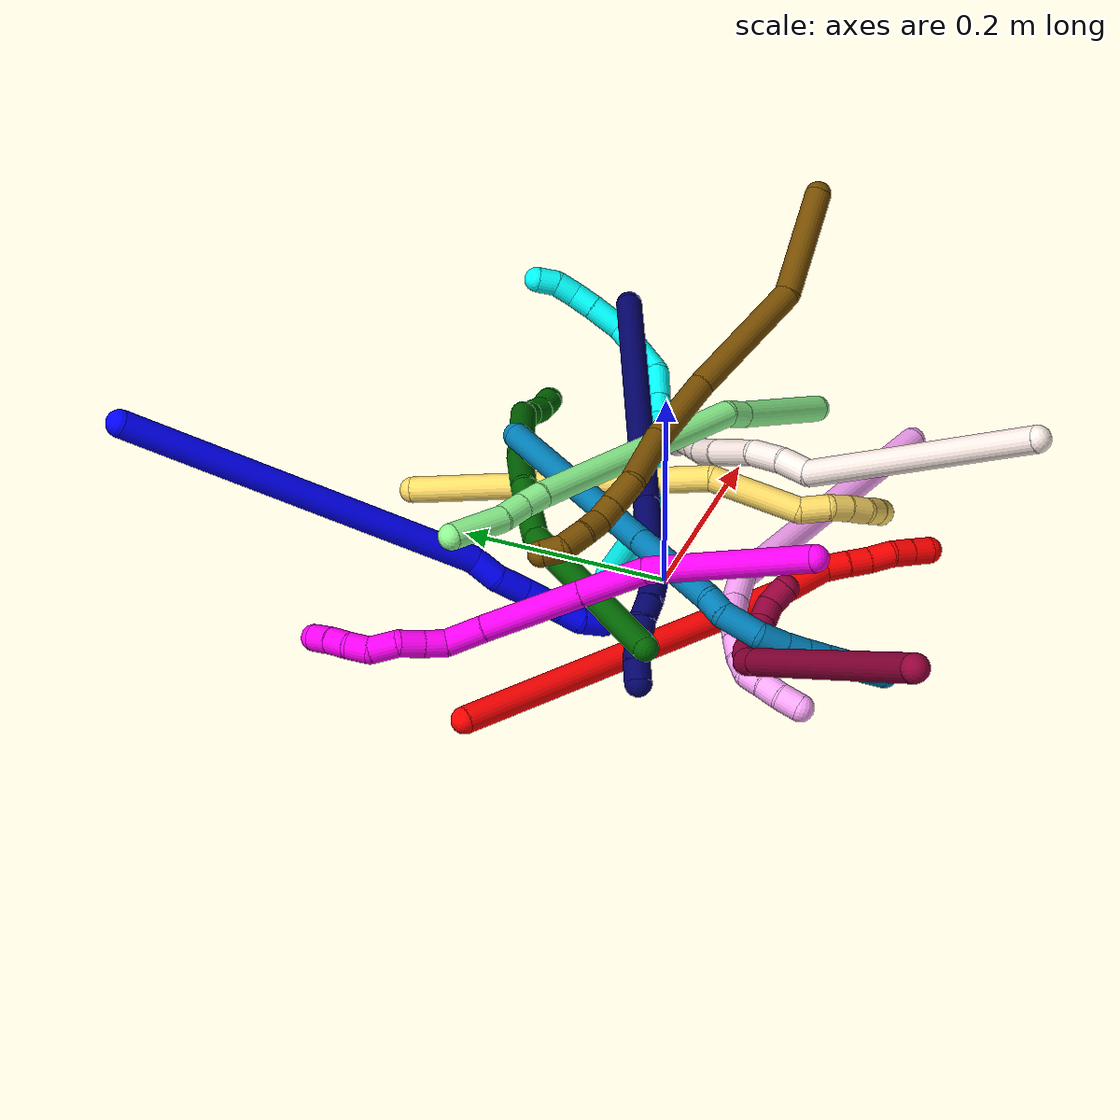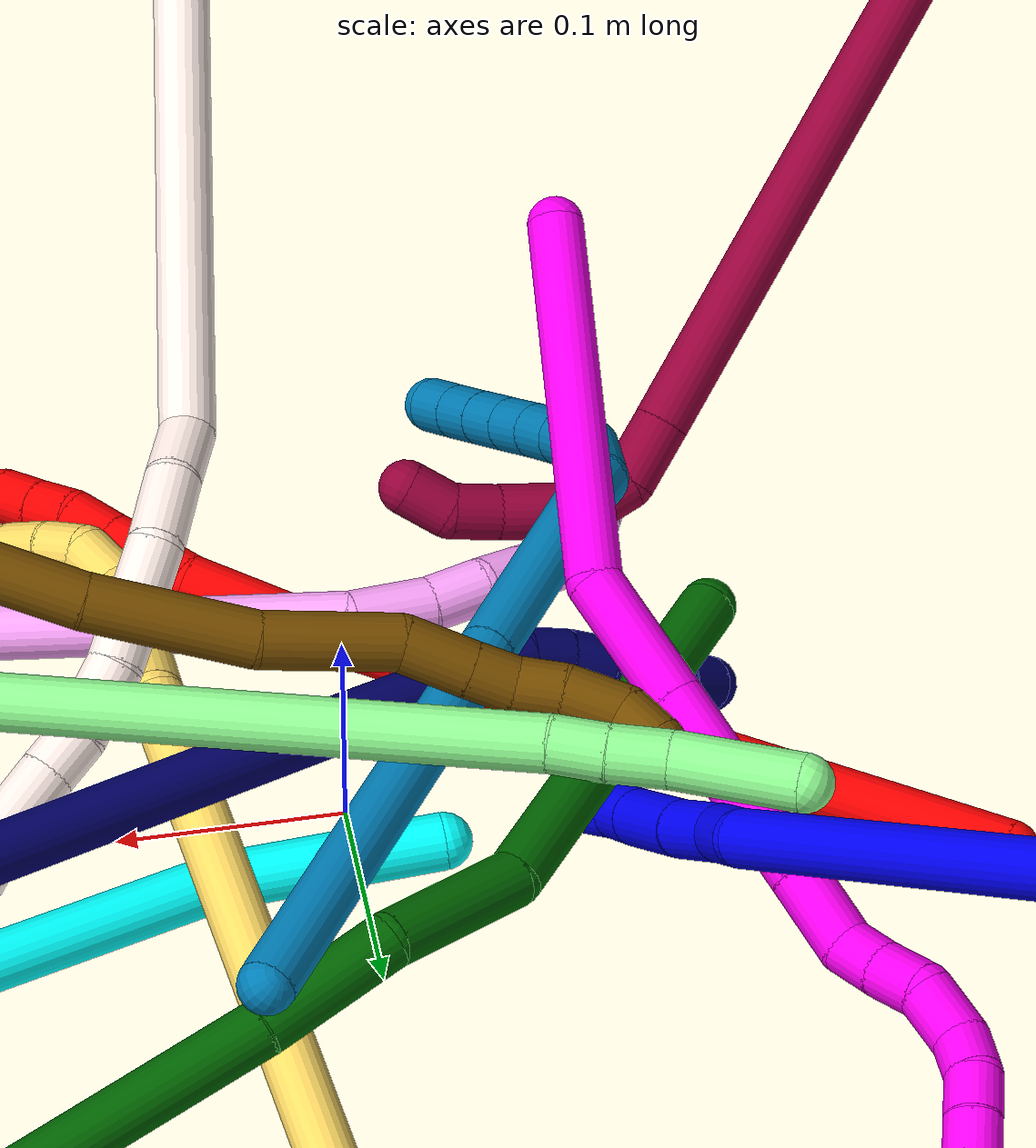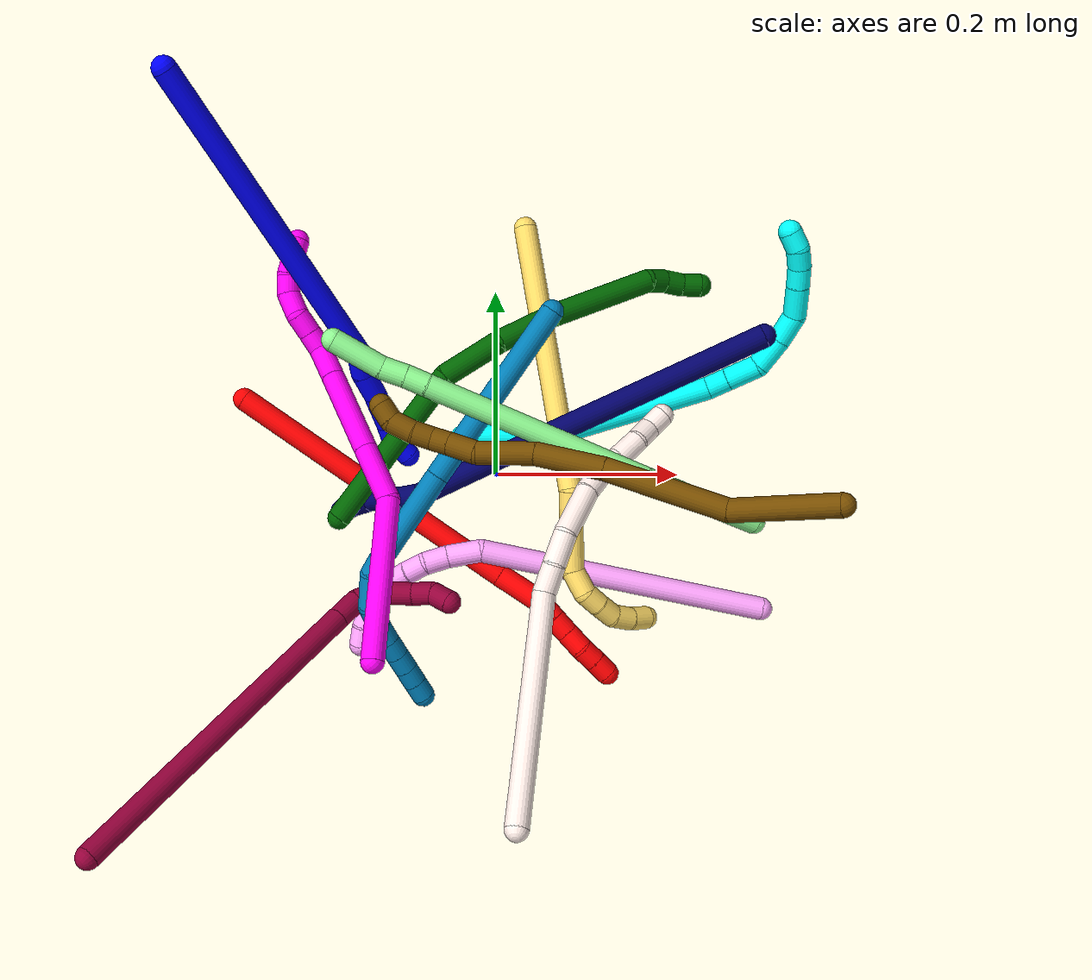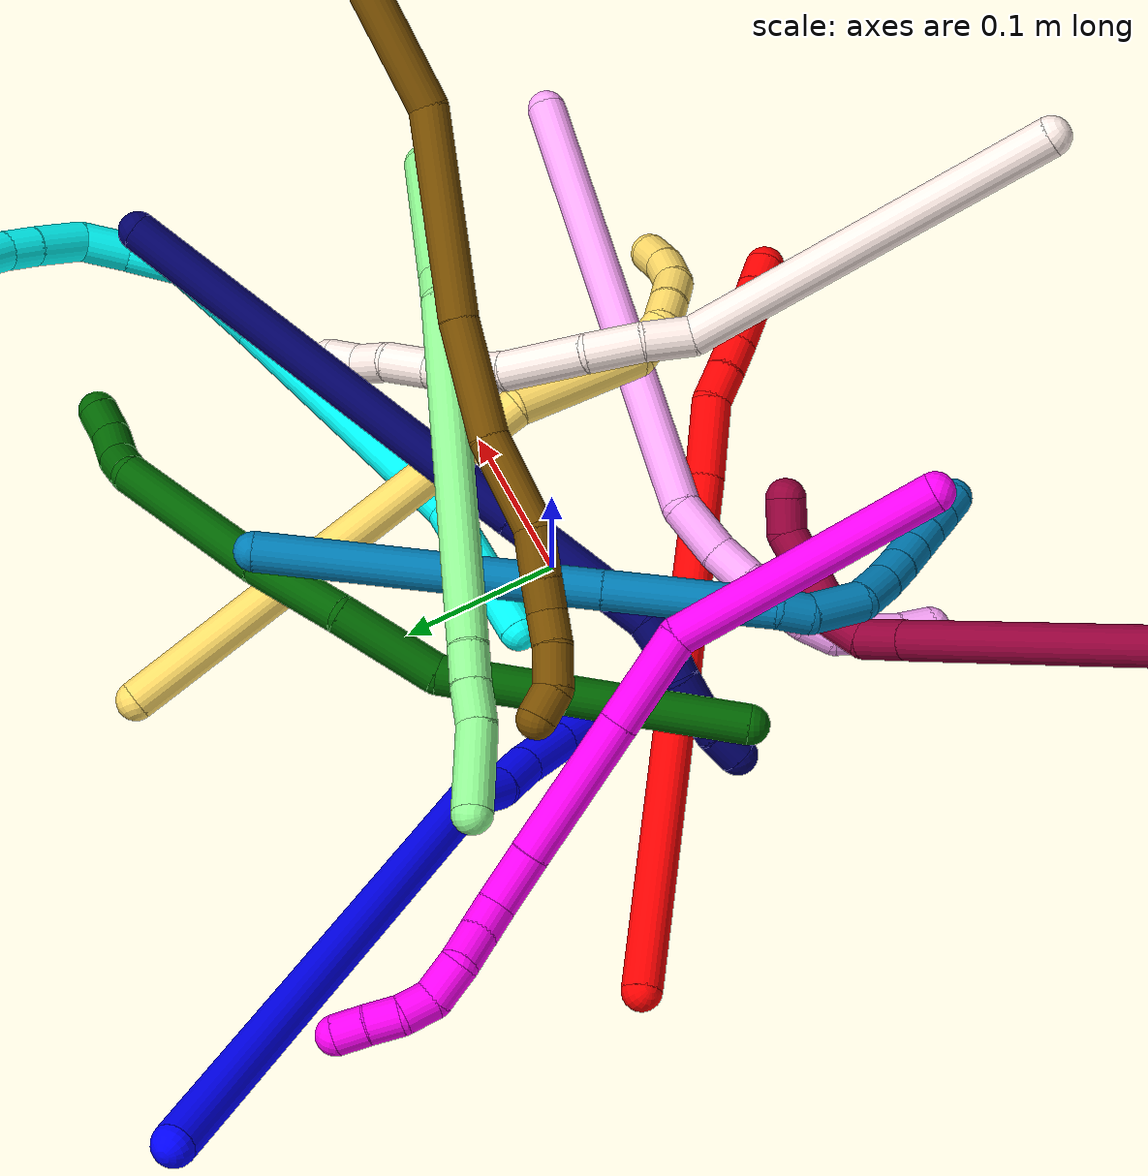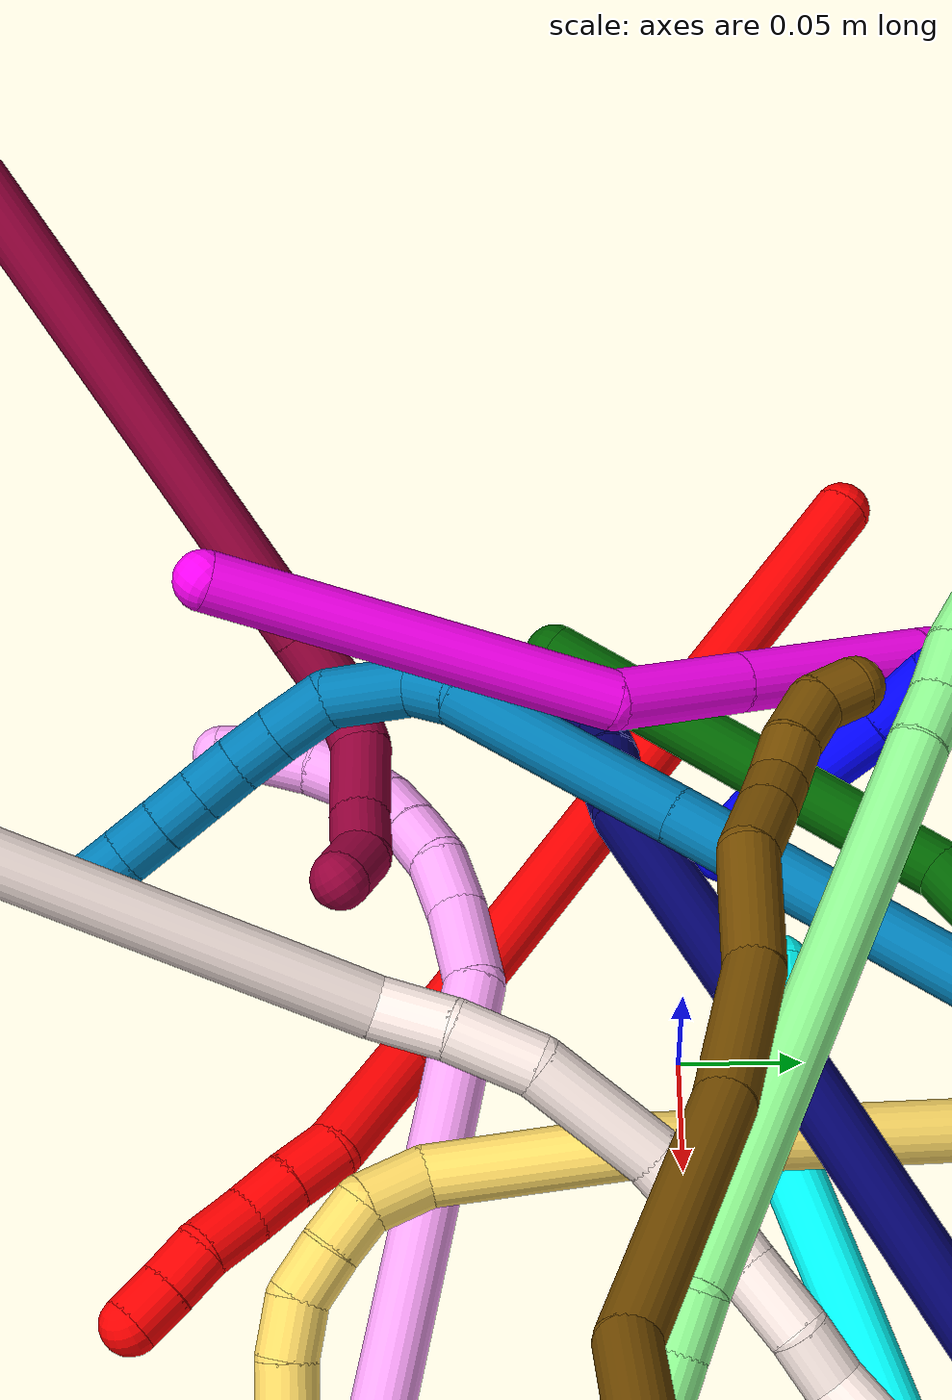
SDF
<sdf version="1.7">
 <world name="default">
  <plugin name="TubeGeneratorPlugin" filename="libtube_generator_plugin.so"/>
  <model name="photoneo_s_sensor">
   <static>1</static>
   <pose>0 0 2 1.57079 1.57079 3.14159</pose>
   <link name="link">
    <inertial><mass>0.1</mass></inertial>
    <sensor name="sensor" type="depth">
     <update_rate>30</update_rate>
     <camera>
      <horizontal_fov>1.22</horizontal_fov>
      <image><width>1920</width><height>1200</height><format>B8G8R8</format></image>
      <clip><near>0.1</near><far>4</far></clip>
      <depth_camera><output>points</output></depth_camera>
     </camera>
     <plugin name="camera_plugin" filename="libgazebo_ros_depth_camera.so">
      <baseline>0.2</baseline>
      <alwaysOn>1</alwaysOn>
      <updateRate>0.0</updateRate>
      <cameraName>camera_ir</cameraName>
      <imageTopicName>/camera/color/image_raw</imageTopicName>
      <cameraInfoTopicName>/camera/color/camera_info</cameraInfoTopicName>
      <depthImageTopicName>/camera/depth/image_raw</depthImageTopicName>
      <depthImageCameraInfoTopicName>/camera/depth/camera_info</depthImageCameraInfoTopicName>
      <pointCloudTopicName>/camera/depth/points</pointCloudTopicName>
      <frameName>fr_optical</frameName>
      <pointCloudCutoff>0.1</pointCloudCutoff>
      <pointCloudCutoffMax>2.0</pointCloudCutoffMax>
      <distortionK1>0</distortionK1>
      <distortionK2>0</distortionK2>
      <distortionK3>0</distortionK3>
      <distortionT1>0</distortionT1>
      <distortionT2>0</distortionT2>
      <CxPrime>0</CxPrime>
      <Cx>0</Cx>
      <Cy>0</Cy>
      <focalLength>0</focalLength>
      <hackBaseline>0</hackBaseline>
     </plugin>
    </sensor>
   </link>
  </model>
  <gravity>0 0 -9.8</gravity>
  <magnetic_field>6e-06 2.3e-05 -4.2e-05</magnetic_field>
  <atmosphere type="adiabatic"/>
  <physics name="default_physics" default="0" type="ode">
   <max_step_size>0.003</max_step_size>
   <real_time_factor>1</real_time_factor>
   <real_time_update_rate>1000</real_time_update_rate>
   <max_contacts>10000</max_contacts>
   <ode>
    <solver>
     <type>quick</type>
     <iters>100</iters>
     <sor>1.3</sor>
     <use_dynamic_moi_rescaling>0</use_dynamic_moi_rescaling>
    </solver>
    <constraints>
     <contact_max_correcting_vel>0</contact_max_correcting_vel>
     <contact_surface_layer>0.001</contact_surface_layer>
     <cfm>0</cfm>
     <erp>0.2</erp>
    </constraints>
   </ode>
  </physics>
  <scene><ambient>0.4 0.4 0.4 1</ambient><background>0.7 0.7 0.7 1</background><shadows>0</shadows></scene>
  <audio><device>default</device></audio>
  <spherical_coordinates>
   <surface_model>EARTH_WGS84</surface_model>
   <latitude_deg>0</latitude_deg>
   <longitude_deg>0</longitude_deg>
   <elevation>0</elevation>
   <heading_deg>0</heading_deg>
  </spherical_coordinates>
  <model name="bin">
   <static>1</static>
   <link name="bottom">
    <collision name="collision-bottom">
     <pose>0 0 -0.01 0 -0 0</pose>
     <geometry><box><size>0.8 0.6 0.02</size></box></geometry>
     <surface>
      <friction><ode><mu>100</mu><mu2>100</mu2></ode></friction>
      <contact><collide_bitmask>65535</collide_bitmask></contact>
     </surface>
    </collision>
   </link>
   <link name="west_wall">
    <collision name="collision-west_wall">
     <pose>-0.41 0 0.1 0 -0 0</pose>
     <geometry><box><size>0.02 0.6 0.2</size></box></geometry>
     <surface>
      <friction><ode><mu>100</mu><mu2>100</mu2></ode></friction>
      <contact><collide_bitmask>65535</collide_bitmask></contact>
     </surface>
    </collision>
   </link>
   <link name="east_wall">
    <collision name="collision-east_wall">
     <pose>0.41 0 0.1 0 -0 0</pose>
     <geometry><box><size>0.02 0.6 0.2</size></box></geometry>
     <surface>
      <friction><ode><mu>100</mu><mu2>100</mu2></ode></friction>
      <contact><collide_bitmask>65535</collide_bitmask></contact>
     </surface>
    </collision>
   </link>
   <link name="south_wall">
    <collision name="collision-south_wall">
     <pose>0 -0.31 0.1 0 -0 0</pose>
     <geometry><box><size>0.8 0.02 0.2</size></box></geometry>
     <surface>
      <friction><ode><mu>100</mu><mu2>100</mu2></ode></friction>
      <contact><collide_bitmask>65535</collide_bitmask></contact>
     </surface>
    </collision>
   </link>
   <link name="north_wall">
    <collision name="collision-north_wall">
     <pose>0 0.31 0.1 0 -0 0</pose>
     <geometry><box><size>0.8 0.02 0.2</size></box></geometry>
     <surface>
      <friction><ode><mu>100</mu><mu2>100</mu2></ode></friction>
      <contact><collide_bitmask>65535</collide_bitmask></contact>
     </surface>
    </collision>
   </link>
  </model>
  <model name="1">
   <static>0</static>
   <link name="1">
    <collision name="collision-cylinder-e_1_1_4">
     <pose>-0.004596 0.001135 -0.178871 -3.13525 -0.025689 2.65742</pose>
     <geometry><cylinder><radius>0.0125</radius><length>0.357866</length></cylinder></geometry>
     <surface>
      <friction><ode><mu>1.16</mu><mu2>1.16</mu2><slip1>0</slip1><slip2>0</slip2></ode></friction>
      <contact><ode><kp>1e+06</kp><kd>1</kd><max_vel>0</max_vel><min_depth>0.001</min_depth></ode></contact>
     </surface>
    </collision>
    <visual name="visual-cylinder-e_1_1_4">
     <pose>-0.004596 0.001135 -0.178871 -3.13525 -0.025689 2.65742</pose>
     <geometry><cylinder><radius>0.0125</radius><length>0.357866</length></cylinder></geometry>
     <material><ambient>0 0 1 1</ambient></material>
    </visual>
    <collision name="collision-cylinder-e_2_4_5">
     <pose>-0.009905 -0.002566 -0.370569 2.78115 -0.051922 -0.28313</pose>
     <geometry><cylinder><radius>0.0125</radius><length>0.027456</length></cylinder></geometry>
     <surface>
      <friction><ode><mu>1.16</mu><mu2>1.16</mu2><slip1>0</slip1><slip2>0</slip2></ode></friction>
      <contact><ode><kp>1e+06</kp><kd>1</kd><max_vel>0</max_vel><min_depth>0.001</min_depth></ode></contact>
     </surface>
    </collision>
    <visual name="visual-cylinder-e_2_4_5">
     <pose>-0.009905 -0.002566 -0.370569 2.78115 -0.051922 -0.28313</pose>
     <geometry><cylinder><radius>0.0125</radius><length>0.027456</length></cylinder></geometry>
     <material><ambient>0 0 1 1</ambient></material>
    </visual>
    <collision name="collision-cylinder-e_3_5_6">
     <pose>-0.011227 -0.008489 -0.398178 3.06813 -0.0411 -1.01994</pose>
     <geometry><cylinder><radius>0.0125</radius><length>0.029665</length></cylinder></geometry>
     <surface>
      <friction><ode><mu>1.16</mu><mu2>1.16</mu2><slip1>0</slip1><slip2>0</slip2></ode></friction>
      <contact><ode><kp>1e+06</kp><kd>1</kd><max_vel>0</max_vel><min_depth>0.001</min_depth></ode></contact>
     </surface>
    </collision>
    <visual name="visual-cylinder-e_3_5_6">
     <pose>-0.011227 -0.008489 -0.398178 3.06813 -0.0411 -1.01994</pose>
     <geometry><cylinder><radius>0.0125</radius><length>0.029665</length></cylinder></geometry>
     <material><ambient>0 0 1 1</ambient></material>
    </visual>
    <collision name="collision-cylinder-e_4_6_7">
     <pose>-0.011521 -0.012771 -0.432223 2.97729 0.016114 0.195092</pose>
     <geometry><cylinder><radius>0.0125</radius><length>0.039061</length></cylinder></geometry>
     <surface>
      <friction><ode><mu>1.16</mu><mu2>1.16</mu2><slip1>0</slip1><slip2>0</slip2></ode></friction>
      <contact><ode><kp>1e+06</kp><kd>1</kd><max_vel>0</max_vel><min_depth>0.001</min_depth></ode></contact>
     </surface>
    </collision>
    <visual name="visual-cylinder-e_4_6_7">
     <pose>-0.011521 -0.012771 -0.432223 2.97729 0.016114 0.195092</pose>
     <geometry><cylinder><radius>0.0125</radius><length>0.039061</length></cylinder></geometry>
     <material><ambient>0 0 1 1</ambient></material>
    </visual>
    <collision name="collision-cylinder-e_5_7_8">
     <pose>-0.010749 -0.018068 -0.461751 2.93947 0.043622 0.423792</pose>
     <geometry><cylinder><radius>0.0125</radius><length>0.020972</length></cylinder></geometry>
     <surface>
      <friction><ode><mu>1.16</mu><mu2>1.16</mu2><slip1>0</slip1><slip2>0</slip2></ode></friction>
      <contact><ode><kp>1e+06</kp><kd>1</kd><max_vel>0</max_vel><min_depth>0.001</min_depth></ode></contact>
     </surface>
    </collision>
    <visual name="visual-cylinder-e_5_7_8">
     <pose>-0.010749 -0.018068 -0.461751 2.93947 0.043622 0.423792</pose>
     <geometry><cylinder><radius>0.0125</radius><length>0.020972</length></cylinder></geometry>
     <material><ambient>0 0 1 1</ambient></material>
    </visual>
    <collision name="collision-cylinder-e_6_8_2">
     <pose>-0.009274 -0.017582 -0.48419 -2.9321 0.081609 -0.740845</pose>
     <geometry><cylinder><radius>0.0125</radius><length>0.024979</length></cylinder></geometry>
     <surface>
      <friction><ode><mu>1.16</mu><mu2>1.16</mu2><slip1>0</slip1><slip2>0</slip2></ode></friction>
      <contact><ode><kp>1e+06</kp><kd>1</kd><max_vel>0</max_vel><min_depth>0.001</min_depth></ode></contact>
     </surface>
    </collision>
    <visual name="visual-cylinder-e_6_8_2">
     <pose>-0.009274 -0.017582 -0.48419 -2.9321 0.081609 -0.740845</pose>
     <geometry><cylinder><radius>0.0125</radius><length>0.024979</length></cylinder></geometry>
     <material><ambient>0 0 1 1</ambient></material>
    </visual>
    <collision name="collision-sphere-2">
     <pose>-0.008256 -0.014993 -0.496366 0 -0 0</pose>
     <geometry><sphere><radius>0.0125</radius></sphere></geometry>
     <surface>
      <friction><ode><mu>1.16</mu><mu2>1.16</mu2><slip1>0</slip1><slip2>0</slip2></ode></friction>
      <contact><ode><kp>1e+06</kp><kd>1</kd><max_vel>0</max_vel><min_depth>0.001</min_depth></ode></contact>
     </surface>
    </collision>
    <visual name="visual-sphere-2">
     <pose>-0.008256 -0.014993 -0.496366 0 -0 0</pose>
     <geometry><sphere><radius>0.0125</radius></sphere></geometry>
     <material><ambient>0 0 1 1</ambient></material>
    </visual>
    <collision name="collision-sphere-4">
     <pose>-0.009192 0.002269 -0.357741 0 -0 0</pose>
     <geometry><sphere><radius>0.0125</radius></sphere></geometry>
     <surface>
      <friction><ode><mu>1.16</mu><mu2>1.16</mu2><slip1>0</slip1><slip2>0</slip2></ode></friction>
      <contact><ode><kp>1e+06</kp><kd>1</kd><max_vel>0</max_vel><min_depth>0.001</min_depth></ode></contact>
     </surface>
    </collision>
    <visual name="visual-sphere-4">
     <pose>-0.009192 0.002269 -0.357741 0 -0 0</pose>
     <geometry><sphere><radius>0.0125</radius></sphere></geometry>
     <material><ambient>0 0 1 1</ambient></material>
    </visual>
    <collision name="collision-sphere-1">
     <geometry><sphere><radius>0.0125</radius></sphere></geometry>
     <surface>
      <friction><ode><mu>1.16</mu><mu2>1.16</mu2><slip1>0</slip1><slip2>0</slip2></ode></friction>
      <contact><ode><kp>1e+06</kp><kd>1</kd><max_vel>0</max_vel><min_depth>0.001</min_depth></ode></contact>
     </surface>
    </collision>
    <visual name="visual-sphere-1">
     <geometry><sphere><radius>0.0125</radius></sphere></geometry>
     <material><ambient>0 0 1 1</ambient></material>
    </visual>
    <collision name="collision-sphere-8">
     <pose>-0.010292 -0.020171 -0.472014 0 -0 0</pose>
     <geometry><sphere><radius>0.0125</radius></sphere></geometry>
     <surface>
      <friction><ode><mu>1.16</mu><mu2>1.16</mu2><slip1>0</slip1><slip2>0</slip2></ode></friction>
      <contact><ode><kp>1e+06</kp><kd>1</kd><max_vel>0</max_vel><min_depth>0.001</min_depth></ode></contact>
     </surface>
    </collision>
    <visual name="visual-sphere-8">
     <pose>-0.010292 -0.020171 -0.472014 0 -0 0</pose>
     <geometry><sphere><radius>0.0125</radius></sphere></geometry>
     <material><ambient>0 0 1 1</ambient></material>
    </visual>
    <collision name="collision-sphere-5">
     <pose>-0.010617 -0.007401 -0.383398 0 -0 0</pose>
     <geometry><sphere><radius>0.0125</radius></sphere></geometry>
     <surface>
      <friction><ode><mu>1.16</mu><mu2>1.16</mu2><slip1>0</slip1><slip2>0</slip2></ode></friction>
      <contact><ode><kp>1e+06</kp><kd>1</kd><max_vel>0</max_vel><min_depth>0.001</min_depth></ode></contact>
     </surface>
    </collision>
    <visual name="visual-sphere-5">
     <pose>-0.010617 -0.007401 -0.383398 0 -0 0</pose>
     <geometry><sphere><radius>0.0125</radius></sphere></geometry>
     <material><ambient>0 0 1 1</ambient></material>
    </visual>
    <collision name="collision-sphere-6">
     <pose>-0.011836 -0.009576 -0.412958 0 -0 0</pose>
     <geometry><sphere><radius>0.0125</radius></sphere></geometry>
     <surface>
      <friction><ode><mu>1.16</mu><mu2>1.16</mu2><slip1>0</slip1><slip2>0</slip2></ode></friction>
      <contact><ode><kp>1e+06</kp><kd>1</kd><max_vel>0</max_vel><min_depth>0.001</min_depth></ode></contact>
     </surface>
    </collision>
    <visual name="visual-sphere-6">
     <pose>-0.011836 -0.009576 -0.412958 0 -0 0</pose>
     <geometry><sphere><radius>0.0125</radius></sphere></geometry>
     <material><ambient>0 0 1 1</ambient></material>
    </visual>
    <collision name="collision-sphere-7">
     <pose>-0.011207 -0.015965 -0.451489 0 -0 0</pose>
     <geometry><sphere><radius>0.0125</radius></sphere></geometry>
     <surface>
      <friction><ode><mu>1.16</mu><mu2>1.16</mu2><slip1>0</slip1><slip2>0</slip2></ode></friction>
      <contact><ode><kp>1e+06</kp><kd>1</kd><max_vel>0</max_vel><min_depth>0.001</min_depth></ode></contact>
     </surface>
    </collision>
    <visual name="visual-sphere-7">
     <pose>-0.011207 -0.015965 -0.451489 0 -0 0</pose>
     <geometry><sphere><radius>0.0125</radius></sphere></geometry>
     <material><ambient>0 0 1 1</ambient></material>
    </visual>
    <inertial>
     <pose>-0.006314 -0.002466 -0.24932 0 -0 0</pose>
     <mass>0.5</mass>
     <inertia>
      <ixx>-0.001598</ixx>
      <ixy>0</ixy>
      <ixz>0</ixz>
      <iyy>0.005159</iyy>
      <iyz>0</iyz>
      <izz>3.7e-05</izz>
     </inertia>
    </inertial>
   </link>
   <pose>-0.314417 0.381434 0.274968 0.559325 -0.928527 -1.66233</pose>
  </model>
  <model name="2">
   <static>0</static>
   <link name="2">
    <collision name="collision-cylinder-e_1_1_4">
     <pose>0.137493 -0.098768 -0.004996 1.62133 0.947257 0.988901</pose>
     <geometry><cylinder><radius>0.0125</radius><length>0.338729</length></cylinder></geometry>
     <surface>
      <friction><ode><mu>1.16</mu><mu2>1.16</mu2><slip1>0</slip1><slip2>0</slip2></ode></friction>
      <contact><ode><kp>1e+06</kp><kd>1</kd><max_vel>0</max_vel><min_depth>0.001</min_depth></ode></contact>
     </surface>
    </collision>
    <visual name="visual-cylinder-e_1_1_4">
     <pose>0.137493 -0.098768 -0.004996 1.62133 0.947257 0.988901</pose>
     <geometry><cylinder><radius>0.0125</radius><length>0.338729</length></cylinder></geometry>
     <material><ambient>1 0 0 1</ambient></material>
    </visual>
    <collision name="collision-cylinder-e_2_4_5">
     <pose>0.297599 -0.21104 -0.008042 1.42745 1.02789 0.90948</pose>
     <geometry><cylinder><radius>0.0125</radius><length>0.05282</length></cylinder></geometry>
     <surface>
      <friction><ode><mu>1.16</mu><mu2>1.16</mu2><slip1>0</slip1><slip2>0</slip2></ode></friction>
      <contact><ode><kp>1e+06</kp><kd>1</kd><max_vel>0</max_vel><min_depth>0.001</min_depth></ode></contact>
     </surface>
    </collision>
    <visual name="visual-cylinder-e_2_4_5">
     <pose>0.297599 -0.21104 -0.008042 1.42745 1.02789 0.90948</pose>
     <geometry><cylinder><radius>0.0125</radius><length>0.05282</length></cylinder></geometry>
     <material><ambient>1 0 0 1</ambient></material>
    </visual>
    <collision name="collision-cylinder-e_3_5_6">
     <pose>0.327749 -0.233285 -0.004858 1.43046 0.706718 0.620126</pose>
     <geometry><cylinder><radius>0.0125</radius><length>0.023216</length></cylinder></geometry>
     <surface>
      <friction><ode><mu>1.16</mu><mu2>1.16</mu2><slip1>0</slip1><slip2>0</slip2></ode></friction>
      <contact><ode><kp>1e+06</kp><kd>1</kd><max_vel>0</max_vel><min_depth>0.001</min_depth></ode></contact>
     </surface>
    </collision>
    <visual name="visual-cylinder-e_3_5_6">
     <pose>0.327749 -0.233285 -0.004858 1.43046 0.706718 0.620126</pose>
     <geometry><cylinder><radius>0.0125</radius><length>0.023216</length></cylinder></geometry>
     <material><ambient>1 0 0 1</ambient></material>
    </visual>
    <collision name="collision-cylinder-e_4_6_7">
     <pose>0.342283 -0.250117 -0.003264 1.52644 0.712513 0.683994</pose>
     <geometry><cylinder><radius>0.0125</radius><length>0.021406</length></cylinder></geometry>
     <surface>
      <friction><ode><mu>1.16</mu><mu2>1.16</mu2><slip1>0</slip1><slip2>0</slip2></ode></friction>
      <contact><ode><kp>1e+06</kp><kd>1</kd><max_vel>0</max_vel><min_depth>0.001</min_depth></ode></contact>
     </surface>
    </collision>
    <visual name="visual-cylinder-e_4_6_7">
     <pose>0.342283 -0.250117 -0.003264 1.52644 0.712513 0.683994</pose>
     <geometry><cylinder><radius>0.0125</radius><length>0.021406</length></cylinder></geometry>
     <material><ambient>1 0 0 1</ambient></material>
    </visual>
    <collision name="collision-cylinder-e_5_7_8">
     <pose>0.357503 -0.266652 -0.001438 1.39878 0.764711 0.652435</pose>
     <geometry><cylinder><radius>0.0125</radius><length>0.023755</length></cylinder></geometry>
     <surface>
      <friction><ode><mu>1.16</mu><mu2>1.16</mu2><slip1>0</slip1><slip2>0</slip2></ode></friction>
      <contact><ode><kp>1e+06</kp><kd>1</kd><max_vel>0</max_vel><min_depth>0.001</min_depth></ode></contact>
     </surface>
    </collision>
    <visual name="visual-cylinder-e_5_7_8">
     <pose>0.357503 -0.266652 -0.001438 1.39878 0.764711 0.652435</pose>
     <geometry><cylinder><radius>0.0125</radius><length>0.023755</length></cylinder></geometry>
     <material><ambient>1 0 0 1</ambient></material>
    </visual>
    <collision name="collision-cylinder-e_6_8_9">
     <pose>0.372372 -0.28247 -0.001247 1.74215 0.726235 0.847982</pose>
     <geometry><cylinder><radius>0.0125</radius><length>0.020017</length></cylinder></geometry>
     <surface>
      <friction><ode><mu>1.16</mu><mu2>1.16</mu2><slip1>0</slip1><slip2>0</slip2></ode></friction>
      <contact><ode><kp>1e+06</kp><kd>1</kd><max_vel>0</max_vel><min_depth>0.001</min_depth></ode></contact>
     </surface>
    </collision>
    <visual name="visual-cylinder-e_6_8_9">
     <pose>0.372372 -0.28247 -0.001247 1.74215 0.726235 0.847982</pose>
     <geometry><cylinder><radius>0.0125</radius><length>0.020017</length></cylinder></geometry>
     <material><ambient>1 0 0 1</ambient></material>
    </visual>
    <collision name="collision-cylinder-e_7_9_2">
     <pose>0.385453 -0.297471 -0.003517 1.70039 0.696657 0.784232</pose>
     <geometry><cylinder><radius>0.0125</radius><length>0.020058</length></cylinder></geometry>
     <surface>
      <friction><ode><mu>1.16</mu><mu2>1.16</mu2><slip1>0</slip1><slip2>0</slip2></ode></friction>
      <contact><ode><kp>1e+06</kp><kd>1</kd><max_vel>0</max_vel><min_depth>0.001</min_depth></ode></contact>
     </surface>
    </collision>
    <visual name="visual-cylinder-e_7_9_2">
     <pose>0.385453 -0.297471 -0.003517 1.70039 0.696657 0.784232</pose>
     <geometry><cylinder><radius>0.0125</radius><length>0.020058</length></cylinder></geometry>
     <material><ambient>1 0 0 1</ambient></material>
    </visual>
    <collision name="collision-sphere-2">
     <pose>0.391888 -0.305098 -0.004511 0 -0 0</pose>
     <geometry><sphere><radius>0.0125</radius></sphere></geometry>
     <surface>
      <friction><ode><mu>1.16</mu><mu2>1.16</mu2><slip1>0</slip1><slip2>0</slip2></ode></friction>
      <contact><ode><kp>1e+06</kp><kd>1</kd><max_vel>0</max_vel><min_depth>0.001</min_depth></ode></contact>
     </surface>
    </collision>
    <visual name="visual-sphere-2">
     <pose>0.391888 -0.305098 -0.004511 0 -0 0</pose>
     <geometry><sphere><radius>0.0125</radius></sphere></geometry>
     <material><ambient>1 0 0 1</ambient></material>
    </visual>
    <collision name="collision-sphere-9">
     <pose>0.379018 -0.289843 -0.002523 0 -0 0</pose>
     <geometry><sphere><radius>0.0125</radius></sphere></geometry>
     <surface>
      <friction><ode><mu>1.16</mu><mu2>1.16</mu2><slip1>0</slip1><slip2>0</slip2></ode></friction>
      <contact><ode><kp>1e+06</kp><kd>1</kd><max_vel>0</max_vel><min_depth>0.001</min_depth></ode></contact>
     </surface>
    </collision>
    <visual name="visual-sphere-9">
     <pose>0.379018 -0.289843 -0.002523 0 -0 0</pose>
     <geometry><sphere><radius>0.0125</radius></sphere></geometry>
     <material><ambient>1 0 0 1</ambient></material>
    </visual>
    <collision name="collision-sphere-4">
     <pose>0.274986 -0.197536 -0.009991 0 -0 0</pose>
     <geometry><sphere><radius>0.0125</radius></sphere></geometry>
     <surface>
      <friction><ode><mu>1.16</mu><mu2>1.16</mu2><slip1>0</slip1><slip2>0</slip2></ode></friction>
      <contact><ode><kp>1e+06</kp><kd>1</kd><max_vel>0</max_vel><min_depth>0.001</min_depth></ode></contact>
     </surface>
    </collision>
    <visual name="visual-sphere-4">
     <pose>0.274986 -0.197536 -0.009991 0 -0 0</pose>
     <geometry><sphere><radius>0.0125</radius></sphere></geometry>
     <material><ambient>1 0 0 1</ambient></material>
    </visual>
    <collision name="collision-sphere-1">
     <geometry><sphere><radius>0.0125</radius></sphere></geometry>
     <surface>
      <friction><ode><mu>1.16</mu><mu2>1.16</mu2><slip1>0</slip1><slip2>0</slip2></ode></friction>
      <contact><ode><kp>1e+06</kp><kd>1</kd><max_vel>0</max_vel><min_depth>0.001</min_depth></ode></contact>
     </surface>
    </collision>
    <visual name="visual-sphere-1">
     <geometry><sphere><radius>0.0125</radius></sphere></geometry>
     <material><ambient>1 0 0 1</ambient></material>
    </visual>
    <collision name="collision-sphere-8">
     <pose>0.365726 -0.275096 2.9e-05 0 -0 0</pose>
     <geometry><sphere><radius>0.0125</radius></sphere></geometry>
     <surface>
      <friction><ode><mu>1.16</mu><mu2>1.16</mu2><slip1>0</slip1><slip2>0</slip2></ode></friction>
      <contact><ode><kp>1e+06</kp><kd>1</kd><max_vel>0</max_vel><min_depth>0.001</min_depth></ode></contact>
     </surface>
    </collision>
    <visual name="visual-sphere-8">
     <pose>0.365726 -0.275096 2.9e-05 0 -0 0</pose>
     <geometry><sphere><radius>0.0125</radius></sphere></geometry>
     <material><ambient>1 0 0 1</ambient></material>
    </visual>
    <collision name="collision-sphere-5">
     <pose>0.320211 -0.224544 -0.006093 0 -0 0</pose>
     <geometry><sphere><radius>0.0125</radius></sphere></geometry>
     <surface>
      <friction><ode><mu>1.16</mu><mu2>1.16</mu2><slip1>0</slip1><slip2>0</slip2></ode></friction>
      <contact><ode><kp>1e+06</kp><kd>1</kd><max_vel>0</max_vel><min_depth>0.001</min_depth></ode></contact>
     </surface>
    </collision>
    <visual name="visual-sphere-5">
     <pose>0.320211 -0.224544 -0.006093 0 -0 0</pose>
     <geometry><sphere><radius>0.0125</radius></sphere></geometry>
     <material><ambient>1 0 0 1</ambient></material>
    </visual>
    <collision name="collision-sphere-6">
     <pose>0.335286 -0.242026 -0.003624 0 -0 0</pose>
     <geometry><sphere><radius>0.0125</radius></sphere></geometry>
     <surface>
      <friction><ode><mu>1.16</mu><mu2>1.16</mu2><slip1>0</slip1><slip2>0</slip2></ode></friction>
      <contact><ode><kp>1e+06</kp><kd>1</kd><max_vel>0</max_vel><min_depth>0.001</min_depth></ode></contact>
     </surface>
    </collision>
    <visual name="visual-sphere-6">
     <pose>0.335286 -0.242026 -0.003624 0 -0 0</pose>
     <geometry><sphere><radius>0.0125</radius></sphere></geometry>
     <material><ambient>1 0 0 1</ambient></material>
    </visual>
    <collision name="collision-sphere-7">
     <pose>0.34928 -0.258208 -0.002905 0 -0 0</pose>
     <geometry><sphere><radius>0.0125</radius></sphere></geometry>
     <surface>
      <friction><ode><mu>1.16</mu><mu2>1.16</mu2><slip1>0</slip1><slip2>0</slip2></ode></friction>
      <contact><ode><kp>1e+06</kp><kd>1</kd><max_vel>0</max_vel><min_depth>0.001</min_depth></ode></contact>
     </surface>
    </collision>
    <visual name="visual-sphere-7">
     <pose>0.34928 -0.258208 -0.002905 0 -0 0</pose>
     <geometry><sphere><radius>0.0125</radius></sphere></geometry>
     <material><ambient>1 0 0 1</ambient></material>
    </visual>
    <inertial>
     <pose>0.201811 -0.146655 -0.004859 0 -0 0</pose>
     <mass>0.5</mass>
     <inertia><ixx>0.00268</ixx><ixy>0</ixy><ixz>0</ixz><iyy>0.0037</iyy><iyz>0</iyz><izz>-0.000748</izz></inertia>
    </inertial>
   </link>
   <pose>-0.274436 0.082087 0.011499 0.383127 -0.293484 -0.043976</pose>
  </model>
  <model name="3">
   <static>0</static>
   <link name="3">
    <collision name="collision-cylinder-e_1_1_4">
     <pose>0.003301 0.005956 0.048048 -0.12334 0.068072 -0.004205</pose>
     <geometry><cylinder><radius>0.0125</radius><length>0.097057</length></cylinder></geometry>
     <surface>
      <friction><ode><mu>1.16</mu><mu2>1.16</mu2><slip1>0</slip1><slip2>0</slip2></ode></friction>
      <contact><ode><kp>1e+06</kp><kd>1</kd><max_vel>0</max_vel><min_depth>0.001</min_depth></ode></contact>
     </surface>
    </collision>
    <visual name="visual-cylinder-e_1_1_4">
     <pose>0.003301 0.005956 0.048048 -0.12334 0.068072 -0.004205</pose>
     <geometry><cylinder><radius>0.0125</radius><length>0.097057</length></cylinder></geometry>
     <material><ambient>0.003922 1 0.996078 1</ambient></material>
    </visual>
    <collision name="collision-cylinder-e_2_4_5">
     <pose>0.033647 0.009566 0.181059 0.027616 0.308064 0.004288</pose>
     <geometry><cylinder><radius>0.0125</radius><length>0.178389</length></cylinder></geometry>
     <surface>
      <friction><ode><mu>1.16</mu><mu2>1.16</mu2><slip1>0</slip1><slip2>0</slip2></ode></friction>
      <contact><ode><kp>1e+06</kp><kd>1</kd><max_vel>0</max_vel><min_depth>0.001</min_depth></ode></contact>
     </surface>
    </collision>
    <visual name="visual-cylinder-e_2_4_5">
     <pose>0.033647 0.009566 0.181059 0.027616 0.308064 0.004288</pose>
     <geometry><cylinder><radius>0.0125</radius><length>0.178389</length></cylinder></geometry>
     <material><ambient>0.003922 1 0.996078 1</ambient></material>
    </visual>
    <collision name="collision-cylinder-e_3_5_6">
     <pose>0.067952 0.008804 0.275861 -0.159735 0.629638 -0.052117</pose>
     <geometry><cylinder><radius>0.0125</radius><length>0.02466</length></cylinder></geometry>
     <surface>
      <friction><ode><mu>1.16</mu><mu2>1.16</mu2><slip1>0</slip1><slip2>0</slip2></ode></friction>
      <contact><ode><kp>1e+06</kp><kd>1</kd><max_vel>0</max_vel><min_depth>0.001</min_depth></ode></contact>
     </surface>
    </collision>
    <visual name="visual-cylinder-e_3_5_6">
     <pose>0.067952 0.008804 0.275861 -0.159735 0.629638 -0.052117</pose>
     <geometry><cylinder><radius>0.0125</radius><length>0.02466</length></cylinder></geometry>
     <material><ambient>0.003922 1 0.996078 1</ambient></material>
    </visual>
    <collision name="collision-cylinder-e_4_6_7">
     <pose>0.085364 0.012384 0.299953 -0.139027 0.614271 -0.044159</pose>
     <geometry><cylinder><radius>0.0125</radius><length>0.035223</length></cylinder></geometry>
     <surface>
      <friction><ode><mu>1.16</mu><mu2>1.16</mu2><slip1>0</slip1><slip2>0</slip2></ode></friction>
      <contact><ode><kp>1e+06</kp><kd>1</kd><max_vel>0</max_vel><min_depth>0.001</min_depth></ode></contact>
     </surface>
    </collision>
    <visual name="visual-cylinder-e_4_6_7">
     <pose>0.085364 0.012384 0.299953 -0.139027 0.614271 -0.044159</pose>
     <geometry><cylinder><radius>0.0125</radius><length>0.035223</length></cylinder></geometry>
     <material><ambient>0.003922 1 0.996078 1</ambient></material>
    </visual>
    <collision name="collision-cylinder-e_5_7_8">
     <pose>0.108814 0.009458 0.324703 0.438315 0.853849 0.201957</pose>
     <geometry><cylinder><radius>0.0125</radius><length>0.035287</length></cylinder></geometry>
     <surface>
      <friction><ode><mu>1.16</mu><mu2>1.16</mu2><slip1>0</slip1><slip2>0</slip2></ode></friction>
      <contact><ode><kp>1e+06</kp><kd>1</kd><max_vel>0</max_vel><min_depth>0.001</min_depth></ode></contact>
     </surface>
    </collision>
    <visual name="visual-cylinder-e_5_7_8">
     <pose>0.108814 0.009458 0.324703 0.438315 0.853849 0.201957</pose>
     <geometry><cylinder><radius>0.0125</radius><length>0.035287</length></cylinder></geometry>
     <material><ambient>0.003922 1 0.996078 1</ambient></material>
    </visual>
    <collision name="collision-cylinder-e_6_8_9">
     <pose>0.13602 0.001541 0.341856 0.423115 1.08745 0.258216</pose>
     <geometry><cylinder><radius>0.0125</radius><length>0.031409</length></cylinder></geometry>
     <surface>
      <friction><ode><mu>1.16</mu><mu2>1.16</mu2><slip1>0</slip1><slip2>0</slip2></ode></friction>
      <contact><ode><kp>1e+06</kp><kd>1</kd><max_vel>0</max_vel><min_depth>0.001</min_depth></ode></contact>
     </surface>
    </collision>
    <visual name="visual-cylinder-e_6_8_9">
     <pose>0.13602 0.001541 0.341856 0.423115 1.08745 0.258216</pose>
     <geometry><cylinder><radius>0.0125</radius><length>0.031409</length></cylinder></geometry>
     <material><ambient>0.003922 1 0.996078 1</ambient></material>
    </visual>
    <collision name="collision-cylinder-e_7_9_10">
     <pose>0.166862 -0.005062 0.347535 1.83494 1.3537 1.61922</pose>
     <geometry><cylinder><radius>0.0125</radius><length>0.034687</length></cylinder></geometry>
     <surface>
      <friction><ode><mu>1.16</mu><mu2>1.16</mu2><slip1>0</slip1><slip2>0</slip2></ode></friction>
      <contact><ode><kp>1e+06</kp><kd>1</kd><max_vel>0</max_vel><min_depth>0.001</min_depth></ode></contact>
     </surface>
    </collision>
    <visual name="visual-cylinder-e_7_9_10">
     <pose>0.166862 -0.005062 0.347535 1.83494 1.3537 1.61922</pose>
     <geometry><cylinder><radius>0.0125</radius><length>0.034687</length></cylinder></geometry>
     <material><ambient>0.003922 1 0.996078 1</ambient></material>
    </visual>
    <collision name="collision-cylinder-e_8_10_11">
     <pose>0.194413 -0.01143 0.345846 1.82393 1.30829 1.5611</pose>
     <geometry><cylinder><radius>0.0125</radius><length>0.021983</length></cylinder></geometry>
     <surface>
      <friction><ode><mu>1.16</mu><mu2>1.16</mu2><slip1>0</slip1><slip2>0</slip2></ode></friction>
      <contact><ode><kp>1e+06</kp><kd>1</kd><max_vel>0</max_vel><min_depth>0.001</min_depth></ode></contact>
     </surface>
    </collision>
    <visual name="visual-cylinder-e_8_10_11">
     <pose>0.194413 -0.01143 0.345846 1.82393 1.30829 1.5611</pose>
     <geometry><cylinder><radius>0.0125</radius><length>0.021983</length></cylinder></geometry>
     <material><ambient>0.003922 1 0.996078 1</ambient></material>
    </visual>
    <collision name="collision-cylinder-e_9_11_12">
     <pose>0.215039 -0.016379 0.342605 2.42802 1.24861 2.18667</pose>
     <geometry><cylinder><radius>0.0125</radius><length>0.021108</length></cylinder></geometry>
     <surface>
      <friction><ode><mu>1.16</mu><mu2>1.16</mu2><slip1>0</slip1><slip2>0</slip2></ode></friction>
      <contact><ode><kp>1e+06</kp><kd>1</kd><max_vel>0</max_vel><min_depth>0.001</min_depth></ode></contact>
     </surface>
    </collision>
    <visual name="visual-cylinder-e_9_11_12">
     <pose>0.215039 -0.016379 0.342605 2.42802 1.24861 2.18667</pose>
     <geometry><cylinder><radius>0.0125</radius><length>0.021108</length></cylinder></geometry>
     <material><ambient>0.003922 1 0.996078 1</ambient></material>
    </visual>
    <collision name="collision-cylinder-e_10_12_2">
     <pose>0.232789 -0.023035 0.335376 2.38172 0.87319 1.7259</pose>
     <geometry><cylinder><radius>0.0125</radius><length>0.020198</length></cylinder></geometry>
     <surface>
      <friction><ode><mu>1.16</mu><mu2>1.16</mu2><slip1>0</slip1><slip2>0</slip2></ode></friction>
      <contact><ode><kp>1e+06</kp><kd>1</kd><max_vel>0</max_vel><min_depth>0.001</min_depth></ode></contact>
     </surface>
    </collision>
    <visual name="visual-cylinder-e_10_12_2">
     <pose>0.232789 -0.023035 0.335376 2.38172 0.87319 1.7259</pose>
     <geometry><cylinder><radius>0.0125</radius><length>0.020198</length></cylinder></geometry>
     <material><ambient>0.003922 1 0.996078 1</ambient></material>
    </visual>
    <collision name="collision-sphere-2">
     <pose>0.240528 -0.027503 0.330673 0 -0 0</pose>
     <geometry><sphere><radius>0.0125</radius></sphere></geometry>
     <surface>
      <friction><ode><mu>1.16</mu><mu2>1.16</mu2><slip1>0</slip1><slip2>0</slip2></ode></friction>
      <contact><ode><kp>1e+06</kp><kd>1</kd><max_vel>0</max_vel><min_depth>0.001</min_depth></ode></contact>
     </surface>
    </collision>
    <visual name="visual-sphere-2">
     <pose>0.240528 -0.027503 0.330673 0 -0 0</pose>
     <geometry><sphere><radius>0.0125</radius></sphere></geometry>
     <material><ambient>0.003922 1 0.996078 1</ambient></material>
    </visual>
    <collision name="collision-sphere-12">
     <pose>0.225049 -0.018566 0.340078 0 -0 0</pose>
     <geometry><sphere><radius>0.0125</radius></sphere></geometry>
     <surface>
      <friction><ode><mu>1.16</mu><mu2>1.16</mu2><slip1>0</slip1><slip2>0</slip2></ode></friction>
      <contact><ode><kp>1e+06</kp><kd>1</kd><max_vel>0</max_vel><min_depth>0.001</min_depth></ode></contact>
     </surface>
    </collision>
    <visual name="visual-sphere-12">
     <pose>0.225049 -0.018566 0.340078 0 -0 0</pose>
     <geometry><sphere><radius>0.0125</radius></sphere></geometry>
     <material><ambient>0.003922 1 0.996078 1</ambient></material>
    </visual>
    <collision name="collision-sphere-11">
     <pose>0.205028 -0.014191 0.345131 0 -0 0</pose>
     <geometry><sphere><radius>0.0125</radius></sphere></geometry>
     <surface>
      <friction><ode><mu>1.16</mu><mu2>1.16</mu2><slip1>0</slip1><slip2>0</slip2></ode></friction>
      <contact><ode><kp>1e+06</kp><kd>1</kd><max_vel>0</max_vel><min_depth>0.001</min_depth></ode></contact>
     </surface>
    </collision>
    <visual name="visual-sphere-11">
     <pose>0.205028 -0.014191 0.345131 0 -0 0</pose>
     <geometry><sphere><radius>0.0125</radius></sphere></geometry>
     <material><ambient>0.003922 1 0.996078 1</ambient></material>
    </visual>
    <collision name="collision-sphere-10">
     <pose>0.183798 -0.008668 0.34656 0 -0 0</pose>
     <geometry><sphere><radius>0.0125</radius></sphere></geometry>
     <surface>
      <friction><ode><mu>1.16</mu><mu2>1.16</mu2><slip1>0</slip1><slip2>0</slip2></ode></friction>
      <contact><ode><kp>1e+06</kp><kd>1</kd><max_vel>0</max_vel><min_depth>0.001</min_depth></ode></contact>
     </surface>
    </collision>
    <visual name="visual-sphere-10">
     <pose>0.183798 -0.008668 0.34656 0 -0 0</pose>
     <geometry><sphere><radius>0.0125</radius></sphere></geometry>
     <material><ambient>0.003922 1 0.996078 1</ambient></material>
    </visual>
    <collision name="collision-sphere-9">
     <pose>0.149925 -0.001456 0.348511 0 -0 0</pose>
     <geometry><sphere><radius>0.0125</radius></sphere></geometry>
     <surface>
      <friction><ode><mu>1.16</mu><mu2>1.16</mu2><slip1>0</slip1><slip2>0</slip2></ode></friction>
      <contact><ode><kp>1e+06</kp><kd>1</kd><max_vel>0</max_vel><min_depth>0.001</min_depth></ode></contact>
     </surface>
    </collision>
    <visual name="visual-sphere-9">
     <pose>0.149925 -0.001456 0.348511 0 -0 0</pose>
     <geometry><sphere><radius>0.0125</radius></sphere></geometry>
     <material><ambient>0.003922 1 0.996078 1</ambient></material>
    </visual>
    <collision name="collision-sphere-4">
     <pose>0.006602 0.011913 0.096096 0 -0 0</pose>
     <geometry><sphere><radius>0.0125</radius></sphere></geometry>
     <surface>
      <friction><ode><mu>1.16</mu><mu2>1.16</mu2><slip1>0</slip1><slip2>0</slip2></ode></friction>
      <contact><ode><kp>1e+06</kp><kd>1</kd><max_vel>0</max_vel><min_depth>0.001</min_depth></ode></contact>
     </surface>
    </collision>
    <visual name="visual-sphere-4">
     <pose>0.006602 0.011913 0.096096 0 -0 0</pose>
     <geometry><sphere><radius>0.0125</radius></sphere></geometry>
     <material><ambient>0.003922 1 0.996078 1</ambient></material>
    </visual>
    <collision name="collision-sphere-1">
     <geometry><sphere><radius>0.0125</radius></sphere></geometry>
     <surface>
      <friction><ode><mu>1.16</mu><mu2>1.16</mu2><slip1>0</slip1><slip2>0</slip2></ode></friction>
      <contact><ode><kp>1e+06</kp><kd>1</kd><max_vel>0</max_vel><min_depth>0.001</min_depth></ode></contact>
     </surface>
    </collision>
    <visual name="visual-sphere-1">
     <geometry><sphere><radius>0.0125</radius></sphere></geometry>
     <material><ambient>0.003922 1 0.996078 1</ambient></material>
    </visual>
    <collision name="collision-sphere-8">
     <pose>0.122114 0.004537 0.335201 0 -0 0</pose>
     <geometry><sphere><radius>0.0125</radius></sphere></geometry>
     <surface>
      <friction><ode><mu>1.16</mu><mu2>1.16</mu2><slip1>0</slip1><slip2>0</slip2></ode></friction>
      <contact><ode><kp>1e+06</kp><kd>1</kd><max_vel>0</max_vel><min_depth>0.001</min_depth></ode></contact>
     </surface>
    </collision>
    <visual name="visual-sphere-8">
     <pose>0.122114 0.004537 0.335201 0 -0 0</pose>
     <geometry><sphere><radius>0.0125</radius></sphere></geometry>
     <material><ambient>0.003922 1 0.996078 1</ambient></material>
    </visual>
    <collision name="collision-sphere-5">
     <pose>0.060692 0.007219 0.266022 0 -0 0</pose>
     <geometry><sphere><radius>0.0125</radius></sphere></geometry>
     <surface>
      <friction><ode><mu>1.16</mu><mu2>1.16</mu2><slip1>0</slip1><slip2>0</slip2></ode></friction>
      <contact><ode><kp>1e+06</kp><kd>1</kd><max_vel>0</max_vel><min_depth>0.001</min_depth></ode></contact>
     </surface>
    </collision>
    <visual name="visual-sphere-5">
     <pose>0.060692 0.007219 0.266022 0 -0 0</pose>
     <geometry><sphere><radius>0.0125</radius></sphere></geometry>
     <material><ambient>0.003922 1 0.996078 1</ambient></material>
    </visual>
    <collision name="collision-sphere-6">
     <pose>0.075213 0.010389 0.2857 0 -0 0</pose>
     <geometry><sphere><radius>0.0125</radius></sphere></geometry>
     <surface>
      <friction><ode><mu>1.16</mu><mu2>1.16</mu2><slip1>0</slip1><slip2>0</slip2></ode></friction>
      <contact><ode><kp>1e+06</kp><kd>1</kd><max_vel>0</max_vel><min_depth>0.001</min_depth></ode></contact>
     </surface>
    </collision>
    <visual name="visual-sphere-6">
     <pose>0.075213 0.010389 0.2857 0 -0 0</pose>
     <geometry><sphere><radius>0.0125</radius></sphere></geometry>
     <material><ambient>0.003922 1 0.996078 1</ambient></material>
    </visual>
    <collision name="collision-sphere-7">
     <pose>0.095514 0.014378 0.314206 0 -0 0</pose>
     <geometry><sphere><radius>0.0125</radius></sphere></geometry>
     <surface>
      <friction><ode><mu>1.16</mu><mu2>1.16</mu2><slip1>0</slip1><slip2>0</slip2></ode></friction>
      <contact><ode><kp>1e+06</kp><kd>1</kd><max_vel>0</max_vel><min_depth>0.001</min_depth></ode></contact>
     </surface>
    </collision>
    <visual name="visual-sphere-7">
     <pose>0.095514 0.014378 0.314206 0 -0 0</pose>
     <geometry><sphere><radius>0.0125</radius></sphere></geometry>
     <material><ambient>0.003922 1 0.996078 1</ambient></material>
    </visual>
    <inertial>
     <pose>0.076839 0.004164 0.220377 0 -0 0</pose>
     <mass>0.5</mass>
     <inertia>
      <ixx>0.000572</ixx>
      <ixy>0</ixy>
      <ixz>0</ixz>
      <iyy>0.000587</iyy>
      <iyz>0</iyz>
      <izz>-0.000139</izz>
     </inertia>
    </inertial>
   </link>
   <pose>-0.035822 0.041514 0.017889 1.83483 -0.724231 1.44264</pose>
  </model>
  <model name="4">
   <static>0</static>
   <link name="4">
    <collision name="collision-cylinder-e_1_1_4">
     <pose>-0.096292 0.088635 0.085716 -0.802138 -0.663014 0.28988</pose>
     <geometry><cylinder><radius>0.0125</radius><length>0.312892</length></cylinder></geometry>
     <surface>
      <friction><ode><mu>1.16</mu><mu2>1.16</mu2><slip1>0</slip1><slip2>0</slip2></ode></friction>
      <contact><ode><kp>1e+06</kp><kd>1</kd><max_vel>0</max_vel><min_depth>0.001</min_depth></ode></contact>
     </surface>
    </collision>
    <visual name="visual-cylinder-e_1_1_4">
     <pose>-0.096292 0.088635 0.085716 -0.802138 -0.663014 0.28988</pose>
     <geometry><cylinder><radius>0.0125</radius><length>0.312892</length></cylinder></geometry>
     <material><ambient>1 0.65098 0.996078 1</ambient></material>
    </visual>
    <collision name="collision-cylinder-e_2_4_5">
     <pose>-0.197075 0.190198 0.183715 -0.810998 -0.246712 0.106351</pose>
     <geometry><cylinder><radius>0.0125</radius><length>0.036781</length></cylinder></geometry>
     <surface>
      <friction><ode><mu>1.16</mu><mu2>1.16</mu2><slip1>0</slip1><slip2>0</slip2></ode></friction>
      <contact><ode><kp>1e+06</kp><kd>1</kd><max_vel>0</max_vel><min_depth>0.001</min_depth></ode></contact>
     </surface>
    </collision>
    <visual name="visual-cylinder-e_2_4_5">
     <pose>-0.197075 0.190198 0.183715 -0.810998 -0.246712 0.106351</pose>
     <geometry><cylinder><radius>0.0125</radius><length>0.036781</length></cylinder></geometry>
     <material><ambient>1 0.65098 0.996078 1</ambient></material>
    </visual>
    <collision name="collision-cylinder-e_3_5_6">
     <pose>-0.203853 0.213653 0.203356 -0.960692 -0.17622 0.091993</pose>
     <geometry><cylinder><radius>0.0125</radius><length>0.02609</length></cylinder></geometry>
     <surface>
      <friction><ode><mu>1.16</mu><mu2>1.16</mu2><slip1>0</slip1><slip2>0</slip2></ode></friction>
      <contact><ode><kp>1e+06</kp><kd>1</kd><max_vel>0</max_vel><min_depth>0.001</min_depth></ode></contact>
     </surface>
    </collision>
    <visual name="visual-cylinder-e_3_5_6">
     <pose>-0.203853 0.213653 0.203356 -0.960692 -0.17622 0.091993</pose>
     <geometry><cylinder><radius>0.0125</radius><length>0.02609</length></cylinder></geometry>
     <material><ambient>1 0.65098 0.996078 1</ambient></material>
    </visual>
    <collision name="collision-cylinder-e_4_6_7">
     <pose>-0.20519 0.231964 0.218307 -0.797916 0.087109 -0.036741</pose>
     <geometry><cylinder><radius>0.0125</radius><length>0.021832</length></cylinder></geometry>
     <surface>
      <friction><ode><mu>1.16</mu><mu2>1.16</mu2><slip1>0</slip1><slip2>0</slip2></ode></friction>
      <contact><ode><kp>1e+06</kp><kd>1</kd><max_vel>0</max_vel><min_depth>0.001</min_depth></ode></contact>
     </surface>
    </collision>
    <visual name="visual-cylinder-e_4_6_7">
     <pose>-0.20519 0.231964 0.218307 -0.797916 0.087109 -0.036741</pose>
     <geometry><cylinder><radius>0.0125</radius><length>0.021832</length></cylinder></geometry>
     <material><ambient>1 0.65098 0.996078 1</ambient></material>
    </visual>
    <collision name="collision-cylinder-e_5_7_8">
     <pose>-0.202713 0.24695 0.233631 -0.749929 0.143566 -0.056588</pose>
     <geometry><cylinder><radius>0.0125</radius><length>0.02135</length></cylinder></geometry>
     <surface>
      <friction><ode><mu>1.16</mu><mu2>1.16</mu2><slip1>0</slip1><slip2>0</slip2></ode></friction>
      <contact><ode><kp>1e+06</kp><kd>1</kd><max_vel>0</max_vel><min_depth>0.001</min_depth></ode></contact>
     </surface>
    </collision>
    <visual name="visual-cylinder-e_5_7_8">
     <pose>-0.202713 0.24695 0.233631 -0.749929 0.143566 -0.056588</pose>
     <geometry><cylinder><radius>0.0125</radius><length>0.02135</length></cylinder></geometry>
     <material><ambient>1 0.65098 0.996078 1</ambient></material>
    </visual>
    <collision name="collision-cylinder-e_6_8_9">
     <pose>-0.1979 0.261306 0.247694 -0.846372 0.331224 -0.150279</pose>
     <geometry><cylinder><radius>0.0125</radius><length>0.020207</length></cylinder></geometry>
     <surface>
      <friction><ode><mu>1.16</mu><mu2>1.16</mu2><slip1>0</slip1><slip2>0</slip2></ode></friction>
      <contact><ode><kp>1e+06</kp><kd>1</kd><max_vel>0</max_vel><min_depth>0.001</min_depth></ode></contact>
     </surface>
    </collision>
    <visual name="visual-cylinder-e_6_8_9">
     <pose>-0.1979 0.261306 0.247694 -0.846372 0.331224 -0.150279</pose>
     <geometry><cylinder><radius>0.0125</radius><length>0.020207</length></cylinder></geometry>
     <material><ambient>1 0.65098 0.996078 1</ambient></material>
    </visual>
    <collision name="collision-cylinder-e_7_9_10">
     <pose>-0.189021 0.276469 0.256418 -1.28039 0.589819 -0.445026</pose>
     <geometry><cylinder><radius>0.0125</radius><length>0.020114</length></cylinder></geometry>
     <surface>
      <friction><ode><mu>1.16</mu><mu2>1.16</mu2><slip1>0</slip1><slip2>0</slip2></ode></friction>
      <contact><ode><kp>1e+06</kp><kd>1</kd><max_vel>0</max_vel><min_depth>0.001</min_depth></ode></contact>
     </surface>
    </collision>
    <visual name="visual-cylinder-e_7_9_10">
     <pose>-0.189021 0.276469 0.256418 -1.28039 0.589819 -0.445026</pose>
     <geometry><cylinder><radius>0.0125</radius><length>0.020114</length></cylinder></geometry>
     <material><ambient>1 0.65098 0.996078 1</ambient></material>
    </visual>
    <collision name="collision-cylinder-e_8_10_11">
     <pose>-0.176864 0.291588 0.261771 -1.17649 0.705701 -0.481734</pose>
     <geometry><cylinder><radius>0.0125</radius><length>0.02024</length></cylinder></geometry>
     <surface>
      <friction><ode><mu>1.16</mu><mu2>1.16</mu2><slip1>0</slip1><slip2>0</slip2></ode></friction>
      <contact><ode><kp>1e+06</kp><kd>1</kd><max_vel>0</max_vel><min_depth>0.001</min_depth></ode></contact>
     </surface>
    </collision>
    <visual name="visual-cylinder-e_8_10_11">
     <pose>-0.176864 0.291588 0.261771 -1.17649 0.705701 -0.481734</pose>
     <geometry><cylinder><radius>0.0125</radius><length>0.02024</length></cylinder></geometry>
     <material><ambient>1 0.65098 0.996078 1</ambient></material>
    </visual>
    <collision name="collision-cylinder-e_9_11_2">
     <pose>-0.162062 0.304273 0.267197 -1.15407 0.933866 -0.634154</pose>
     <geometry><cylinder><radius>0.0125</radius><length>0.020495</length></cylinder></geometry>
     <surface>
      <friction><ode><mu>1.16</mu><mu2>1.16</mu2><slip1>0</slip1><slip2>0</slip2></ode></friction>
      <contact><ode><kp>1e+06</kp><kd>1</kd><max_vel>0</max_vel><min_depth>0.001</min_depth></ode></contact>
     </surface>
    </collision>
    <visual name="visual-cylinder-e_9_11_2">
     <pose>-0.162062 0.304273 0.267197 -1.15407 0.933866 -0.634154</pose>
     <geometry><cylinder><radius>0.0125</radius><length>0.020495</length></cylinder></geometry>
     <material><ambient>1 0.65098 0.996078 1</ambient></material>
    </visual>
    <collision name="collision-sphere-2">
     <pose>-0.153824 0.309846 0.269664 0 -0 0</pose>
     <geometry><sphere><radius>0.0125</radius></sphere></geometry>
     <surface>
      <friction><ode><mu>1.16</mu><mu2>1.16</mu2><slip1>0</slip1><slip2>0</slip2></ode></friction>
      <contact><ode><kp>1e+06</kp><kd>1</kd><max_vel>0</max_vel><min_depth>0.001</min_depth></ode></contact>
     </surface>
    </collision>
    <visual name="visual-sphere-2">
     <pose>-0.153824 0.309846 0.269664 0 -0 0</pose>
     <geometry><sphere><radius>0.0125</radius></sphere></geometry>
     <material><ambient>1 0.65098 0.996078 1</ambient></material>
    </visual>
    <collision name="collision-sphere-11">
     <pose>-0.1703 0.2987 0.26473 0 -0 0</pose>
     <geometry><sphere><radius>0.0125</radius></sphere></geometry>
     <surface>
      <friction><ode><mu>1.16</mu><mu2>1.16</mu2><slip1>0</slip1><slip2>0</slip2></ode></friction>
      <contact><ode><kp>1e+06</kp><kd>1</kd><max_vel>0</max_vel><min_depth>0.001</min_depth></ode></contact>
     </surface>
    </collision>
    <visual name="visual-sphere-11">
     <pose>-0.1703 0.2987 0.26473 0 -0 0</pose>
     <geometry><sphere><radius>0.0125</radius></sphere></geometry>
     <material><ambient>1 0.65098 0.996078 1</ambient></material>
    </visual>
    <collision name="collision-sphere-10">
     <pose>-0.183427 0.284477 0.258812 0 -0 0</pose>
     <geometry><sphere><radius>0.0125</radius></sphere></geometry>
     <surface>
      <friction><ode><mu>1.16</mu><mu2>1.16</mu2><slip1>0</slip1><slip2>0</slip2></ode></friction>
      <contact><ode><kp>1e+06</kp><kd>1</kd><max_vel>0</max_vel><min_depth>0.001</min_depth></ode></contact>
     </surface>
    </collision>
    <visual name="visual-sphere-10">
     <pose>-0.183427 0.284477 0.258812 0 -0 0</pose>
     <geometry><sphere><radius>0.0125</radius></sphere></geometry>
     <material><ambient>1 0.65098 0.996078 1</ambient></material>
    </visual>
    <collision name="collision-sphere-9">
     <pose>-0.194614 0.268461 0.254025 0 -0 0</pose>
     <geometry><sphere><radius>0.0125</radius></sphere></geometry>
     <surface>
      <friction><ode><mu>1.16</mu><mu2>1.16</mu2><slip1>0</slip1><slip2>0</slip2></ode></friction>
      <contact><ode><kp>1e+06</kp><kd>1</kd><max_vel>0</max_vel><min_depth>0.001</min_depth></ode></contact>
     </surface>
    </collision>
    <visual name="visual-sphere-9">
     <pose>-0.194614 0.268461 0.254025 0 -0 0</pose>
     <geometry><sphere><radius>0.0125</radius></sphere></geometry>
     <material><ambient>1 0.65098 0.996078 1</ambient></material>
    </visual>
    <collision name="collision-sphere-4">
     <pose>-0.192584 0.177269 0.171431 0 -0 0</pose>
     <geometry><sphere><radius>0.0125</radius></sphere></geometry>
     <surface>
      <friction><ode><mu>1.16</mu><mu2>1.16</mu2><slip1>0</slip1><slip2>0</slip2></ode></friction>
      <contact><ode><kp>1e+06</kp><kd>1</kd><max_vel>0</max_vel><min_depth>0.001</min_depth></ode></contact>
     </surface>
    </collision>
    <visual name="visual-sphere-4">
     <pose>-0.192584 0.177269 0.171431 0 -0 0</pose>
     <geometry><sphere><radius>0.0125</radius></sphere></geometry>
     <material><ambient>1 0.65098 0.996078 1</ambient></material>
    </visual>
    <collision name="collision-sphere-1">
     <geometry><sphere><radius>0.0125</radius></sphere></geometry>
     <surface>
      <friction><ode><mu>1.16</mu><mu2>1.16</mu2><slip1>0</slip1><slip2>0</slip2></ode></friction>
      <contact><ode><kp>1e+06</kp><kd>1</kd><max_vel>0</max_vel><min_depth>0.001</min_depth></ode></contact>
     </surface>
    </collision>
    <visual name="visual-sphere-1">
     <geometry><sphere><radius>0.0125</radius></sphere></geometry>
     <material><ambient>1 0.65098 0.996078 1</ambient></material>
    </visual>
    <collision name="collision-sphere-8">
     <pose>-0.201186 0.254151 0.241362 0 -0 0</pose>
     <geometry><sphere><radius>0.0125</radius></sphere></geometry>
     <surface>
      <friction><ode><mu>1.16</mu><mu2>1.16</mu2><slip1>0</slip1><slip2>0</slip2></ode></friction>
      <contact><ode><kp>1e+06</kp><kd>1</kd><max_vel>0</max_vel><min_depth>0.001</min_depth></ode></contact>
     </surface>
    </collision>
    <visual name="visual-sphere-8">
     <pose>-0.201186 0.254151 0.241362 0 -0 0</pose>
     <geometry><sphere><radius>0.0125</radius></sphere></geometry>
     <material><ambient>1 0.65098 0.996078 1</ambient></material>
    </visual>
    <collision name="collision-sphere-5">
     <pose>-0.201566 0.203127 0.195998 0 -0 0</pose>
     <geometry><sphere><radius>0.0125</radius></sphere></geometry>
     <surface>
      <friction><ode><mu>1.16</mu><mu2>1.16</mu2><slip1>0</slip1><slip2>0</slip2></ode></friction>
      <contact><ode><kp>1e+06</kp><kd>1</kd><max_vel>0</max_vel><min_depth>0.001</min_depth></ode></contact>
     </surface>
    </collision>
    <visual name="visual-sphere-5">
     <pose>-0.201566 0.203127 0.195998 0 -0 0</pose>
     <geometry><sphere><radius>0.0125</radius></sphere></geometry>
     <material><ambient>1 0.65098 0.996078 1</ambient></material>
    </visual>
    <collision name="collision-sphere-6">
     <pose>-0.20614 0.224178 0.210714 0 -0 0</pose>
     <geometry><sphere><radius>0.0125</radius></sphere></geometry>
     <surface>
      <friction><ode><mu>1.16</mu><mu2>1.16</mu2><slip1>0</slip1><slip2>0</slip2></ode></friction>
      <contact><ode><kp>1e+06</kp><kd>1</kd><max_vel>0</max_vel><min_depth>0.001</min_depth></ode></contact>
     </surface>
    </collision>
    <visual name="visual-sphere-6">
     <pose>-0.20614 0.224178 0.210714 0 -0 0</pose>
     <geometry><sphere><radius>0.0125</radius></sphere></geometry>
     <material><ambient>1 0.65098 0.996078 1</ambient></material>
    </visual>
    <collision name="collision-sphere-7">
     <pose>-0.20424 0.239749 0.2259 0 -0 0</pose>
     <geometry><sphere><radius>0.0125</radius></sphere></geometry>
     <surface>
      <friction><ode><mu>1.16</mu><mu2>1.16</mu2><slip1>0</slip1><slip2>0</slip2></ode></friction>
      <contact><ode><kp>1e+06</kp><kd>1</kd><max_vel>0</max_vel><min_depth>0.001</min_depth></ode></contact>
     </surface>
    </collision>
    <visual name="visual-sphere-7">
     <pose>-0.20424 0.239749 0.2259 0 -0 0</pose>
     <geometry><sphere><radius>0.0125</radius></sphere></geometry>
     <material><ambient>1 0.65098 0.996078 1</ambient></material>
    </visual>
    <inertial>
     <pose>-0.132411 0.147236 0.139147 0 -0 0</pose>
     <mass>0.5</mass>
     <inertia>
      <ixx>0.002517</ixx>
      <ixy>0</ixy>
      <ixz>0</ixz>
      <iyy>0.002646</iyy>
      <iyz>0</iyz>
      <izz>0.000132</izz>
     </inertia>
    </inertial>
   </link>
   <pose>0.289521 -0.145979 0.012458 2.57722 0.377996 -1.0923</pose>
  </model>
  <model name="5">
   <static>0</static>
   <link name="5">
    <collision name="collision-cylinder-e_1_1_4">
     <pose>0.003242 -0.136029 0.056497 1.17714 0.022007 0.01469</pose>
     <geometry><cylinder><radius>0.0125</radius><length>0.294662</length></cylinder></geometry>
     <surface>
      <friction><ode><mu>1.16</mu><mu2>1.16</mu2><slip1>0</slip1><slip2>0</slip2></ode></friction>
      <contact><ode><kp>1e+06</kp><kd>1</kd><max_vel>0</max_vel><min_depth>0.001</min_depth></ode></contact>
     </surface>
    </collision>
    <visual name="visual-cylinder-e_1_1_4">
     <pose>0.003242 -0.136029 0.056497 1.17714 0.022007 0.01469</pose>
     <geometry><cylinder><radius>0.0125</radius><length>0.294662</length></cylinder></geometry>
     <material><ambient>1 0.858824 0.4 1</ambient></material>
    </visual>
    <collision name="collision-cylinder-e_2_4_5">
     <pose>0.022833 -0.311739 0.121716 1.35446 0.382576 0.308953</pose>
     <geometry><cylinder><radius>0.0125</radius><length>0.087588</length></cylinder></geometry>
     <surface>
      <friction><ode><mu>1.16</mu><mu2>1.16</mu2><slip1>0</slip1><slip2>0</slip2></ode></friction>
      <contact><ode><kp>1e+06</kp><kd>1</kd><max_vel>0</max_vel><min_depth>0.001</min_depth></ode></contact>
     </surface>
    </collision>
    <visual name="visual-cylinder-e_2_4_5">
     <pose>0.022833 -0.311739 0.121716 1.35446 0.382576 0.308953</pose>
     <geometry><cylinder><radius>0.0125</radius><length>0.087588</length></cylinder></geometry>
     <material><ambient>1 0.858824 0.4 1</ambient></material>
    </visual>
    <collision name="collision-cylinder-e_3_5_6">
     <pose>0.042066 -0.361591 0.139142 0.862842 0.212204 0.097976</pose>
     <geometry><cylinder><radius>0.0125</radius><length>0.02739</length></cylinder></geometry>
     <surface>
      <friction><ode><mu>1.16</mu><mu2>1.16</mu2><slip1>0</slip1><slip2>0</slip2></ode></friction>
      <contact><ode><kp>1e+06</kp><kd>1</kd><max_vel>0</max_vel><min_depth>0.001</min_depth></ode></contact>
     </surface>
    </collision>
    <visual name="visual-cylinder-e_3_5_6">
     <pose>0.042066 -0.361591 0.139142 0.862842 0.212204 0.097976</pose>
     <geometry><cylinder><radius>0.0125</radius><length>0.02739</length></cylinder></geometry>
     <material><ambient>1 0.858824 0.4 1</ambient></material>
    </visual>
    <collision name="collision-cylinder-e_4_6_7">
     <pose>0.050734 -0.375693 0.15559 0.469907 0.587633 0.144604</pose>
     <geometry><cylinder><radius>0.0125</radius><length>0.020865</length></cylinder></geometry>
     <surface>
      <friction><ode><mu>1.16</mu><mu2>1.16</mu2><slip1>0</slip1><slip2>0</slip2></ode></friction>
      <contact><ode><kp>1e+06</kp><kd>1</kd><max_vel>0</max_vel><min_depth>0.001</min_depth></ode></contact>
     </surface>
    </collision>
    <visual name="visual-cylinder-e_4_6_7">
     <pose>0.050734 -0.375693 0.15559 0.469907 0.587633 0.144604</pose>
     <geometry><cylinder><radius>0.0125</radius><length>0.020865</length></cylinder></geometry>
     <material><ambient>1 0.858824 0.4 1</ambient></material>
    </visual>
    <collision name="collision-cylinder-e_5_7_8">
     <pose>0.063814 -0.383076 0.171138 0.416234 0.70726 0.155595</pose>
     <geometry><cylinder><radius>0.0125</radius><length>0.022457</length></cylinder></geometry>
     <surface>
      <friction><ode><mu>1.16</mu><mu2>1.16</mu2><slip1>0</slip1><slip2>0</slip2></ode></friction>
      <contact><ode><kp>1e+06</kp><kd>1</kd><max_vel>0</max_vel><min_depth>0.001</min_depth></ode></contact>
     </surface>
    </collision>
    <visual name="visual-cylinder-e_5_7_8">
     <pose>0.063814 -0.383076 0.171138 0.416234 0.70726 0.155595</pose>
     <geometry><cylinder><radius>0.0125</radius><length>0.022457</length></cylinder></geometry>
     <material><ambient>1 0.858824 0.4 1</ambient></material>
    </visual>
    <collision name="collision-cylinder-e_6_8_9">
     <pose>0.079107 -0.385395 0.187669 -0.12896 0.737763 -0.049912</pose>
     <geometry><cylinder><radius>0.0125</radius><length>0.023778</length></cylinder></geometry>
     <surface>
      <friction><ode><mu>1.16</mu><mu2>1.16</mu2><slip1>0</slip1><slip2>0</slip2></ode></friction>
      <contact><ode><kp>1e+06</kp><kd>1</kd><max_vel>0</max_vel><min_depth>0.001</min_depth></ode></contact>
     </surface>
    </collision>
    <visual name="visual-cylinder-e_6_8_9">
     <pose>0.079107 -0.385395 0.187669 -0.12896 0.737763 -0.049912</pose>
     <geometry><cylinder><radius>0.0125</radius><length>0.023778</length></cylinder></geometry>
     <material><ambient>1 0.858824 0.4 1</ambient></material>
    </visual>
    <collision name="collision-cylinder-e_7_9_2">
     <pose>0.095212 -0.380977 0.204055 -0.405233 0.771488 -0.166465</pose>
     <geometry><cylinder><radius>0.0125</radius><length>0.02326</length></cylinder></geometry>
     <surface>
      <friction><ode><mu>1.16</mu><mu2>1.16</mu2><slip1>0</slip1><slip2>0</slip2></ode></friction>
      <contact><ode><kp>1e+06</kp><kd>1</kd><max_vel>0</max_vel><min_depth>0.001</min_depth></ode></contact>
     </surface>
    </collision>
    <visual name="visual-cylinder-e_7_9_2">
     <pose>0.095212 -0.380977 0.204055 -0.405233 0.771488 -0.166465</pose>
     <geometry><cylinder><radius>0.0125</radius><length>0.02326</length></cylinder></geometry>
     <material><ambient>1 0.858824 0.4 1</ambient></material>
    </visual>
    <collision name="collision-sphere-2">
     <pose>0.10332 -0.37769 0.211717 0 -0 0</pose>
     <geometry><sphere><radius>0.0125</radius></sphere></geometry>
     <surface>
      <friction><ode><mu>1.16</mu><mu2>1.16</mu2><slip1>0</slip1><slip2>0</slip2></ode></friction>
      <contact><ode><kp>1e+06</kp><kd>1</kd><max_vel>0</max_vel><min_depth>0.001</min_depth></ode></contact>
     </surface>
    </collision>
    <visual name="visual-sphere-2">
     <pose>0.10332 -0.37769 0.211717 0 -0 0</pose>
     <geometry><sphere><radius>0.0125</radius></sphere></geometry>
     <material><ambient>1 0.858824 0.4 1</ambient></material>
    </visual>
    <collision name="collision-sphere-9">
     <pose>0.087104 -0.384264 0.196393 0 -0 0</pose>
     <geometry><sphere><radius>0.0125</radius></sphere></geometry>
     <surface>
      <friction><ode><mu>1.16</mu><mu2>1.16</mu2><slip1>0</slip1><slip2>0</slip2></ode></friction>
      <contact><ode><kp>1e+06</kp><kd>1</kd><max_vel>0</max_vel><min_depth>0.001</min_depth></ode></contact>
     </surface>
    </collision>
    <visual name="visual-sphere-9">
     <pose>0.087104 -0.384264 0.196393 0 -0 0</pose>
     <geometry><sphere><radius>0.0125</radius></sphere></geometry>
     <material><ambient>1 0.858824 0.4 1</ambient></material>
    </visual>
    <collision name="collision-sphere-4">
     <pose>0.006484 -0.272058 0.112995 0 -0 0</pose>
     <geometry><sphere><radius>0.0125</radius></sphere></geometry>
     <surface>
      <friction><ode><mu>1.16</mu><mu2>1.16</mu2><slip1>0</slip1><slip2>0</slip2></ode></friction>
      <contact><ode><kp>1e+06</kp><kd>1</kd><max_vel>0</max_vel><min_depth>0.001</min_depth></ode></contact>
     </surface>
    </collision>
    <visual name="visual-sphere-4">
     <pose>0.006484 -0.272058 0.112995 0 -0 0</pose>
     <geometry><sphere><radius>0.0125</radius></sphere></geometry>
     <material><ambient>1 0.858824 0.4 1</ambient></material>
    </visual>
    <collision name="collision-sphere-1">
     <geometry><sphere><radius>0.0125</radius></sphere></geometry>
     <surface>
      <friction><ode><mu>1.16</mu><mu2>1.16</mu2><slip1>0</slip1><slip2>0</slip2></ode></friction>
      <contact><ode><kp>1e+06</kp><kd>1</kd><max_vel>0</max_vel><min_depth>0.001</min_depth></ode></contact>
     </surface>
    </collision>
    <visual name="visual-sphere-1">
     <geometry><sphere><radius>0.0125</radius></sphere></geometry>
     <material><ambient>1 0.858824 0.4 1</ambient></material>
    </visual>
    <collision name="collision-sphere-8">
     <pose>0.07111 -0.386527 0.178945 0 -0 0</pose>
     <geometry><sphere><radius>0.0125</radius></sphere></geometry>
     <surface>
      <friction><ode><mu>1.16</mu><mu2>1.16</mu2><slip1>0</slip1><slip2>0</slip2></ode></friction>
      <contact><ode><kp>1e+06</kp><kd>1</kd><max_vel>0</max_vel><min_depth>0.001</min_depth></ode></contact>
     </surface>
    </collision>
    <visual name="visual-sphere-8">
     <pose>0.07111 -0.386527 0.178945 0 -0 0</pose>
     <geometry><sphere><radius>0.0125</radius></sphere></geometry>
     <material><ambient>1 0.858824 0.4 1</ambient></material>
    </visual>
    <collision name="collision-sphere-5">
     <pose>0.039182 -0.35142 0.130436 0 -0 0</pose>
     <geometry><sphere><radius>0.0125</radius></sphere></geometry>
     <surface>
      <friction><ode><mu>1.16</mu><mu2>1.16</mu2><slip1>0</slip1><slip2>0</slip2></ode></friction>
      <contact><ode><kp>1e+06</kp><kd>1</kd><max_vel>0</max_vel><min_depth>0.001</min_depth></ode></contact>
     </surface>
    </collision>
    <visual name="visual-sphere-5">
     <pose>0.039182 -0.35142 0.130436 0 -0 0</pose>
     <geometry><sphere><radius>0.0125</radius></sphere></geometry>
     <material><ambient>1 0.858824 0.4 1</ambient></material>
    </visual>
    <collision name="collision-sphere-6">
     <pose>0.04495 -0.371761 0.147848 0 -0 0</pose>
     <geometry><sphere><radius>0.0125</radius></sphere></geometry>
     <surface>
      <friction><ode><mu>1.16</mu><mu2>1.16</mu2><slip1>0</slip1><slip2>0</slip2></ode></friction>
      <contact><ode><kp>1e+06</kp><kd>1</kd><max_vel>0</max_vel><min_depth>0.001</min_depth></ode></contact>
     </surface>
    </collision>
    <visual name="visual-sphere-6">
     <pose>0.04495 -0.371761 0.147848 0 -0 0</pose>
     <geometry><sphere><radius>0.0125</radius></sphere></geometry>
     <material><ambient>1 0.858824 0.4 1</ambient></material>
    </visual>
    <collision name="collision-sphere-7">
     <pose>0.056518 -0.379625 0.163331 0 -0 0</pose>
     <geometry><sphere><radius>0.0125</radius></sphere></geometry>
     <surface>
      <friction><ode><mu>1.16</mu><mu2>1.16</mu2><slip1>0</slip1><slip2>0</slip2></ode></friction>
      <contact><ode><kp>1e+06</kp><kd>1</kd><max_vel>0</max_vel><min_depth>0.001</min_depth></ode></contact>
     </surface>
    </collision>
    <visual name="visual-sphere-7">
     <pose>0.056518 -0.379625 0.163331 0 -0 0</pose>
     <geometry><sphere><radius>0.0125</radius></sphere></geometry>
     <material><ambient>1 0.858824 0.4 1</ambient></material>
    </visual>
    <inertial>
     <pose>0.021389 -0.223517 0.094836 0 -0 0</pose>
     <mass>0.5</mass>
     <inertia>
      <ixx>0.00226</ixx>
      <ixy>0</ixy>
      <ixz>0</ixz>
      <iyy>0.000869</iyy>
      <iyz>0</iyz>
      <izz>0.001977</izz>
     </inertia>
    </inertial>
   </link>
   <pose>0.032457 0.269206 0.01149 -0.648333 1.31608 -0.870863</pose>
  </model>
  <model name="6">
   <static>0</static>
   <link name="6">
    <collision name="collision-cylinder-e_1_1_4">
     <pose>-0.006357 0.012702 -0.093792 -3.00698 -0.067062 0.923484</pose>
     <geometry><cylinder><radius>0.0125</radius><length>0.189724</length></cylinder></geometry>
     <surface>
      <friction><ode><mu>1.16</mu><mu2>1.16</mu2><slip1>0</slip1><slip2>0</slip2></ode></friction>
      <contact><ode><kp>1e+06</kp><kd>1</kd><max_vel>0</max_vel><min_depth>0.001</min_depth></ode></contact>
     </surface>
    </collision>
    <visual name="visual-cylinder-e_1_1_4">
     <pose>-0.006357 0.012702 -0.093792 -3.00698 -0.067062 0.923484</pose>
     <geometry><cylinder><radius>0.0125</radius><length>0.189724</length></cylinder></geometry>
     <material><ambient>0 0.392157 0.003922 1</ambient></material>
    </visual>
    <collision name="collision-cylinder-e_2_4_5">
     <pose>-0.009545 0.04176 -0.217629 -2.64308 0.092367 -0.359213</pose>
     <geometry><cylinder><radius>0.0125</radius><length>0.068706</length></cylinder></geometry>
     <surface>
      <friction><ode><mu>1.16</mu><mu2>1.16</mu2><slip1>0</slip1><slip2>0</slip2></ode></friction>
      <contact><ode><kp>1e+06</kp><kd>1</kd><max_vel>0</max_vel><min_depth>0.001</min_depth></ode></contact>
     </surface>
    </collision>
    <visual name="visual-cylinder-e_2_4_5">
     <pose>-0.009545 0.04176 -0.217629 -2.64308 0.092367 -0.359213</pose>
     <geometry><cylinder><radius>0.0125</radius><length>0.068706</length></cylinder></geometry>
     <material><ambient>0 0.392157 0.003922 1</ambient></material>
    </visual>
    <collision name="collision-cylinder-e_3_5_6">
     <pose>0.006302 0.067994 -0.275911 -2.80506 0.400838 -1.74873</pose>
     <geometry><cylinder><radius>0.0125</radius><length>0.064985</length></cylinder></geometry>
     <surface>
      <friction><ode><mu>1.16</mu><mu2>1.16</mu2><slip1>0</slip1><slip2>0</slip2></ode></friction>
      <contact><ode><kp>1e+06</kp><kd>1</kd><max_vel>0</max_vel><min_depth>0.001</min_depth></ode></contact>
     </surface>
    </collision>
    <visual name="visual-cylinder-e_3_5_6">
     <pose>0.006302 0.067994 -0.275911 -2.80506 0.400838 -1.74873</pose>
     <geometry><cylinder><radius>0.0125</radius><length>0.064985</length></cylinder></geometry>
     <material><ambient>0 0.392157 0.003922 1</ambient></material>
    </visual>
    <collision name="collision-cylinder-e_4_6_7">
     <pose>0.04568 0.096989 -0.350821 -2.75284 0.486899 -1.80117</pose>
     <geometry><cylinder><radius>0.0125</radius><length>0.114133</length></cylinder></geometry>
     <surface>
      <friction><ode><mu>1.16</mu><mu2>1.16</mu2><slip1>0</slip1><slip2>0</slip2></ode></friction>
      <contact><ode><kp>1e+06</kp><kd>1</kd><max_vel>0</max_vel><min_depth>0.001</min_depth></ode></contact>
     </surface>
    </collision>
    <visual name="visual-cylinder-e_4_6_7">
     <pose>0.04568 0.096989 -0.350821 -2.75284 0.486899 -1.80117</pose>
     <geometry><cylinder><radius>0.0125</radius><length>0.114133</length></cylinder></geometry>
     <material><ambient>0 0.392157 0.003922 1</ambient></material>
    </visual>
    <collision name="collision-cylinder-e_5_7_8">
     <pose>0.080681 0.11804 -0.403218 -2.81573 0.941417 -2.51665</pose>
     <geometry><cylinder><radius>0.0125</radius><length>0.020534</length></cylinder></geometry>
     <surface>
      <friction><ode><mu>1.16</mu><mu2>1.16</mu2><slip1>0</slip1><slip2>0</slip2></ode></friction>
      <contact><ode><kp>1e+06</kp><kd>1</kd><max_vel>0</max_vel><min_depth>0.001</min_depth></ode></contact>
     </surface>
    </collision>
    <visual name="visual-cylinder-e_5_7_8">
     <pose>0.080681 0.11804 -0.403218 -2.81573 0.941417 -2.51665</pose>
     <geometry><cylinder><radius>0.0125</radius><length>0.020534</length></cylinder></geometry>
     <material><ambient>0 0.392157 0.003922 1</ambient></material>
    </visual>
    <collision name="collision-cylinder-e_6_8_9">
     <pose>0.097077 0.125285 -0.413455 -2.27507 0.860168 -1.56243</pose>
     <geometry><cylinder><radius>0.0125</radius><length>0.021364</length></cylinder></geometry>
     <surface>
      <friction><ode><mu>1.16</mu><mu2>1.16</mu2><slip1>0</slip1><slip2>0</slip2></ode></friction>
      <contact><ode><kp>1e+06</kp><kd>1</kd><max_vel>0</max_vel><min_depth>0.001</min_depth></ode></contact>
     </surface>
    </collision>
    <visual name="visual-cylinder-e_6_8_9">
     <pose>0.097077 0.125285 -0.413455 -2.27507 0.860168 -1.56243</pose>
     <geometry><cylinder><radius>0.0125</radius><length>0.021364</length></cylinder></geometry>
     <material><ambient>0 0.392157 0.003922 1</ambient></material>
    </visual>
    <collision name="collision-cylinder-e_7_9_2">
     <pose>0.111227 0.136721 -0.423574 -2.31207 0.629899 -1.27405</pose>
     <geometry><cylinder><radius>0.0125</radius><length>0.020555</length></cylinder></geometry>
     <surface>
      <friction><ode><mu>1.16</mu><mu2>1.16</mu2><slip1>0</slip1><slip2>0</slip2></ode></friction>
      <contact><ode><kp>1e+06</kp><kd>1</kd><max_vel>0</max_vel><min_depth>0.001</min_depth></ode></contact>
     </surface>
    </collision>
    <visual name="visual-cylinder-e_7_9_2">
     <pose>0.111227 0.136721 -0.423574 -2.31207 0.629899 -1.27405</pose>
     <geometry><cylinder><radius>0.0125</radius><length>0.020555</length></cylinder></geometry>
     <material><ambient>0 0.392157 0.003922 1</ambient></material>
    </visual>
    <collision name="collision-sphere-2">
     <pose>0.117281 0.142847 -0.429182 0 -0 0</pose>
     <geometry><sphere><radius>0.0125</radius></sphere></geometry>
     <surface>
      <friction><ode><mu>1.16</mu><mu2>1.16</mu2><slip1>0</slip1><slip2>0</slip2></ode></friction>
      <contact><ode><kp>1e+06</kp><kd>1</kd><max_vel>0</max_vel><min_depth>0.001</min_depth></ode></contact>
     </surface>
    </collision>
    <visual name="visual-sphere-2">
     <pose>0.117281 0.142847 -0.429182 0 -0 0</pose>
     <geometry><sphere><radius>0.0125</radius></sphere></geometry>
     <material><ambient>0 0.392157 0.003922 1</ambient></material>
    </visual>
    <collision name="collision-sphere-9">
     <pose>0.105173 0.130595 -0.417966 0 -0 0</pose>
     <geometry><sphere><radius>0.0125</radius></sphere></geometry>
     <surface>
      <friction><ode><mu>1.16</mu><mu2>1.16</mu2><slip1>0</slip1><slip2>0</slip2></ode></friction>
      <contact><ode><kp>1e+06</kp><kd>1</kd><max_vel>0</max_vel><min_depth>0.001</min_depth></ode></contact>
     </surface>
    </collision>
    <visual name="visual-sphere-9">
     <pose>0.105173 0.130595 -0.417966 0 -0 0</pose>
     <geometry><sphere><radius>0.0125</radius></sphere></geometry>
     <material><ambient>0 0.392157 0.003922 1</ambient></material>
    </visual>
    <collision name="collision-sphere-4">
     <pose>-0.012714 0.025405 -0.187585 0 -0 0</pose>
     <geometry><sphere><radius>0.0125</radius></sphere></geometry>
     <surface>
      <friction><ode><mu>1.16</mu><mu2>1.16</mu2><slip1>0</slip1><slip2>0</slip2></ode></friction>
      <contact><ode><kp>1e+06</kp><kd>1</kd><max_vel>0</max_vel><min_depth>0.001</min_depth></ode></contact>
     </surface>
    </collision>
    <visual name="visual-sphere-4">
     <pose>-0.012714 0.025405 -0.187585 0 -0 0</pose>
     <geometry><sphere><radius>0.0125</radius></sphere></geometry>
     <material><ambient>0 0.392157 0.003922 1</ambient></material>
    </visual>
    <collision name="collision-sphere-1">
     <geometry><sphere><radius>0.0125</radius></sphere></geometry>
     <surface>
      <friction><ode><mu>1.16</mu><mu2>1.16</mu2><slip1>0</slip1><slip2>0</slip2></ode></friction>
      <contact><ode><kp>1e+06</kp><kd>1</kd><max_vel>0</max_vel><min_depth>0.001</min_depth></ode></contact>
     </surface>
    </collision>
    <visual name="visual-sphere-1">
     <geometry><sphere><radius>0.0125</radius></sphere></geometry>
     <material><ambient>0 0.392157 0.003922 1</ambient></material>
    </visual>
    <collision name="collision-sphere-8">
     <pose>0.088981 0.119975 -0.408943 0 -0 0</pose>
     <geometry><sphere><radius>0.0125</radius></sphere></geometry>
     <surface>
      <friction><ode><mu>1.16</mu><mu2>1.16</mu2><slip1>0</slip1><slip2>0</slip2></ode></friction>
      <contact><ode><kp>1e+06</kp><kd>1</kd><max_vel>0</max_vel><min_depth>0.001</min_depth></ode></contact>
     </surface>
    </collision>
    <visual name="visual-sphere-8">
     <pose>0.088981 0.119975 -0.408943 0 -0 0</pose>
     <geometry><sphere><radius>0.0125</radius></sphere></geometry>
     <material><ambient>0 0.392157 0.003922 1</ambient></material>
    </visual>
    <collision name="collision-sphere-5">
     <pose>-0.006377 0.058115 -0.247672 0 -0 0</pose>
     <geometry><sphere><radius>0.0125</radius></sphere></geometry>
     <surface>
      <friction><ode><mu>1.16</mu><mu2>1.16</mu2><slip1>0</slip1><slip2>0</slip2></ode></friction>
      <contact><ode><kp>1e+06</kp><kd>1</kd><max_vel>0</max_vel><min_depth>0.001</min_depth></ode></contact>
     </surface>
    </collision>
    <visual name="visual-sphere-5">
     <pose>-0.006377 0.058115 -0.247672 0 -0 0</pose>
     <geometry><sphere><radius>0.0125</radius></sphere></geometry>
     <material><ambient>0 0.392157 0.003922 1</ambient></material>
    </visual>
    <collision name="collision-sphere-6">
     <pose>0.01898 0.077873 -0.30415 0 -0 0</pose>
     <geometry><sphere><radius>0.0125</radius></sphere></geometry>
     <surface>
      <friction><ode><mu>1.16</mu><mu2>1.16</mu2><slip1>0</slip1><slip2>0</slip2></ode></friction>
      <contact><ode><kp>1e+06</kp><kd>1</kd><max_vel>0</max_vel><min_depth>0.001</min_depth></ode></contact>
     </surface>
    </collision>
    <visual name="visual-sphere-6">
     <pose>0.01898 0.077873 -0.30415 0 -0 0</pose>
     <geometry><sphere><radius>0.0125</radius></sphere></geometry>
     <material><ambient>0 0.392157 0.003922 1</ambient></material>
    </visual>
    <collision name="collision-sphere-7">
     <pose>0.072381 0.116105 -0.397492 0 -0 0</pose>
     <geometry><sphere><radius>0.0125</radius></sphere></geometry>
     <surface>
      <friction><ode><mu>1.16</mu><mu2>1.16</mu2><slip1>0</slip1><slip2>0</slip2></ode></friction>
      <contact><ode><kp>1e+06</kp><kd>1</kd><max_vel>0</max_vel><min_depth>0.001</min_depth></ode></contact>
     </surface>
    </collision>
    <visual name="visual-sphere-7">
     <pose>0.072381 0.116105 -0.397492 0 -0 0</pose>
     <geometry><sphere><radius>0.0125</radius></sphere></geometry>
     <material><ambient>0 0.392157 0.003922 1</ambient></material>
    </visual>
    <inertial>
     <pose>0.019556 0.057356 -0.233073 0 -0 0</pose>
     <mass>0.5</mass>
     <inertia>
      <ixx>0.000666</ixx>
      <ixy>0</ixy>
      <ixz>0</ixz>
      <iyy>1.8e-05</iyy>
      <iyz>0</iyz>
      <izz>-0.000215</izz>
     </inertia>
    </inertial>
   </link>
   <pose>-0.167836 -0.046096 0.052711 1.39551 0.814323 -0.716896</pose>
  </model>
  <model name="7">
   <static>0</static>
   <link name="7">
    <collision name="collision-cylinder-e_1_1_4">
     <pose>-0.118914 -0.064873 -0.059321 2.31152 -0.934216 -1.70541</pose>
     <geometry><cylinder><radius>0.0125</radius><length>0.295756</length></cylinder></geometry>
     <surface>
      <friction><ode><mu>1.16</mu><mu2>1.16</mu2><slip1>0</slip1><slip2>0</slip2></ode></friction>
      <contact><ode><kp>1e+06</kp><kd>1</kd><max_vel>0</max_vel><min_depth>0.001</min_depth></ode></contact>
     </surface>
    </collision>
    <visual name="visual-cylinder-e_1_1_4">
     <pose>-0.118914 -0.064873 -0.059321 2.31152 -0.934216 -1.70541</pose>
     <geometry><cylinder><radius>0.0125</radius><length>0.295756</length></cylinder></geometry>
     <material><ambient>0.003922 0 0.403922 1</ambient></material>
    </visual>
    <collision name="collision-cylinder-e_2_4_5">
     <pose>-0.279499 -0.151109 -0.139542 2.34524 -0.948629 -1.76877</pose>
     <geometry><cylinder><radius>0.0125</radius><length>0.102562</length></cylinder></geometry>
     <surface>
      <friction><ode><mu>1.16</mu><mu2>1.16</mu2><slip1>0</slip1><slip2>0</slip2></ode></friction>
      <contact><ode><kp>1e+06</kp><kd>1</kd><max_vel>0</max_vel><min_depth>0.001</min_depth></ode></contact>
     </surface>
    </collision>
    <visual name="visual-cylinder-e_2_4_5">
     <pose>-0.279499 -0.151109 -0.139542 2.34524 -0.948629 -1.76877</pose>
     <geometry><cylinder><radius>0.0125</radius><length>0.102562</length></cylinder></geometry>
     <material><ambient>0.003922 0 0.403922 1</ambient></material>
    </visual>
    <collision name="collision-cylinder-e_3_5_6">
     <pose>-0.330724 -0.175266 -0.161765 2.01326 -1.25789 -1.70986</pose>
     <geometry><cylinder><radius>0.0125</radius><length>0.020081</length></cylinder></geometry>
     <surface>
      <friction><ode><mu>1.16</mu><mu2>1.16</mu2><slip1>0</slip1><slip2>0</slip2></ode></friction>
      <contact><ode><kp>1e+06</kp><kd>1</kd><max_vel>0</max_vel><min_depth>0.001</min_depth></ode></contact>
     </surface>
    </collision>
    <visual name="visual-cylinder-e_3_5_6">
     <pose>-0.330724 -0.175266 -0.161765 2.01326 -1.25789 -1.70986</pose>
     <geometry><cylinder><radius>0.0125</radius><length>0.020081</length></cylinder></geometry>
     <material><ambient>0.003922 0 0.403922 1</ambient></material>
    </visual>
    <collision name="collision-cylinder-e_4_6_7">
     <pose>-0.350134 -0.180532 -0.162753 1.43576 -1.32274 -1.19395</pose>
     <geometry><cylinder><radius>0.0125</radius><length>0.020336</length></cylinder></geometry>
     <surface>
      <friction><ode><mu>1.16</mu><mu2>1.16</mu2><slip1>0</slip1><slip2>0</slip2></ode></friction>
      <contact><ode><kp>1e+06</kp><kd>1</kd><max_vel>0</max_vel><min_depth>0.001</min_depth></ode></contact>
     </surface>
    </collision>
    <visual name="visual-cylinder-e_4_6_7">
     <pose>-0.350134 -0.180532 -0.162753 1.43576 -1.32274 -1.19395</pose>
     <geometry><cylinder><radius>0.0125</radius><length>0.020336</length></cylinder></geometry>
     <material><ambient>0.003922 0 0.403922 1</ambient></material>
    </visual>
    <collision name="collision-cylinder-e_5_7_8">
     <pose>-0.369974 -0.183609 -0.163152 2.45474 -1.47582 -2.3922</pose>
     <geometry><cylinder><radius>0.0125</radius><length>0.020056</length></cylinder></geometry>
     <surface>
      <friction><ode><mu>1.16</mu><mu2>1.16</mu2><slip1>0</slip1><slip2>0</slip2></ode></friction>
      <contact><ode><kp>1e+06</kp><kd>1</kd><max_vel>0</max_vel><min_depth>0.001</min_depth></ode></contact>
     </surface>
    </collision>
    <visual name="visual-cylinder-e_5_7_8">
     <pose>-0.369974 -0.183609 -0.163152 2.45474 -1.47582 -2.3922</pose>
     <geometry><cylinder><radius>0.0125</radius><length>0.020056</length></cylinder></geometry>
     <material><ambient>0.003922 0 0.403922 1</ambient></material>
    </visual>
    <collision name="collision-cylinder-e_6_8_9">
     <pose>-0.390312 -0.184447 -0.165951 3.0285 -1.3728 -3.00363</pose>
     <geometry><cylinder><radius>0.0125</radius><length>0.021122</length></cylinder></geometry>
     <surface>
      <friction><ode><mu>1.16</mu><mu2>1.16</mu2><slip1>0</slip1><slip2>0</slip2></ode></friction>
      <contact><ode><kp>1e+06</kp><kd>1</kd><max_vel>0</max_vel><min_depth>0.001</min_depth></ode></contact>
     </surface>
    </collision>
    <visual name="visual-cylinder-e_6_8_9">
     <pose>-0.390312 -0.184447 -0.165951 3.0285 -1.3728 -3.00363</pose>
     <geometry><cylinder><radius>0.0125</radius><length>0.021122</length></cylinder></geometry>
     <material><ambient>0.003922 0 0.403922 1</ambient></material>
    </visual>
    <collision name="collision-cylinder-e_7_9_2">
     <pose>-0.410104 -0.184925 -0.171441 3.0705 -1.22174 -3.04011</pose>
     <geometry><cylinder><radius>0.0125</radius><length>0.020086</length></cylinder></geometry>
     <surface>
      <friction><ode><mu>1.16</mu><mu2>1.16</mu2><slip1>0</slip1><slip2>0</slip2></ode></friction>
      <contact><ode><kp>1e+06</kp><kd>1</kd><max_vel>0</max_vel><min_depth>0.001</min_depth></ode></contact>
     </surface>
    </collision>
    <visual name="visual-cylinder-e_7_9_2">
     <pose>-0.410104 -0.184925 -0.171441 3.0705 -1.22174 -3.04011</pose>
     <geometry><cylinder><radius>0.0125</radius><length>0.020086</length></cylinder></geometry>
     <material><ambient>0.003922 0 0.403922 1</ambient></material>
    </visual>
    <collision name="collision-sphere-2">
     <pose>-0.419541 -0.185169 -0.174868 0 -0 0</pose>
     <geometry><sphere><radius>0.0125</radius></sphere></geometry>
     <surface>
      <friction><ode><mu>1.16</mu><mu2>1.16</mu2><slip1>0</slip1><slip2>0</slip2></ode></friction>
      <contact><ode><kp>1e+06</kp><kd>1</kd><max_vel>0</max_vel><min_depth>0.001</min_depth></ode></contact>
     </surface>
    </collision>
    <visual name="visual-sphere-2">
     <pose>-0.419541 -0.185169 -0.174868 0 -0 0</pose>
     <geometry><sphere><radius>0.0125</radius></sphere></geometry>
     <material><ambient>0.003922 0 0.403922 1</ambient></material>
    </visual>
    <collision name="collision-sphere-9">
     <pose>-0.400666 -0.184681 -0.168015 0 -0 0</pose>
     <geometry><sphere><radius>0.0125</radius></sphere></geometry>
     <surface>
      <friction><ode><mu>1.16</mu><mu2>1.16</mu2><slip1>0</slip1><slip2>0</slip2></ode></friction>
      <contact><ode><kp>1e+06</kp><kd>1</kd><max_vel>0</max_vel><min_depth>0.001</min_depth></ode></contact>
     </surface>
    </collision>
    <visual name="visual-sphere-9">
     <pose>-0.400666 -0.184681 -0.168015 0 -0 0</pose>
     <geometry><sphere><radius>0.0125</radius></sphere></geometry>
     <material><ambient>0.003922 0 0.403922 1</ambient></material>
    </visual>
    <collision name="collision-sphere-4">
     <pose>-0.237827 -0.129746 -0.118641 0 -0 0</pose>
     <geometry><sphere><radius>0.0125</radius></sphere></geometry>
     <surface>
      <friction><ode><mu>1.16</mu><mu2>1.16</mu2><slip1>0</slip1><slip2>0</slip2></ode></friction>
      <contact><ode><kp>1e+06</kp><kd>1</kd><max_vel>0</max_vel><min_depth>0.001</min_depth></ode></contact>
     </surface>
    </collision>
    <visual name="visual-sphere-4">
     <pose>-0.237827 -0.129746 -0.118641 0 -0 0</pose>
     <geometry><sphere><radius>0.0125</radius></sphere></geometry>
     <material><ambient>0.003922 0 0.403922 1</ambient></material>
    </visual>
    <collision name="collision-sphere-1">
     <geometry><sphere><radius>0.0125</radius></sphere></geometry>
     <surface>
      <friction><ode><mu>1.16</mu><mu2>1.16</mu2><slip1>0</slip1><slip2>0</slip2></ode></friction>
      <contact><ode><kp>1e+06</kp><kd>1</kd><max_vel>0</max_vel><min_depth>0.001</min_depth></ode></contact>
     </surface>
    </collision>
    <visual name="visual-sphere-1">
     <geometry><sphere><radius>0.0125</radius></sphere></geometry>
     <material><ambient>0.003922 0 0.403922 1</ambient></material>
    </visual>
    <collision name="collision-sphere-8">
     <pose>-0.379957 -0.184212 -0.163887 0 -0 0</pose>
     <geometry><sphere><radius>0.0125</radius></sphere></geometry>
     <surface>
      <friction><ode><mu>1.16</mu><mu2>1.16</mu2><slip1>0</slip1><slip2>0</slip2></ode></friction>
      <contact><ode><kp>1e+06</kp><kd>1</kd><max_vel>0</max_vel><min_depth>0.001</min_depth></ode></contact>
     </surface>
    </collision>
    <visual name="visual-sphere-8">
     <pose>-0.379957 -0.184212 -0.163887 0 -0 0</pose>
     <geometry><sphere><radius>0.0125</radius></sphere></geometry>
     <material><ambient>0.003922 0 0.403922 1</ambient></material>
    </visual>
    <collision name="collision-sphere-5">
     <pose>-0.321171 -0.172472 -0.160442 0 -0 0</pose>
     <geometry><sphere><radius>0.0125</radius></sphere></geometry>
     <surface>
      <friction><ode><mu>1.16</mu><mu2>1.16</mu2><slip1>0</slip1><slip2>0</slip2></ode></friction>
      <contact><ode><kp>1e+06</kp><kd>1</kd><max_vel>0</max_vel><min_depth>0.001</min_depth></ode></contact>
     </surface>
    </collision>
    <visual name="visual-sphere-5">
     <pose>-0.321171 -0.172472 -0.160442 0 -0 0</pose>
     <geometry><sphere><radius>0.0125</radius></sphere></geometry>
     <material><ambient>0.003922 0 0.403922 1</ambient></material>
    </visual>
    <collision name="collision-sphere-6">
     <pose>-0.340277 -0.178059 -0.163089 0 -0 0</pose>
     <geometry><sphere><radius>0.0125</radius></sphere></geometry>
     <surface>
      <friction><ode><mu>1.16</mu><mu2>1.16</mu2><slip1>0</slip1><slip2>0</slip2></ode></friction>
      <contact><ode><kp>1e+06</kp><kd>1</kd><max_vel>0</max_vel><min_depth>0.001</min_depth></ode></contact>
     </surface>
    </collision>
    <visual name="visual-sphere-6">
     <pose>-0.340277 -0.178059 -0.163089 0 -0 0</pose>
     <geometry><sphere><radius>0.0125</radius></sphere></geometry>
     <material><ambient>0.003922 0 0.403922 1</ambient></material>
    </visual>
    <collision name="collision-sphere-7">
     <pose>-0.359991 -0.183006 -0.162416 0 -0 0</pose>
     <geometry><sphere><radius>0.0125</radius></sphere></geometry>
     <surface>
      <friction><ode><mu>1.16</mu><mu2>1.16</mu2><slip1>0</slip1><slip2>0</slip2></ode></friction>
      <contact><ode><kp>1e+06</kp><kd>1</kd><max_vel>0</max_vel><min_depth>0.001</min_depth></ode></contact>
     </surface>
    </collision>
    <visual name="visual-sphere-7">
     <pose>-0.359991 -0.183006 -0.162416 0 -0 0</pose>
     <geometry><sphere><radius>0.0125</radius></sphere></geometry>
     <material><ambient>0.003922 0 0.403922 1</ambient></material>
    </visual>
    <inertial>
     <pose>-0.202998 -0.106337 -0.097271 0 -0 0</pose>
     <mass>0.5</mass>
     <inertia>
      <ixx>-0.001549</ixx>
      <ixy>0</ixy>
      <ixz>0</ixz>
      <iyy>0.000199</iyy>
      <iyz>0</iyz>
      <izz>0.002804</izz>
     </inertia>
    </inertial>
   </link>
   <pose>0.276724 0.144569 0.106821 -1.66082 -0.651671 0.060336</pose>
  </model>
  <model name="8">
   <static>0</static>
   <link name="8">
    <collision name="collision-cylinder-e_1_1_4">
     <pose>0.004092 -0.000912 -0.181271 3.13656 0.022572 2.70301</pose>
     <geometry><cylinder><radius>0.0125</radius><length>0.36264</length></cylinder></geometry>
     <surface>
      <friction><ode><mu>1.16</mu><mu2>1.16</mu2><slip1>0</slip1><slip2>0</slip2></ode></friction>
      <contact><ode><kp>1e+06</kp><kd>1</kd><max_vel>0</max_vel><min_depth>0.001</min_depth></ode></contact>
     </surface>
    </collision>
    <visual name="visual-cylinder-e_1_1_4">
     <pose>0.004092 -0.000912 -0.181271 3.13656 0.022572 2.70301</pose>
     <geometry><cylinder><radius>0.0125</radius><length>0.36264</length></cylinder></geometry>
     <material><ambient>0.584314 0 0.227451 1</ambient></material>
    </visual>
    <collision name="collision-cylinder-e_2_4_5">
     <pose>0.00865 -0.001886 -0.377871 3.13752 0.030337 2.87436</pose>
     <geometry><cylinder><radius>0.0125</radius><length>0.03067</length></cylinder></geometry>
     <surface>
      <friction><ode><mu>1.16</mu><mu2>1.16</mu2><slip1>0</slip1><slip2>0</slip2></ode></friction>
      <contact><ode><kp>1e+06</kp><kd>1</kd><max_vel>0</max_vel><min_depth>0.001</min_depth></ode></contact>
     </surface>
    </collision>
    <visual name="visual-cylinder-e_2_4_5">
     <pose>0.00865 -0.001886 -0.377871 3.13752 0.030337 2.87436</pose>
     <geometry><cylinder><radius>0.0125</radius><length>0.03067</length></cylinder></geometry>
     <material><ambient>0.584314 0 0.227451 1</ambient></material>
    </visual>
    <collision name="collision-cylinder-e_3_5_6">
     <pose>0.015085 -0.003271 -0.403637 3.01562 0.516112 2.67247</pose>
     <geometry><cylinder><radius>0.0125</radius><length>0.024194</length></cylinder></geometry>
     <surface>
      <friction><ode><mu>1.16</mu><mu2>1.16</mu2><slip1>0</slip1><slip2>0</slip2></ode></friction>
      <contact><ode><kp>1e+06</kp><kd>1</kd><max_vel>0</max_vel><min_depth>0.001</min_depth></ode></contact>
     </surface>
    </collision>
    <visual name="visual-cylinder-e_3_5_6">
     <pose>0.015085 -0.003271 -0.403637 3.01562 0.516112 2.67247</pose>
     <geometry><cylinder><radius>0.0125</radius><length>0.024194</length></cylinder></geometry>
     <material><ambient>0.584314 0 0.227451 1</ambient></material>
    </visual>
    <collision name="collision-cylinder-e_4_6_7">
     <pose>0.036967 -0.009075 -0.423847 2.71155 0.976586 2.36145</pose>
     <geometry><cylinder><radius>0.0125</radius><length>0.038407</length></cylinder></geometry>
     <surface>
      <friction><ode><mu>1.16</mu><mu2>1.16</mu2><slip1>0</slip1><slip2>0</slip2></ode></friction>
      <contact><ode><kp>1e+06</kp><kd>1</kd><max_vel>0</max_vel><min_depth>0.001</min_depth></ode></contact>
     </surface>
    </collision>
    <visual name="visual-cylinder-e_4_6_7">
     <pose>0.036967 -0.009075 -0.423847 2.71155 0.976586 2.36145</pose>
     <geometry><cylinder><radius>0.0125</radius><length>0.038407</length></cylinder></geometry>
     <material><ambient>0.584314 0 0.227451 1</ambient></material>
    </visual>
    <collision name="collision-cylinder-e_5_7_8">
     <pose>0.062705 -0.014911 -0.438737 2.88308 1.07662 2.71292</pose>
     <geometry><cylinder><radius>0.0125</radius><length>0.022324</length></cylinder></geometry>
     <surface>
      <friction><ode><mu>1.16</mu><mu2>1.16</mu2><slip1>0</slip1><slip2>0</slip2></ode></friction>
      <contact><ode><kp>1e+06</kp><kd>1</kd><max_vel>0</max_vel><min_depth>0.001</min_depth></ode></contact>
     </surface>
    </collision>
    <visual name="visual-cylinder-e_5_7_8">
     <pose>0.062705 -0.014911 -0.438737 2.88308 1.07662 2.71292</pose>
     <geometry><cylinder><radius>0.0125</radius><length>0.022324</length></cylinder></geometry>
     <material><ambient>0.584314 0 0.227451 1</ambient></material>
    </visual>
    <collision name="collision-cylinder-e_6_8_2">
     <pose>0.082875 -0.019646 -0.443914 1.58793 1.25476 1.27109</pose>
     <geometry><cylinder><radius>0.0125</radius><length>0.021765</length></cylinder></geometry>
     <surface>
      <friction><ode><mu>1.16</mu><mu2>1.16</mu2><slip1>0</slip1><slip2>0</slip2></ode></friction>
      <contact><ode><kp>1e+06</kp><kd>1</kd><max_vel>0</max_vel><min_depth>0.001</min_depth></ode></contact>
     </surface>
    </collision>
    <visual name="visual-cylinder-e_6_8_2">
     <pose>0.082875 -0.019646 -0.443914 1.58793 1.25476 1.27109</pose>
     <geometry><cylinder><radius>0.0125</radius><length>0.021765</length></cylinder></geometry>
     <material><ambient>0.584314 0 0.227451 1</ambient></material>
    </visual>
    <collision name="collision-sphere-2">
     <pose>0.093219 -0.023028 -0.443972 0 -0 0</pose>
     <geometry><sphere><radius>0.0125</radius></sphere></geometry>
     <surface>
      <friction><ode><mu>1.16</mu><mu2>1.16</mu2><slip1>0</slip1><slip2>0</slip2></ode></friction>
      <contact><ode><kp>1e+06</kp><kd>1</kd><max_vel>0</max_vel><min_depth>0.001</min_depth></ode></contact>
     </surface>
    </collision>
    <visual name="visual-sphere-2">
     <pose>0.093219 -0.023028 -0.443972 0 -0 0</pose>
     <geometry><sphere><radius>0.0125</radius></sphere></geometry>
     <material><ambient>0.584314 0 0.227451 1</ambient></material>
    </visual>
    <collision name="collision-sphere-4">
     <pose>0.008185 -0.001824 -0.362543 0 -0 0</pose>
     <geometry><sphere><radius>0.0125</radius></sphere></geometry>
     <surface>
      <friction><ode><mu>1.16</mu><mu2>1.16</mu2><slip1>0</slip1><slip2>0</slip2></ode></friction>
      <contact><ode><kp>1e+06</kp><kd>1</kd><max_vel>0</max_vel><min_depth>0.001</min_depth></ode></contact>
     </surface>
    </collision>
    <visual name="visual-sphere-4">
     <pose>0.008185 -0.001824 -0.362543 0 -0 0</pose>
     <geometry><sphere><radius>0.0125</radius></sphere></geometry>
     <material><ambient>0.584314 0 0.227451 1</ambient></material>
    </visual>
    <collision name="collision-sphere-1">
     <geometry><sphere><radius>0.0125</radius></sphere></geometry>
     <surface>
      <friction><ode><mu>1.16</mu><mu2>1.16</mu2><slip1>0</slip1><slip2>0</slip2></ode></friction>
      <contact><ode><kp>1e+06</kp><kd>1</kd><max_vel>0</max_vel><min_depth>0.001</min_depth></ode></contact>
     </surface>
    </collision>
    <visual name="visual-sphere-1">
     <geometry><sphere><radius>0.0125</radius></sphere></geometry>
     <material><ambient>0.584314 0 0.227451 1</ambient></material>
    </visual>
    <collision name="collision-sphere-8">
     <pose>0.072532 -0.016264 -0.443856 0 -0 0</pose>
     <geometry><sphere><radius>0.0125</radius></sphere></geometry>
     <surface>
      <friction><ode><mu>1.16</mu><mu2>1.16</mu2><slip1>0</slip1><slip2>0</slip2></ode></friction>
      <contact><ode><kp>1e+06</kp><kd>1</kd><max_vel>0</max_vel><min_depth>0.001</min_depth></ode></contact>
     </surface>
    </collision>
    <visual name="visual-sphere-8">
     <pose>0.072532 -0.016264 -0.443856 0 -0 0</pose>
     <geometry><sphere><radius>0.0125</radius></sphere></geometry>
     <material><ambient>0.584314 0 0.227451 1</ambient></material>
    </visual>
    <collision name="collision-sphere-5">
     <pose>0.009115 -0.001949 -0.393199 0 -0 0</pose>
     <geometry><sphere><radius>0.0125</radius></sphere></geometry>
     <surface>
      <friction><ode><mu>1.16</mu><mu2>1.16</mu2><slip1>0</slip1><slip2>0</slip2></ode></friction>
      <contact><ode><kp>1e+06</kp><kd>1</kd><max_vel>0</max_vel><min_depth>0.001</min_depth></ode></contact>
     </surface>
    </collision>
    <visual name="visual-sphere-5">
     <pose>0.009115 -0.001949 -0.393199 0 -0 0</pose>
     <geometry><sphere><radius>0.0125</radius></sphere></geometry>
     <material><ambient>0.584314 0 0.227451 1</ambient></material>
    </visual>
    <collision name="collision-sphere-6">
     <pose>0.021055 -0.004593 -0.414074 0 -0 0</pose>
     <geometry><sphere><radius>0.0125</radius></sphere></geometry>
     <surface>
      <friction><ode><mu>1.16</mu><mu2>1.16</mu2><slip1>0</slip1><slip2>0</slip2></ode></friction>
      <contact><ode><kp>1e+06</kp><kd>1</kd><max_vel>0</max_vel><min_depth>0.001</min_depth></ode></contact>
     </surface>
    </collision>
    <visual name="visual-sphere-6">
     <pose>0.021055 -0.004593 -0.414074 0 -0 0</pose>
     <geometry><sphere><radius>0.0125</radius></sphere></geometry>
     <material><ambient>0.584314 0 0.227451 1</ambient></material>
    </visual>
    <collision name="collision-sphere-7">
     <pose>0.052879 -0.013557 -0.433619 0 -0 0</pose>
     <geometry><sphere><radius>0.0125</radius></sphere></geometry>
     <surface>
      <friction><ode><mu>1.16</mu><mu2>1.16</mu2><slip1>0</slip1><slip2>0</slip2></ode></friction>
      <contact><ode><kp>1e+06</kp><kd>1</kd><max_vel>0</max_vel><min_depth>0.001</min_depth></ode></contact>
     </surface>
    </collision>
    <visual name="visual-sphere-7">
     <pose>0.052879 -0.013557 -0.433619 0 -0 0</pose>
     <geometry><sphere><radius>0.0125</radius></sphere></geometry>
     <material><ambient>0.584314 0 0.227451 1</ambient></material>
    </visual>
    <inertial>
     <pose>0.013475 -0.003153 -0.245652 0 -0 0</pose>
     <mass>0.5</mass>
     <inertia>
      <ixx>-0.001913</ixx>
      <ixy>0</ixy>
      <ixz>0</ixz>
      <iyy>0.005322</iyy>
      <iyz>0</iyz>
      <izz>-0.000112</izz>
     </inertia>
    </inertial>
   </link>
   <pose>-0.385385 -0.356578 0.273445 0.73174 -0.676576 -0.185244</pose>
  </model>
  <model name="9">
   <static>0</static>
   <link name="9">
    <collision name="collision-cylinder-e_1_1_4">
     <pose>0.054253 -0.090594 0.00546 1.5106 0.538779 0.508662</pose>
     <geometry><cylinder><radius>0.0125</radius><length>0.211476</length></cylinder></geometry>
     <surface>
      <friction><ode><mu>1.16</mu><mu2>1.16</mu2><slip1>0</slip1><slip2>0</slip2></ode></friction>
      <contact><ode><kp>1e+06</kp><kd>1</kd><max_vel>0</max_vel><min_depth>0.001</min_depth></ode></contact>
     </surface>
    </collision>
    <visual name="visual-cylinder-e_1_1_4">
     <pose>0.054253 -0.090594 0.00546 1.5106 0.538779 0.508662</pose>
     <geometry><cylinder><radius>0.0125</radius><length>0.211476</length></cylinder></geometry>
     <material><ambient>0 0.490196 0.709804 1</ambient></material>
    </visual>
    <collision name="collision-cylinder-e_2_4_5">
     <pose>0.135424 -0.226077 0.012972 1.52512 0.539721 0.516695</pose>
     <geometry><cylinder><radius>0.0125</radius><length>0.104762</length></cylinder></geometry>
     <surface>
      <friction><ode><mu>1.16</mu><mu2>1.16</mu2><slip1>0</slip1><slip2>0</slip2></ode></friction>
      <contact><ode><kp>1e+06</kp><kd>1</kd><max_vel>0</max_vel><min_depth>0.001</min_depth></ode></contact>
     </surface>
    </collision>
    <visual name="visual-cylinder-e_2_4_5">
     <pose>0.135424 -0.226077 0.012972 1.52512 0.539721 0.516695</pose>
     <geometry><cylinder><radius>0.0125</radius><length>0.104762</length></cylinder></geometry>
     <material><ambient>0 0.490196 0.709804 1</ambient></material>
    </visual>
    <collision name="collision-cylinder-e_3_5_6">
     <pose>0.16629 -0.280002 0.012457 1.84758 0.397738 0.521375</pose>
     <geometry><cylinder><radius>0.0125</radius><length>0.020379</length></cylinder></geometry>
     <surface>
      <friction><ode><mu>1.16</mu><mu2>1.16</mu2><slip1>0</slip1><slip2>0</slip2></ode></friction>
      <contact><ode><kp>1e+06</kp><kd>1</kd><max_vel>0</max_vel><min_depth>0.001</min_depth></ode></contact>
     </surface>
    </collision>
    <visual name="visual-cylinder-e_3_5_6">
     <pose>0.16629 -0.280002 0.012457 1.84758 0.397738 0.521375</pose>
     <geometry><cylinder><radius>0.0125</radius><length>0.020379</length></cylinder></geometry>
     <material><ambient>0 0.490196 0.709804 1</ambient></material>
    </visual>
    <collision name="collision-cylinder-e_4_6_7">
     <pose>0.181352 -0.300386 0.000466 2.26387 0.645809 1.23863</pose>
     <geometry><cylinder><radius>0.0125</radius><length>0.036939</length></cylinder></geometry>
     <surface>
      <friction><ode><mu>1.16</mu><mu2>1.16</mu2><slip1>0</slip1><slip2>0</slip2></ode></friction>
      <contact><ode><kp>1e+06</kp><kd>1</kd><max_vel>0</max_vel><min_depth>0.001</min_depth></ode></contact>
     </surface>
    </collision>
    <visual name="visual-cylinder-e_4_6_7">
     <pose>0.181352 -0.300386 0.000466 2.26387 0.645809 1.23863</pose>
     <geometry><cylinder><radius>0.0125</radius><length>0.036939</length></cylinder></geometry>
     <material><ambient>0 0.490196 0.709804 1</ambient></material>
    </visual>
    <collision name="collision-cylinder-e_5_7_8">
     <pose>0.199596 -0.315127 -0.019327 2.82522 0.578681 2.15777</pose>
     <geometry><cylinder><radius>0.0125</radius><length>0.026067</length></cylinder></geometry>
     <surface>
      <friction><ode><mu>1.16</mu><mu2>1.16</mu2><slip1>0</slip1><slip2>0</slip2></ode></friction>
      <contact><ode><kp>1e+06</kp><kd>1</kd><max_vel>0</max_vel><min_depth>0.001</min_depth></ode></contact>
     </surface>
    </collision>
    <visual name="visual-cylinder-e_5_7_8">
     <pose>0.199596 -0.315127 -0.019327 2.82522 0.578681 2.15777</pose>
     <geometry><cylinder><radius>0.0125</radius><length>0.026067</length></cylinder></geometry>
     <material><ambient>0 0.490196 0.709804 1</ambient></material>
    </visual>
    <collision name="collision-cylinder-e_6_8_9">
     <pose>0.212589 -0.320325 -0.037738 2.92097 0.618575 2.47426</pose>
     <geometry><cylinder><radius>0.0125</radius><length>0.020227</length></cylinder></geometry>
     <surface>
      <friction><ode><mu>1.16</mu><mu2>1.16</mu2><slip1>0</slip1><slip2>0</slip2></ode></friction>
      <contact><ode><kp>1e+06</kp><kd>1</kd><max_vel>0</max_vel><min_depth>0.001</min_depth></ode></contact>
     </surface>
    </collision>
    <visual name="visual-cylinder-e_6_8_9">
     <pose>0.212589 -0.320325 -0.037738 2.92097 0.618575 2.47426</pose>
     <geometry><cylinder><radius>0.0125</radius><length>0.020227</length></cylinder></geometry>
     <material><ambient>0 0.490196 0.709804 1</ambient></material>
    </visual>
    <collision name="collision-cylinder-e_7_9_10">
     <pose>0.224174 -0.323505 -0.053885 2.97344 0.607713 2.61648</pose>
     <geometry><cylinder><radius>0.0125</radius><length>0.020034</length></cylinder></geometry>
     <surface>
      <friction><ode><mu>1.16</mu><mu2>1.16</mu2><slip1>0</slip1><slip2>0</slip2></ode></friction>
      <contact><ode><kp>1e+06</kp><kd>1</kd><max_vel>0</max_vel><min_depth>0.001</min_depth></ode></contact>
     </surface>
    </collision>
    <visual name="visual-cylinder-e_7_9_10">
     <pose>0.224174 -0.323505 -0.053885 2.97344 0.607713 2.61648</pose>
     <geometry><cylinder><radius>0.0125</radius><length>0.020034</length></cylinder></geometry>
     <material><ambient>0 0.490196 0.709804 1</ambient></material>
    </visual>
    <collision name="collision-cylinder-e_8_10_11">
     <pose>0.235732 -0.326185 -0.07005 2.98116 0.620931 2.6506</pose>
     <geometry><cylinder><radius>0.0125</radius><length>0.02007</length></cylinder></geometry>
     <surface>
      <friction><ode><mu>1.16</mu><mu2>1.16</mu2><slip1>0</slip1><slip2>0</slip2></ode></friction>
      <contact><ode><kp>1e+06</kp><kd>1</kd><max_vel>0</max_vel><min_depth>0.001</min_depth></ode></contact>
     </surface>
    </collision>
    <visual name="visual-cylinder-e_8_10_11">
     <pose>0.235732 -0.326185 -0.07005 2.98116 0.620931 2.6506</pose>
     <geometry><cylinder><radius>0.0125</radius><length>0.02007</length></cylinder></geometry>
     <material><ambient>0 0.490196 0.709804 1</ambient></material>
    </visual>
    <collision name="collision-cylinder-e_9_11_12">
     <pose>0.24736 -0.328913 -0.086154 2.96636 0.616431 2.60316</pose>
     <geometry><cylinder><radius>0.0125</radius><length>0.020031</length></cylinder></geometry>
     <surface>
      <friction><ode><mu>1.16</mu><mu2>1.16</mu2><slip1>0</slip1><slip2>0</slip2></ode></friction>
      <contact><ode><kp>1e+06</kp><kd>1</kd><max_vel>0</max_vel><min_depth>0.001</min_depth></ode></contact>
     </surface>
    </collision>
    <visual name="visual-cylinder-e_9_11_12">
     <pose>0.24736 -0.328913 -0.086154 2.96636 0.616431 2.60316</pose>
     <geometry><cylinder><radius>0.0125</radius><length>0.020031</length></cylinder></geometry>
     <material><ambient>0 0.490196 0.709804 1</ambient></material>
    </visual>
    <collision name="collision-cylinder-e_10_12_2">
     <pose>0.259082 -0.331607 -0.10216 2.98353 0.63446 2.66822</pose>
     <geometry><cylinder><radius>0.0125</radius><length>0.020014</length></cylinder></geometry>
     <surface>
      <friction><ode><mu>1.16</mu><mu2>1.16</mu2><slip1>0</slip1><slip2>0</slip2></ode></friction>
      <contact><ode><kp>1e+06</kp><kd>1</kd><max_vel>0</max_vel><min_depth>0.001</min_depth></ode></contact>
     </surface>
    </collision>
    <visual name="visual-cylinder-e_10_12_2">
     <pose>0.259082 -0.331607 -0.10216 2.98353 0.63446 2.66822</pose>
     <geometry><cylinder><radius>0.0125</radius><length>0.020014</length></cylinder></geometry>
     <material><ambient>0 0.490196 0.709804 1</ambient></material>
    </visual>
    <collision name="collision-sphere-2">
     <pose>0.265013 -0.332875 -0.110119 0 -0 0</pose>
     <geometry><sphere><radius>0.0125</radius></sphere></geometry>
     <surface>
      <friction><ode><mu>1.16</mu><mu2>1.16</mu2><slip1>0</slip1><slip2>0</slip2></ode></friction>
      <contact><ode><kp>1e+06</kp><kd>1</kd><max_vel>0</max_vel><min_depth>0.001</min_depth></ode></contact>
     </surface>
    </collision>
    <visual name="visual-sphere-2">
     <pose>0.265013 -0.332875 -0.110119 0 -0 0</pose>
     <geometry><sphere><radius>0.0125</radius></sphere></geometry>
     <material><ambient>0 0.490196 0.709804 1</ambient></material>
    </visual>
    <collision name="collision-sphere-12">
     <pose>0.25315 -0.330338 -0.094201 0 -0 0</pose>
     <geometry><sphere><radius>0.0125</radius></sphere></geometry>
     <surface>
      <friction><ode><mu>1.16</mu><mu2>1.16</mu2><slip1>0</slip1><slip2>0</slip2></ode></friction>
      <contact><ode><kp>1e+06</kp><kd>1</kd><max_vel>0</max_vel><min_depth>0.001</min_depth></ode></contact>
     </surface>
    </collision>
    <visual name="visual-sphere-12">
     <pose>0.25315 -0.330338 -0.094201 0 -0 0</pose>
     <geometry><sphere><radius>0.0125</radius></sphere></geometry>
     <material><ambient>0 0.490196 0.709804 1</ambient></material>
    </visual>
    <collision name="collision-sphere-11">
     <pose>0.24157 -0.327489 -0.078107 0 -0 0</pose>
     <geometry><sphere><radius>0.0125</radius></sphere></geometry>
     <surface>
      <friction><ode><mu>1.16</mu><mu2>1.16</mu2><slip1>0</slip1><slip2>0</slip2></ode></friction>
      <contact><ode><kp>1e+06</kp><kd>1</kd><max_vel>0</max_vel><min_depth>0.001</min_depth></ode></contact>
     </surface>
    </collision>
    <visual name="visual-sphere-11">
     <pose>0.24157 -0.327489 -0.078107 0 -0 0</pose>
     <geometry><sphere><radius>0.0125</radius></sphere></geometry>
     <material><ambient>0 0.490196 0.709804 1</ambient></material>
    </visual>
    <collision name="collision-sphere-10">
     <pose>0.229893 -0.324881 -0.061993 0 -0 0</pose>
     <geometry><sphere><radius>0.0125</radius></sphere></geometry>
     <surface>
      <friction><ode><mu>1.16</mu><mu2>1.16</mu2><slip1>0</slip1><slip2>0</slip2></ode></friction>
      <contact><ode><kp>1e+06</kp><kd>1</kd><max_vel>0</max_vel><min_depth>0.001</min_depth></ode></contact>
     </surface>
    </collision>
    <visual name="visual-sphere-10">
     <pose>0.229893 -0.324881 -0.061993 0 -0 0</pose>
     <geometry><sphere><radius>0.0125</radius></sphere></geometry>
     <material><ambient>0 0.490196 0.709804 1</ambient></material>
    </visual>
    <collision name="collision-sphere-9">
     <pose>0.218454 -0.322128 -0.045778 0 -0 0</pose>
     <geometry><sphere><radius>0.0125</radius></sphere></geometry>
     <surface>
      <friction><ode><mu>1.16</mu><mu2>1.16</mu2><slip1>0</slip1><slip2>0</slip2></ode></friction>
      <contact><ode><kp>1e+06</kp><kd>1</kd><max_vel>0</max_vel><min_depth>0.001</min_depth></ode></contact>
     </surface>
    </collision>
    <visual name="visual-sphere-9">
     <pose>0.218454 -0.322128 -0.045778 0 -0 0</pose>
     <geometry><sphere><radius>0.0125</radius></sphere></geometry>
     <material><ambient>0 0.490196 0.709804 1</ambient></material>
    </visual>
    <collision name="collision-sphere-4">
     <pose>0.108506 -0.181189 0.010921 0 -0 0</pose>
     <geometry><sphere><radius>0.0125</radius></sphere></geometry>
     <surface>
      <friction><ode><mu>1.16</mu><mu2>1.16</mu2><slip1>0</slip1><slip2>0</slip2></ode></friction>
      <contact><ode><kp>1e+06</kp><kd>1</kd><max_vel>0</max_vel><min_depth>0.001</min_depth></ode></contact>
     </surface>
    </collision>
    <visual name="visual-sphere-4">
     <pose>0.108506 -0.181189 0.010921 0 -0 0</pose>
     <geometry><sphere><radius>0.0125</radius></sphere></geometry>
     <material><ambient>0 0.490196 0.709804 1</ambient></material>
    </visual>
    <collision name="collision-sphere-1">
     <geometry><sphere><radius>0.0125</radius></sphere></geometry>
     <surface>
      <friction><ode><mu>1.16</mu><mu2>1.16</mu2><slip1>0</slip1><slip2>0</slip2></ode></friction>
      <contact><ode><kp>1e+06</kp><kd>1</kd><max_vel>0</max_vel><min_depth>0.001</min_depth></ode></contact>
     </surface>
    </collision>
    <visual name="visual-sphere-1">
     <geometry><sphere><radius>0.0125</radius></sphere></geometry>
     <material><ambient>0 0.490196 0.709804 1</ambient></material>
    </visual>
    <collision name="collision-sphere-8">
     <pose>0.206725 -0.318522 -0.029698 0 -0 0</pose>
     <geometry><sphere><radius>0.0125</radius></sphere></geometry>
     <surface>
      <friction><ode><mu>1.16</mu><mu2>1.16</mu2><slip1>0</slip1><slip2>0</slip2></ode></friction>
      <contact><ode><kp>1e+06</kp><kd>1</kd><max_vel>0</max_vel><min_depth>0.001</min_depth></ode></contact>
     </surface>
    </collision>
    <visual name="visual-sphere-8">
     <pose>0.206725 -0.318522 -0.029698 0 -0 0</pose>
     <geometry><sphere><radius>0.0125</radius></sphere></geometry>
     <material><ambient>0 0.490196 0.709804 1</ambient></material>
    </visual>
    <collision name="collision-sphere-5">
     <pose>0.162343 -0.270965 0.015024 0 -0 0</pose>
     <geometry><sphere><radius>0.0125</radius></sphere></geometry>
     <surface>
      <friction><ode><mu>1.16</mu><mu2>1.16</mu2><slip1>0</slip1><slip2>0</slip2></ode></friction>
      <contact><ode><kp>1e+06</kp><kd>1</kd><max_vel>0</max_vel><min_depth>0.001</min_depth></ode></contact>
     </surface>
    </collision>
    <visual name="visual-sphere-5">
     <pose>0.162343 -0.270965 0.015024 0 -0 0</pose>
     <geometry><sphere><radius>0.0125</radius></sphere></geometry>
     <material><ambient>0 0.490196 0.709804 1</ambient></material>
    </visual>
    <collision name="collision-sphere-6">
     <pose>0.170236 -0.289039 0.00989 0 -0 0</pose>
     <geometry><sphere><radius>0.0125</radius></sphere></geometry>
     <surface>
      <friction><ode><mu>1.16</mu><mu2>1.16</mu2><slip1>0</slip1><slip2>0</slip2></ode></friction>
      <contact><ode><kp>1e+06</kp><kd>1</kd><max_vel>0</max_vel><min_depth>0.001</min_depth></ode></contact>
     </surface>
    </collision>
    <visual name="visual-sphere-6">
     <pose>0.170236 -0.289039 0.00989 0 -0 0</pose>
     <geometry><sphere><radius>0.0125</radius></sphere></geometry>
     <material><ambient>0 0.490196 0.709804 1</ambient></material>
    </visual>
    <collision name="collision-sphere-7">
     <pose>0.192468 -0.311733 -0.008957 0 -0 0</pose>
     <geometry><sphere><radius>0.0125</radius></sphere></geometry>
     <surface>
      <friction><ode><mu>1.16</mu><mu2>1.16</mu2><slip1>0</slip1><slip2>0</slip2></ode></friction>
      <contact><ode><kp>1e+06</kp><kd>1</kd><max_vel>0</max_vel><min_depth>0.001</min_depth></ode></contact>
     </surface>
    </collision>
    <visual name="visual-sphere-7">
     <pose>0.192468 -0.311733 -0.008957 0 -0 0</pose>
     <geometry><sphere><radius>0.0125</radius></sphere></geometry>
     <material><ambient>0 0.490196 0.709804 1</ambient></material>
    </visual>
    <inertial>
     <pose>0.129227 -0.201183 -0.009476 0 -0 0</pose>
     <mass>0.5</mass>
     <inertia>
      <ixx>0.001074</ixx>
      <ixy>0</ixy>
      <ixz>0</ixz>
      <iyy>0.000638</iyy>
      <iyz>0</iyz>
      <izz>0.000296</izz>
     </inertia>
    </inertial>
   </link>
   <pose>0.058105 0.172069 0.08219 0.375127 -0.511075 -1.22259</pose>
  </model>
  <model name="10">
   <static>0</static>
   <link name="10">
    <collision name="collision-cylinder-e_1_1_4">
     <pose>0.006644 0.062932 0.060218 -0.807429 0.076132 -0.032535</pose>
     <geometry><cylinder><radius>0.0125</radius><length>0.174709</length></cylinder></geometry>
     <surface>
      <friction><ode><mu>1.16</mu><mu2>1.16</mu2><slip1>0</slip1><slip2>0</slip2></ode></friction>
      <contact><ode><kp>1e+06</kp><kd>1</kd><max_vel>0</max_vel><min_depth>0.001</min_depth></ode></contact>
     </surface>
    </collision>
    <visual name="visual-cylinder-e_1_1_4">
     <pose>0.006644 0.062932 0.060218 -0.807429 0.076132 -0.032535</pose>
     <geometry><cylinder><radius>0.0125</radius><length>0.174709</length></cylinder></geometry>
     <material><ambient>1 0 0.964706 1</ambient></material>
    </visual>
    <collision name="collision-cylinder-e_2_4_5">
     <pose>0.012212 0.155922 0.129415 -1.28053 -0.034291 0.025547</pose>
     <geometry><cylinder><radius>0.0125</radius><length>0.062779</length></cylinder></geometry>
     <surface>
      <friction><ode><mu>1.16</mu><mu2>1.16</mu2><slip1>0</slip1><slip2>0</slip2></ode></friction>
      <contact><ode><kp>1e+06</kp><kd>1</kd><max_vel>0</max_vel><min_depth>0.001</min_depth></ode></contact>
     </surface>
    </collision>
    <visual name="visual-cylinder-e_2_4_5">
     <pose>0.012212 0.155922 0.129415 -1.28053 -0.034291 0.025547</pose>
     <geometry><cylinder><radius>0.0125</radius><length>0.062779</length></cylinder></geometry>
     <material><ambient>1 0 0.964706 1</ambient></material>
    </visual>
    <collision name="collision-cylinder-e_3_5_6">
     <pose>0.009605 0.2307 0.15175 -1.28056 -0.032796 0.024433</pose>
     <geometry><cylinder><radius>0.0125</radius><length>0.093393</length></cylinder></geometry>
     <surface>
      <friction><ode><mu>1.16</mu><mu2>1.16</mu2><slip1>0</slip1><slip2>0</slip2></ode></friction>
      <contact><ode><kp>1e+06</kp><kd>1</kd><max_vel>0</max_vel><min_depth>0.001</min_depth></ode></contact>
     </surface>
    </collision>
    <visual name="visual-cylinder-e_3_5_6">
     <pose>0.009605 0.2307 0.15175 -1.28056 -0.032796 0.024433</pose>
     <geometry><cylinder><radius>0.0125</radius><length>0.093393</length></cylinder></geometry>
     <material><ambient>1 0 0.964706 1</ambient></material>
    </visual>
    <collision name="collision-cylinder-e_4_6_7">
     <pose>0.007978 0.293068 0.170229 -1.28829 -0.005197 0.003903</pose>
     <geometry><cylinder><radius>0.0125</radius><length>0.036754</length></cylinder></geometry>
     <surface>
      <friction><ode><mu>1.16</mu><mu2>1.16</mu2><slip1>0</slip1><slip2>0</slip2></ode></friction>
      <contact><ode><kp>1e+06</kp><kd>1</kd><max_vel>0</max_vel><min_depth>0.001</min_depth></ode></contact>
     </surface>
    </collision>
    <visual name="visual-cylinder-e_4_6_7">
     <pose>0.007978 0.293068 0.170229 -1.28829 -0.005197 0.003903</pose>
     <geometry><cylinder><radius>0.0125</radius><length>0.036754</length></cylinder></geometry>
     <material><ambient>1 0 0.964706 1</ambient></material>
    </visual>
    <collision name="collision-cylinder-e_5_7_8">
     <pose>0.002632 0.319827 0.177225 -1.36797 -0.513847 0.422018</pose>
     <geometry><cylinder><radius>0.0125</radius><length>0.021362</length></cylinder></geometry>
     <surface>
      <friction><ode><mu>1.16</mu><mu2>1.16</mu2><slip1>0</slip1><slip2>0</slip2></ode></friction>
      <contact><ode><kp>1e+06</kp><kd>1</kd><max_vel>0</max_vel><min_depth>0.001</min_depth></ode></contact>
     </surface>
    </collision>
    <visual name="visual-cylinder-e_5_7_8">
     <pose>0.002632 0.319827 0.177225 -1.36797 -0.513847 0.422018</pose>
     <geometry><cylinder><radius>0.0125</radius><length>0.021362</length></cylinder></geometry>
     <material><ambient>1 0 0.964706 1</ambient></material>
    </visual>
    <collision name="collision-cylinder-e_6_8_9">
     <pose>-0.009324 0.338286 0.180872 -1.38331 -0.613983 0.513467</pose>
     <geometry><cylinder><radius>0.0125</radius><length>0.023281</length></cylinder></geometry>
     <surface>
      <friction><ode><mu>1.16</mu><mu2>1.16</mu2><slip1>0</slip1><slip2>0</slip2></ode></friction>
      <contact><ode><kp>1e+06</kp><kd>1</kd><max_vel>0</max_vel><min_depth>0.001</min_depth></ode></contact>
     </surface>
    </collision>
    <visual name="visual-cylinder-e_6_8_9">
     <pose>-0.009324 0.338286 0.180872 -1.38331 -0.613983 0.513467</pose>
     <geometry><cylinder><radius>0.0125</radius><length>0.023281</length></cylinder></geometry>
     <material><ambient>1 0 0.964706 1</ambient></material>
    </visual>
    <collision name="collision-cylinder-e_7_9_10">
     <pose>-0.01784 0.359967 0.186802 -1.24573 -0.138106 0.09927</pose>
     <geometry><cylinder><radius>0.0125</radius><length>0.026279</length></cylinder></geometry>
     <surface>
      <friction><ode><mu>1.16</mu><mu2>1.16</mu2><slip1>0</slip1><slip2>0</slip2></ode></friction>
      <contact><ode><kp>1e+06</kp><kd>1</kd><max_vel>0</max_vel><min_depth>0.001</min_depth></ode></contact>
     </surface>
    </collision>
    <visual name="visual-cylinder-e_7_9_10">
     <pose>-0.01784 0.359967 0.186802 -1.24573 -0.138106 0.09927</pose>
     <geometry><cylinder><radius>0.0125</radius><length>0.026279</length></cylinder></geometry>
     <material><ambient>1 0 0.964706 1</ambient></material>
    </visual>
    <collision name="collision-cylinder-e_8_10_11">
     <pose>-0.022852 0.379277 0.197848 -0.7917 -0.315816 0.132895</pose>
     <geometry><cylinder><radius>0.0125</radius><length>0.020629</length></cylinder></geometry>
     <surface>
      <friction><ode><mu>1.16</mu><mu2>1.16</mu2><slip1>0</slip1><slip2>0</slip2></ode></friction>
      <contact><ode><kp>1e+06</kp><kd>1</kd><max_vel>0</max_vel><min_depth>0.001</min_depth></ode></contact>
     </surface>
    </collision>
    <visual name="visual-cylinder-e_8_10_11">
     <pose>-0.022852 0.379277 0.197848 -0.7917 -0.315816 0.132895</pose>
     <geometry><cylinder><radius>0.0125</radius><length>0.020629</length></cylinder></geometry>
     <material><ambient>1 0 0.964706 1</ambient></material>
    </visual>
    <collision name="collision-cylinder-e_9_11_12">
     <pose>-0.026855 0.391987 0.213361 -0.586806 -0.076997 0.023273</pose>
     <geometry><cylinder><radius>0.0125</radius><length>0.020774</length></cylinder></geometry>
     <surface>
      <friction><ode><mu>1.16</mu><mu2>1.16</mu2><slip1>0</slip1><slip2>0</slip2></ode></friction>
      <contact><ode><kp>1e+06</kp><kd>1</kd><max_vel>0</max_vel><min_depth>0.001</min_depth></ode></contact>
     </surface>
    </collision>
    <visual name="visual-cylinder-e_9_11_12">
     <pose>-0.026855 0.391987 0.213361 -0.586806 -0.076997 0.023273</pose>
     <geometry><cylinder><radius>0.0125</radius><length>0.020774</length></cylinder></geometry>
     <material><ambient>1 0 0.964706 1</ambient></material>
    </visual>
    <collision name="collision-cylinder-e_10_12_2">
     <pose>-0.027449 0.40357 0.230118 -0.623365 0.020438 -0.006585</pose>
     <geometry><cylinder><radius>0.0125</radius><length>0.020039</length></cylinder></geometry>
     <surface>
      <friction><ode><mu>1.16</mu><mu2>1.16</mu2><slip1>0</slip1><slip2>0</slip2></ode></friction>
      <contact><ode><kp>1e+06</kp><kd>1</kd><max_vel>0</max_vel><min_depth>0.001</min_depth></ode></contact>
     </surface>
    </collision>
    <visual name="visual-cylinder-e_10_12_2">
     <pose>-0.027449 0.40357 0.230118 -0.623365 0.020438 -0.006585</pose>
     <geometry><cylinder><radius>0.0125</radius><length>0.020039</length></cylinder></geometry>
     <material><ambient>1 0 0.964706 1</ambient></material>
    </visual>
    <collision name="collision-sphere-2">
     <pose>-0.027244 0.409417 0.238251 0 -0 0</pose>
     <geometry><sphere><radius>0.0125</radius></sphere></geometry>
     <surface>
      <friction><ode><mu>1.16</mu><mu2>1.16</mu2><slip1>0</slip1><slip2>0</slip2></ode></friction>
      <contact><ode><kp>1e+06</kp><kd>1</kd><max_vel>0</max_vel><min_depth>0.001</min_depth></ode></contact>
     </surface>
    </collision>
    <visual name="visual-sphere-2">
     <pose>-0.027244 0.409417 0.238251 0 -0 0</pose>
     <geometry><sphere><radius>0.0125</radius></sphere></geometry>
     <material><ambient>1 0 0.964706 1</ambient></material>
    </visual>
    <collision name="collision-sphere-12">
     <pose>-0.027654 0.397722 0.221984 0 -0 0</pose>
     <geometry><sphere><radius>0.0125</radius></sphere></geometry>
     <surface>
      <friction><ode><mu>1.16</mu><mu2>1.16</mu2><slip1>0</slip1><slip2>0</slip2></ode></friction>
      <contact><ode><kp>1e+06</kp><kd>1</kd><max_vel>0</max_vel><min_depth>0.001</min_depth></ode></contact>
     </surface>
    </collision>
    <visual name="visual-sphere-12">
     <pose>-0.027654 0.397722 0.221984 0 -0 0</pose>
     <geometry><sphere><radius>0.0125</radius></sphere></geometry>
     <material><ambient>1 0 0.964706 1</ambient></material>
    </visual>
    <collision name="collision-sphere-11">
     <pose>-0.026056 0.386253 0.204737 0 -0 0</pose>
     <geometry><sphere><radius>0.0125</radius></sphere></geometry>
     <surface>
      <friction><ode><mu>1.16</mu><mu2>1.16</mu2><slip1>0</slip1><slip2>0</slip2></ode></friction>
      <contact><ode><kp>1e+06</kp><kd>1</kd><max_vel>0</max_vel><min_depth>0.001</min_depth></ode></contact>
     </surface>
    </collision>
    <visual name="visual-sphere-11">
     <pose>-0.026056 0.386253 0.204737 0 -0 0</pose>
     <geometry><sphere><radius>0.0125</radius></sphere></geometry>
     <material><ambient>1 0 0.964706 1</ambient></material>
    </visual>
    <collision name="collision-sphere-10">
     <pose>-0.019649 0.3723 0.190959 0 -0 0</pose>
     <geometry><sphere><radius>0.0125</radius></sphere></geometry>
     <surface>
      <friction><ode><mu>1.16</mu><mu2>1.16</mu2><slip1>0</slip1><slip2>0</slip2></ode></friction>
      <contact><ode><kp>1e+06</kp><kd>1</kd><max_vel>0</max_vel><min_depth>0.001</min_depth></ode></contact>
     </surface>
    </collision>
    <visual name="visual-sphere-10">
     <pose>-0.019649 0.3723 0.190959 0 -0 0</pose>
     <geometry><sphere><radius>0.0125</radius></sphere></geometry>
     <material><ambient>1 0 0.964706 1</ambient></material>
    </visual>
    <collision name="collision-sphere-9">
     <pose>-0.016031 0.347634 0.182646 0 -0 0</pose>
     <geometry><sphere><radius>0.0125</radius></sphere></geometry>
     <surface>
      <friction><ode><mu>1.16</mu><mu2>1.16</mu2><slip1>0</slip1><slip2>0</slip2></ode></friction>
      <contact><ode><kp>1e+06</kp><kd>1</kd><max_vel>0</max_vel><min_depth>0.001</min_depth></ode></contact>
     </surface>
    </collision>
    <visual name="visual-sphere-9">
     <pose>-0.016031 0.347634 0.182646 0 -0 0</pose>
     <geometry><sphere><radius>0.0125</radius></sphere></geometry>
     <material><ambient>1 0 0.964706 1</ambient></material>
    </visual>
    <collision name="collision-sphere-4">
     <pose>0.013288 0.125864 0.120437 0 -0 0</pose>
     <geometry><sphere><radius>0.0125</radius></sphere></geometry>
     <surface>
      <friction><ode><mu>1.16</mu><mu2>1.16</mu2><slip1>0</slip1><slip2>0</slip2></ode></friction>
      <contact><ode><kp>1e+06</kp><kd>1</kd><max_vel>0</max_vel><min_depth>0.001</min_depth></ode></contact>
     </surface>
    </collision>
    <visual name="visual-sphere-4">
     <pose>0.013288 0.125864 0.120437 0 -0 0</pose>
     <geometry><sphere><radius>0.0125</radius></sphere></geometry>
     <material><ambient>1 0 0.964706 1</ambient></material>
    </visual>
    <collision name="collision-sphere-1">
     <geometry><sphere><radius>0.0125</radius></sphere></geometry>
     <surface>
      <friction><ode><mu>1.16</mu><mu2>1.16</mu2><slip1>0</slip1><slip2>0</slip2></ode></friction>
      <contact><ode><kp>1e+06</kp><kd>1</kd><max_vel>0</max_vel><min_depth>0.001</min_depth></ode></contact>
     </surface>
    </collision>
    <visual name="visual-sphere-1">
     <geometry><sphere><radius>0.0125</radius></sphere></geometry>
     <material><ambient>1 0 0.964706 1</ambient></material>
    </visual>
    <collision name="collision-sphere-8">
     <pose>-0.002618 0.328939 0.179099 0 -0 0</pose>
     <geometry><sphere><radius>0.0125</radius></sphere></geometry>
     <surface>
      <friction><ode><mu>1.16</mu><mu2>1.16</mu2><slip1>0</slip1><slip2>0</slip2></ode></friction>
      <contact><ode><kp>1e+06</kp><kd>1</kd><max_vel>0</max_vel><min_depth>0.001</min_depth></ode></contact>
     </surface>
    </collision>
    <visual name="visual-sphere-8">
     <pose>-0.002618 0.328939 0.179099 0 -0 0</pose>
     <geometry><sphere><radius>0.0125</radius></sphere></geometry>
     <material><ambient>1 0 0.964706 1</ambient></material>
    </visual>
    <collision name="collision-sphere-5">
     <pose>0.011136 0.185981 0.138394 0 -0 0</pose>
     <geometry><sphere><radius>0.0125</radius></sphere></geometry>
     <surface>
      <friction><ode><mu>1.16</mu><mu2>1.16</mu2><slip1>0</slip1><slip2>0</slip2></ode></friction>
      <contact><ode><kp>1e+06</kp><kd>1</kd><max_vel>0</max_vel><min_depth>0.001</min_depth></ode></contact>
     </surface>
    </collision>
    <visual name="visual-sphere-5">
     <pose>0.011136 0.185981 0.138394 0 -0 0</pose>
     <geometry><sphere><radius>0.0125</radius></sphere></geometry>
     <material><ambient>1 0 0.964706 1</ambient></material>
    </visual>
    <collision name="collision-sphere-6">
     <pose>0.008073 0.27542 0.165106 0 -0 0</pose>
     <geometry><sphere><radius>0.0125</radius></sphere></geometry>
     <surface>
      <friction><ode><mu>1.16</mu><mu2>1.16</mu2><slip1>0</slip1><slip2>0</slip2></ode></friction>
      <contact><ode><kp>1e+06</kp><kd>1</kd><max_vel>0</max_vel><min_depth>0.001</min_depth></ode></contact>
     </surface>
    </collision>
    <visual name="visual-sphere-6">
     <pose>0.008073 0.27542 0.165106 0 -0 0</pose>
     <geometry><sphere><radius>0.0125</radius></sphere></geometry>
     <material><ambient>1 0 0.964706 1</ambient></material>
    </visual>
    <collision name="collision-sphere-7">
     <pose>0.007882 0.310716 0.175352 0 -0 0</pose>
     <geometry><sphere><radius>0.0125</radius></sphere></geometry>
     <surface>
      <friction><ode><mu>1.16</mu><mu2>1.16</mu2><slip1>0</slip1><slip2>0</slip2></ode></friction>
      <contact><ode><kp>1e+06</kp><kd>1</kd><max_vel>0</max_vel><min_depth>0.001</min_depth></ode></contact>
     </surface>
    </collision>
    <visual name="visual-sphere-7">
     <pose>0.007882 0.310716 0.175352 0 -0 0</pose>
     <geometry><sphere><radius>0.0125</radius></sphere></geometry>
     <material><ambient>1 0 0.964706 1</ambient></material>
    </visual>
    <inertial>
     <pose>0.001817 0.202646 0.130211 0 -0 0</pose>
     <mass>0.5</mass>
     <inertia>
      <ixx>0.000547</ixx>
      <ixy>0</ixy>
      <ixz>0</ixz>
      <iyy>0.000369</iyy>
      <iyz>0</iyz>
      <izz>-0.000439</izz>
     </inertia>
    </inertial>
   </link>
   <pose>-0.125686 -0.186889 0.160076 -1.58803 1.14121 -0.830566</pose>
  </model>
  <model name="11">
   <static>0</static>
   <link name="11">
    <collision name="collision-cylinder-e_1_1_4">
     <pose>-0.002987 0.045765 -0.114638 -2.76176 -0.024196 0.125708</pose>
     <geometry><cylinder><radius>0.0125</radius><length>0.246944</length></cylinder></geometry>
     <surface>
      <friction><ode><mu>1.16</mu><mu2>1.16</mu2><slip1>0</slip1><slip2>0</slip2></ode></friction>
      <contact><ode><kp>1e+06</kp><kd>1</kd><max_vel>0</max_vel><min_depth>0.001</min_depth></ode></contact>
     </surface>
    </collision>
    <visual name="visual-cylinder-e_1_1_4">
     <pose>-0.002987 0.045765 -0.114638 -2.76176 -0.024196 0.125708</pose>
     <geometry><cylinder><radius>0.0125</radius><length>0.246944</length></cylinder></geometry>
     <material><ambient>1 0.933333 0.909804 1</ambient></material>
    </visual>
    <collision name="collision-cylinder-e_2_4_5">
     <pose>-0.003202 0.102896 -0.239326 -2.29484 0.180758 -0.396924</pose>
     <geometry><cylinder><radius>0.0125</radius><length>0.030844</length></cylinder></geometry>
     <surface>
      <friction><ode><mu>1.16</mu><mu2>1.16</mu2><slip1>0</slip1><slip2>0</slip2></ode></friction>
      <contact><ode><kp>1e+06</kp><kd>1</kd><max_vel>0</max_vel><min_depth>0.001</min_depth></ode></contact>
     </surface>
    </collision>
    <visual name="visual-cylinder-e_2_4_5">
     <pose>-0.003202 0.102896 -0.239326 -2.29484 0.180758 -0.396924</pose>
     <geometry><cylinder><radius>0.0125</radius><length>0.030844</length></cylinder></geometry>
     <material><ambient>1 0.933333 0.909804 1</ambient></material>
    </visual>
    <collision name="collision-cylinder-e_3_5_6">
     <pose>0.002889 0.124496 -0.263136 -2.5021 0.191105 -0.563526</pose>
     <geometry><cylinder><radius>0.0125</radius><length>0.034937</length></cylinder></geometry>
     <surface>
      <friction><ode><mu>1.16</mu><mu2>1.16</mu2><slip1>0</slip1><slip2>0</slip2></ode></friction>
      <contact><ode><kp>1e+06</kp><kd>1</kd><max_vel>0</max_vel><min_depth>0.001</min_depth></ode></contact>
     </surface>
    </collision>
    <visual name="visual-cylinder-e_3_5_6">
     <pose>0.002889 0.124496 -0.263136 -2.5021 0.191105 -0.563526</pose>
     <geometry><cylinder><radius>0.0125</radius><length>0.034937</length></cylinder></geometry>
     <material><ambient>1 0.933333 0.909804 1</ambient></material>
    </visual>
    <collision name="collision-cylinder-e_4_6_7">
     <pose>0.014472 0.143631 -0.302266 -2.80419 0.298278 -1.44576</pose>
     <geometry><cylinder><radius>0.0125</radius><length>0.056253</length></cylinder></geometry>
     <surface>
      <friction><ode><mu>1.16</mu><mu2>1.16</mu2><slip1>0</slip1><slip2>0</slip2></ode></friction>
      <contact><ode><kp>1e+06</kp><kd>1</kd><max_vel>0</max_vel><min_depth>0.001</min_depth></ode></contact>
     </surface>
    </collision>
    <visual name="visual-cylinder-e_4_6_7">
     <pose>0.014472 0.143631 -0.302266 -2.80419 0.298278 -1.44576</pose>
     <geometry><cylinder><radius>0.0125</radius><length>0.056253</length></cylinder></geometry>
     <material><ambient>1 0.933333 0.909804 1</ambient></material>
    </visual>
    <collision name="collision-cylinder-e_5_7_8">
     <pose>0.030238 0.156368 -0.342228 -2.88449 0.461274 -2.13515</pose>
     <geometry><cylinder><radius>0.0125</radius><length>0.033701</length></cylinder></geometry>
     <surface>
      <friction><ode><mu>1.16</mu><mu2>1.16</mu2><slip1>0</slip1><slip2>0</slip2></ode></friction>
      <contact><ode><kp>1e+06</kp><kd>1</kd><max_vel>0</max_vel><min_depth>0.001</min_depth></ode></contact>
     </surface>
    </collision>
    <visual name="visual-cylinder-e_5_7_8">
     <pose>0.030238 0.156368 -0.342228 -2.88449 0.461274 -2.13515</pose>
     <geometry><cylinder><radius>0.0125</radius><length>0.033701</length></cylinder></geometry>
     <material><ambient>1 0.933333 0.909804 1</ambient></material>
    </visual>
    <collision name="collision-cylinder-e_6_8_9">
     <pose>0.044109 0.163047 -0.36459 -2.79082 0.656331 -2.18182</pose>
     <geometry><cylinder><radius>0.0125</radius><length>0.020883</length></cylinder></geometry>
     <surface>
      <friction><ode><mu>1.16</mu><mu2>1.16</mu2><slip1>0</slip1><slip2>0</slip2></ode></friction>
      <contact><ode><kp>1e+06</kp><kd>1</kd><max_vel>0</max_vel><min_depth>0.001</min_depth></ode></contact>
     </surface>
    </collision>
    <visual name="visual-cylinder-e_6_8_9">
     <pose>0.044109 0.163047 -0.36459 -2.79082 0.656331 -2.18182</pose>
     <geometry><cylinder><radius>0.0125</radius><length>0.020883</length></cylinder></geometry>
     <material><ambient>1 0.933333 0.909804 1</ambient></material>
    </visual>
    <collision name="collision-cylinder-e_7_9_10">
     <pose>0.059617 0.170581 -0.383996 -2.75837 0.629341 -2.06664</pose>
     <geometry><cylinder><radius>0.0125</radius><length>0.031042</length></cylinder></geometry>
     <surface>
      <friction><ode><mu>1.16</mu><mu2>1.16</mu2><slip1>0</slip1><slip2>0</slip2></ode></friction>
      <contact><ode><kp>1e+06</kp><kd>1</kd><max_vel>0</max_vel><min_depth>0.001</min_depth></ode></contact>
     </surface>
    </collision>
    <visual name="visual-cylinder-e_7_9_10">
     <pose>0.059617 0.170581 -0.383996 -2.75837 0.629341 -2.06664</pose>
     <geometry><cylinder><radius>0.0125</radius><length>0.031042</length></cylinder></geometry>
     <material><ambient>1 0.933333 0.909804 1</ambient></material>
    </visual>
    <collision name="collision-cylinder-e_8_10_11">
     <pose>0.074428 0.176183 -0.406262 -3.05613 0.488931 -2.8021</pose>
     <geometry><cylinder><radius>0.0125</radius><length>0.024166</length></cylinder></geometry>
     <surface>
      <friction><ode><mu>1.16</mu><mu2>1.16</mu2><slip1>0</slip1><slip2>0</slip2></ode></friction>
      <contact><ode><kp>1e+06</kp><kd>1</kd><max_vel>0</max_vel><min_depth>0.001</min_depth></ode></contact>
     </surface>
    </collision>
    <visual name="visual-cylinder-e_8_10_11">
     <pose>0.074428 0.176183 -0.406262 -3.05613 0.488931 -2.8021</pose>
     <geometry><cylinder><radius>0.0125</radius><length>0.024166</length></cylinder></geometry>
     <material><ambient>1 0.933333 0.909804 1</ambient></material>
    </visual>
    <collision name="collision-cylinder-e_9_11_2">
     <pose>0.08629 0.181186 -0.424483 -2.64721 0.622264 -1.81086</pose>
     <geometry><cylinder><radius>0.0125</radius><length>0.021231</length></cylinder></geometry>
     <surface>
      <friction><ode><mu>1.16</mu><mu2>1.16</mu2><slip1>0</slip1><slip2>0</slip2></ode></friction>
      <contact><ode><kp>1e+06</kp><kd>1</kd><max_vel>0</max_vel><min_depth>0.001</min_depth></ode></contact>
     </surface>
    </collision>
    <visual name="visual-cylinder-e_9_11_2">
     <pose>0.08629 0.181186 -0.424483 -2.64721 0.622264 -1.81086</pose>
     <geometry><cylinder><radius>0.0125</radius><length>0.021231</length></cylinder></geometry>
     <material><ambient>1 0.933333 0.909804 1</ambient></material>
    </visual>
    <collision name="collision-sphere-2">
     <pose>0.092478 0.185279 -0.432076 0 -0 0</pose>
     <geometry><sphere><radius>0.0125</radius></sphere></geometry>
     <surface>
      <friction><ode><mu>1.16</mu><mu2>1.16</mu2><slip1>0</slip1><slip2>0</slip2></ode></friction>
      <contact><ode><kp>1e+06</kp><kd>1</kd><max_vel>0</max_vel><min_depth>0.001</min_depth></ode></contact>
     </surface>
    </collision>
    <visual name="visual-sphere-2">
     <pose>0.092478 0.185279 -0.432076 0 -0 0</pose>
     <geometry><sphere><radius>0.0125</radius></sphere></geometry>
     <material><ambient>1 0.933333 0.909804 1</ambient></material>
    </visual>
    <collision name="collision-sphere-11">
     <pose>0.080103 0.177094 -0.41689 0 -0 0</pose>
     <geometry><sphere><radius>0.0125</radius></sphere></geometry>
     <surface>
      <friction><ode><mu>1.16</mu><mu2>1.16</mu2><slip1>0</slip1><slip2>0</slip2></ode></friction>
      <contact><ode><kp>1e+06</kp><kd>1</kd><max_vel>0</max_vel><min_depth>0.001</min_depth></ode></contact>
     </surface>
    </collision>
    <visual name="visual-sphere-11">
     <pose>0.080103 0.177094 -0.41689 0 -0 0</pose>
     <geometry><sphere><radius>0.0125</radius></sphere></geometry>
     <material><ambient>1 0.933333 0.909804 1</ambient></material>
    </visual>
    <collision name="collision-sphere-10">
     <pose>0.068753 0.175273 -0.395633 0 -0 0</pose>
     <geometry><sphere><radius>0.0125</radius></sphere></geometry>
     <surface>
      <friction><ode><mu>1.16</mu><mu2>1.16</mu2><slip1>0</slip1><slip2>0</slip2></ode></friction>
      <contact><ode><kp>1e+06</kp><kd>1</kd><max_vel>0</max_vel><min_depth>0.001</min_depth></ode></contact>
     </surface>
    </collision>
    <visual name="visual-sphere-10">
     <pose>0.068753 0.175273 -0.395633 0 -0 0</pose>
     <geometry><sphere><radius>0.0125</radius></sphere></geometry>
     <material><ambient>1 0.933333 0.909804 1</ambient></material>
    </visual>
    <collision name="collision-sphere-9">
     <pose>0.050481 0.165889 -0.372359 0 -0 0</pose>
     <geometry><sphere><radius>0.0125</radius></sphere></geometry>
     <surface>
      <friction><ode><mu>1.16</mu><mu2>1.16</mu2><slip1>0</slip1><slip2>0</slip2></ode></friction>
      <contact><ode><kp>1e+06</kp><kd>1</kd><max_vel>0</max_vel><min_depth>0.001</min_depth></ode></contact>
     </surface>
    </collision>
    <visual name="visual-sphere-9">
     <pose>0.050481 0.165889 -0.372359 0 -0 0</pose>
     <geometry><sphere><radius>0.0125</radius></sphere></geometry>
     <material><ambient>1 0.933333 0.909804 1</ambient></material>
    </visual>
    <collision name="collision-sphere-4">
     <pose>-0.005974 0.091531 -0.229276 0 -0 0</pose>
     <geometry><sphere><radius>0.0125</radius></sphere></geometry>
     <surface>
      <friction><ode><mu>1.16</mu><mu2>1.16</mu2><slip1>0</slip1><slip2>0</slip2></ode></friction>
      <contact><ode><kp>1e+06</kp><kd>1</kd><max_vel>0</max_vel><min_depth>0.001</min_depth></ode></contact>
     </surface>
    </collision>
    <visual name="visual-sphere-4">
     <pose>-0.005974 0.091531 -0.229276 0 -0 0</pose>
     <geometry><sphere><radius>0.0125</radius></sphere></geometry>
     <material><ambient>1 0.933333 0.909804 1</ambient></material>
    </visual>
    <collision name="collision-sphere-1">
     <geometry><sphere><radius>0.0125</radius></sphere></geometry>
     <surface>
      <friction><ode><mu>1.16</mu><mu2>1.16</mu2><slip1>0</slip1><slip2>0</slip2></ode></friction>
      <contact><ode><kp>1e+06</kp><kd>1</kd><max_vel>0</max_vel><min_depth>0.001</min_depth></ode></contact>
     </surface>
    </collision>
    <visual name="visual-sphere-1">
     <geometry><sphere><radius>0.0125</radius></sphere></geometry>
     <material><ambient>1 0.933333 0.909804 1</ambient></material>
    </visual>
    <collision name="collision-sphere-8">
     <pose>0.037738 0.160204 -0.356822 0 -0 0</pose>
     <geometry><sphere><radius>0.0125</radius></sphere></geometry>
     <surface>
      <friction><ode><mu>1.16</mu><mu2>1.16</mu2><slip1>0</slip1><slip2>0</slip2></ode></friction>
      <contact><ode><kp>1e+06</kp><kd>1</kd><max_vel>0</max_vel><min_depth>0.001</min_depth></ode></contact>
     </surface>
    </collision>
    <visual name="visual-sphere-8">
     <pose>0.037738 0.160204 -0.356822 0 -0 0</pose>
     <geometry><sphere><radius>0.0125</radius></sphere></geometry>
     <material><ambient>1 0.933333 0.909804 1</ambient></material>
    </visual>
    <collision name="collision-sphere-5">
     <pose>-0.000429 0.114261 -0.249375 0 -0 0</pose>
     <geometry><sphere><radius>0.0125</radius></sphere></geometry>
     <surface>
      <friction><ode><mu>1.16</mu><mu2>1.16</mu2><slip1>0</slip1><slip2>0</slip2></ode></friction>
      <contact><ode><kp>1e+06</kp><kd>1</kd><max_vel>0</max_vel><min_depth>0.001</min_depth></ode></contact>
     </surface>
    </collision>
    <visual name="visual-sphere-5">
     <pose>-0.000429 0.114261 -0.249375 0 -0 0</pose>
     <geometry><sphere><radius>0.0125</radius></sphere></geometry>
     <material><ambient>1 0.933333 0.909804 1</ambient></material>
    </visual>
    <collision name="collision-sphere-6">
     <pose>0.006207 0.134731 -0.276898 0 -0 0</pose>
     <geometry><sphere><radius>0.0125</radius></sphere></geometry>
     <surface>
      <friction><ode><mu>1.16</mu><mu2>1.16</mu2><slip1>0</slip1><slip2>0</slip2></ode></friction>
      <contact><ode><kp>1e+06</kp><kd>1</kd><max_vel>0</max_vel><min_depth>0.001</min_depth></ode></contact>
     </surface>
    </collision>
    <visual name="visual-sphere-6">
     <pose>0.006207 0.134731 -0.276898 0 -0 0</pose>
     <geometry><sphere><radius>0.0125</radius></sphere></geometry>
     <material><ambient>1 0.933333 0.909804 1</ambient></material>
    </visual>
    <collision name="collision-sphere-7">
     <pose>0.022738 0.152531 -0.327635 0 -0 0</pose>
     <geometry><sphere><radius>0.0125</radius></sphere></geometry>
     <surface>
      <friction><ode><mu>1.16</mu><mu2>1.16</mu2><slip1>0</slip1><slip2>0</slip2></ode></friction>
      <contact><ode><kp>1e+06</kp><kd>1</kd><max_vel>0</max_vel><min_depth>0.001</min_depth></ode></contact>
     </surface>
    </collision>
    <visual name="visual-sphere-7">
     <pose>0.022738 0.152531 -0.327635 0 -0 0</pose>
     <geometry><sphere><radius>0.0125</radius></sphere></geometry>
     <material><ambient>1 0.933333 0.909804 1</ambient></material>
    </visual>
    <inertial>
     <pose>0.015 0.097957 -0.223569 0 -0 0</pose>
     <mass>0.5</mass>
     <inertia>
      <ixx>0.001394</ixx>
      <ixy>0</ixy>
      <ixz>0</ixz>
      <iyy>-0.001016</iyy>
      <iyz>0</iyz>
      <izz>-0.0005</izz>
     </inertia>
    </inertial>
   </link>
   <pose>0.017007 -0.338985 0.233884 0.718533 -0.020008 -0.158958</pose>
  </model>
  <model name="12">
   <static>0</static>
   <link name="12">
    <collision name="collision-cylinder-e_1_1_4">
     <pose>-0.009654 0.043946 -0.035239 -2.24668 -0.169734 0.350878</pose>
     <geometry><cylinder><radius>0.0125</radius><length>0.114303</length></cylinder></geometry>
     <surface>
      <friction><ode><mu>1.16</mu><mu2>1.16</mu2><slip1>0</slip1><slip2>0</slip2></ode></friction>
      <contact><ode><kp>1e+06</kp><kd>1</kd><max_vel>0</max_vel><min_depth>0.001</min_depth></ode></contact>
     </surface>
    </collision>
    <visual name="visual-cylinder-e_1_1_4">
     <pose>-0.009654 0.043946 -0.035239 -2.24668 -0.169734 0.350878</pose>
     <geometry><cylinder><radius>0.0125</radius><length>0.114303</length></cylinder></geometry>
     <material><ambient>0.466667 0.301961 0 1</ambient></material>
    </visual>
    <collision name="collision-cylinder-e_2_4_5">
     <pose>-0.054927 0.133046 -0.102937 -2.19405 -0.569677 1.03775</pose>
     <geometry><cylinder><radius>0.0125</radius><length>0.132077</length></cylinder></geometry>
     <surface>
      <friction><ode><mu>1.16</mu><mu2>1.16</mu2><slip1>0</slip1><slip2>0</slip2></ode></friction>
      <contact><ode><kp>1e+06</kp><kd>1</kd><max_vel>0</max_vel><min_depth>0.001</min_depth></ode></contact>
     </surface>
    </collision>
    <visual name="visual-cylinder-e_2_4_5">
     <pose>-0.054927 0.133046 -0.102937 -2.19405 -0.569677 1.03775</pose>
     <geometry><cylinder><radius>0.0125</radius><length>0.132077</length></cylinder></geometry>
     <material><ambient>0.466667 0.301961 0 1</ambient></material>
    </visual>
    <collision name="collision-cylinder-e_3_5_6">
     <pose>-0.108484 0.202322 -0.157093 -2.30335 -0.505071 1.04997</pose>
     <geometry><cylinder><radius>0.0125</radius><length>0.074148</length></cylinder></geometry>
     <surface>
      <friction><ode><mu>1.16</mu><mu2>1.16</mu2><slip1>0</slip1><slip2>0</slip2></ode></friction>
      <contact><ode><kp>1e+06</kp><kd>1</kd><max_vel>0</max_vel><min_depth>0.001</min_depth></ode></contact>
     </surface>
    </collision>
    <visual name="visual-cylinder-e_3_5_6">
     <pose>-0.108484 0.202322 -0.157093 -2.30335 -0.505071 1.04997</pose>
     <geometry><cylinder><radius>0.0125</radius><length>0.074148</length></cylinder></geometry>
     <material><ambient>0.466667 0.301961 0 1</ambient></material>
    </visual>
    <collision name="collision-cylinder-e_4_6_7">
     <pose>-0.137534 0.243563 -0.201363 -2.49272 -0.373757 1.02435</pose>
     <geometry><cylinder><radius>0.0125</radius><length>0.060859</length></cylinder></geometry>
     <surface>
      <friction><ode><mu>1.16</mu><mu2>1.16</mu2><slip1>0</slip1><slip2>0</slip2></ode></friction>
      <contact><ode><kp>1e+06</kp><kd>1</kd><max_vel>0</max_vel><min_depth>0.001</min_depth></ode></contact>
     </surface>
    </collision>
    <visual name="visual-cylinder-e_4_6_7">
     <pose>-0.137534 0.243563 -0.201363 -2.49272 -0.373757 1.02435</pose>
     <geometry><cylinder><radius>0.0125</radius><length>0.060859</length></cylinder></geometry>
     <material><ambient>0.466667 0.301961 0 1</ambient></material>
    </visual>
    <collision name="collision-cylinder-e_5_7_8">
     <pose>-0.156283 0.272019 -0.231073 -2.1327 -0.518209 0.895213</pose>
     <geometry><cylinder><radius>0.0125</radius><length>0.030846</length></cylinder></geometry>
     <surface>
      <friction><ode><mu>1.16</mu><mu2>1.16</mu2><slip1>0</slip1><slip2>0</slip2></ode></friction>
      <contact><ode><kp>1e+06</kp><kd>1</kd><max_vel>0</max_vel><min_depth>0.001</min_depth></ode></contact>
     </surface>
    </collision>
    <visual name="visual-cylinder-e_5_7_8">
     <pose>-0.156283 0.272019 -0.231073 -2.1327 -0.518209 0.895213</pose>
     <geometry><cylinder><radius>0.0125</radius><length>0.030846</length></cylinder></geometry>
     <material><ambient>0.466667 0.301961 0 1</ambient></material>
    </visual>
    <collision name="collision-cylinder-e_6_8_9">
     <pose>-0.168951 0.290699 -0.243178 -2.16558 -0.516 0.922666</pose>
     <geometry><cylinder><radius>0.0125</radius><length>0.020381</length></cylinder></geometry>
     <surface>
      <friction><ode><mu>1.16</mu><mu2>1.16</mu2><slip1>0</slip1><slip2>0</slip2></ode></friction>
      <contact><ode><kp>1e+06</kp><kd>1</kd><max_vel>0</max_vel><min_depth>0.001</min_depth></ode></contact>
     </surface>
    </collision>
    <visual name="visual-cylinder-e_6_8_9">
     <pose>-0.168951 0.290699 -0.243178 -2.16558 -0.516 0.922666</pose>
     <geometry><cylinder><radius>0.0125</radius><length>0.020381</length></cylinder></geometry>
     <material><ambient>0.466667 0.301961 0 1</ambient></material>
    </visual>
    <collision name="collision-cylinder-e_7_9_10">
     <pose>-0.180673 0.303252 -0.254427 -2.44915 -0.68693 1.56213</pose>
     <geometry><cylinder><radius>0.0125</radius><length>0.021113</length></cylinder></geometry>
     <surface>
      <friction><ode><mu>1.16</mu><mu2>1.16</mu2><slip1>0</slip1><slip2>0</slip2></ode></friction>
      <contact><ode><kp>1e+06</kp><kd>1</kd><max_vel>0</max_vel><min_depth>0.001</min_depth></ode></contact>
     </surface>
    </collision>
    <visual name="visual-cylinder-e_7_9_10">
     <pose>-0.180673 0.303252 -0.254427 -2.44915 -0.68693 1.56213</pose>
     <geometry><cylinder><radius>0.0125</radius><length>0.021113</length></cylinder></geometry>
     <material><ambient>0.466667 0.301961 0 1</ambient></material>
    </visual>
    <collision name="collision-cylinder-e_8_10_11">
     <pose>-0.196237 0.316191 -0.266413 -2.20657 -0.745563 1.31817</pose>
     <geometry><cylinder><radius>0.0125</radius><length>0.026149</length></cylinder></geometry>
     <surface>
      <friction><ode><mu>1.16</mu><mu2>1.16</mu2><slip1>0</slip1><slip2>0</slip2></ode></friction>
      <contact><ode><kp>1e+06</kp><kd>1</kd><max_vel>0</max_vel><min_depth>0.001</min_depth></ode></contact>
     </surface>
    </collision>
    <visual name="visual-cylinder-e_8_10_11">
     <pose>-0.196237 0.316191 -0.266413 -2.20657 -0.745563 1.31817</pose>
     <geometry><cylinder><radius>0.0125</radius><length>0.026149</length></cylinder></geometry>
     <material><ambient>0.466667 0.301961 0 1</ambient></material>
    </visual>
    <collision name="collision-cylinder-e_9_11_2">
     <pose>-0.213887 0.328829 -0.271887 -1.524 -1.06055 1.02018</pose>
     <geometry><cylinder><radius>0.0125</radius><length>0.020124</length></cylinder></geometry>
     <surface>
      <friction><ode><mu>1.16</mu><mu2>1.16</mu2><slip1>0</slip1><slip2>0</slip2></ode></friction>
      <contact><ode><kp>1e+06</kp><kd>1</kd><max_vel>0</max_vel><min_depth>0.001</min_depth></ode></contact>
     </surface>
    </collision>
    <visual name="visual-cylinder-e_9_11_2">
     <pose>-0.213887 0.328829 -0.271887 -1.524 -1.06055 1.02018</pose>
     <geometry><cylinder><radius>0.0125</radius><length>0.020124</length></cylinder></geometry>
     <material><ambient>0.466667 0.301961 0 1</ambient></material>
    </visual>
    <collision name="collision-sphere-2">
     <pose>-0.222668 0.333738 -0.271657 0 -0 0</pose>
     <geometry><sphere><radius>0.0125</radius></sphere></geometry>
     <surface>
      <friction><ode><mu>1.16</mu><mu2>1.16</mu2><slip1>0</slip1><slip2>0</slip2></ode></friction>
      <contact><ode><kp>1e+06</kp><kd>1</kd><max_vel>0</max_vel><min_depth>0.001</min_depth></ode></contact>
     </surface>
    </collision>
    <visual name="visual-sphere-2">
     <pose>-0.222668 0.333738 -0.271657 0 -0 0</pose>
     <geometry><sphere><radius>0.0125</radius></sphere></geometry>
     <material><ambient>0.466667 0.301961 0 1</ambient></material>
    </visual>
    <collision name="collision-sphere-11">
     <pose>-0.205107 0.32392 -0.272117 0 -0 0</pose>
     <geometry><sphere><radius>0.0125</radius></sphere></geometry>
     <surface>
      <friction><ode><mu>1.16</mu><mu2>1.16</mu2><slip1>0</slip1><slip2>0</slip2></ode></friction>
      <contact><ode><kp>1e+06</kp><kd>1</kd><max_vel>0</max_vel><min_depth>0.001</min_depth></ode></contact>
     </surface>
    </collision>
    <visual name="visual-sphere-11">
     <pose>-0.205107 0.32392 -0.272117 0 -0 0</pose>
     <geometry><sphere><radius>0.0125</radius></sphere></geometry>
     <material><ambient>0.466667 0.301961 0 1</ambient></material>
    </visual>
    <collision name="collision-sphere-10">
     <pose>-0.187368 0.308462 -0.260709 0 -0 0</pose>
     <geometry><sphere><radius>0.0125</radius></sphere></geometry>
     <surface>
      <friction><ode><mu>1.16</mu><mu2>1.16</mu2><slip1>0</slip1><slip2>0</slip2></ode></friction>
      <contact><ode><kp>1e+06</kp><kd>1</kd><max_vel>0</max_vel><min_depth>0.001</min_depth></ode></contact>
     </surface>
    </collision>
    <visual name="visual-sphere-10">
     <pose>-0.187368 0.308462 -0.260709 0 -0 0</pose>
     <geometry><sphere><radius>0.0125</radius></sphere></geometry>
     <material><ambient>0.466667 0.301961 0 1</ambient></material>
    </visual>
    <collision name="collision-sphere-9">
     <pose>-0.173979 0.298041 -0.248144 0 -0 0</pose>
     <geometry><sphere><radius>0.0125</radius></sphere></geometry>
     <surface>
      <friction><ode><mu>1.16</mu><mu2>1.16</mu2><slip1>0</slip1><slip2>0</slip2></ode></friction>
      <contact><ode><kp>1e+06</kp><kd>1</kd><max_vel>0</max_vel><min_depth>0.001</min_depth></ode></contact>
     </surface>
    </collision>
    <visual name="visual-sphere-9">
     <pose>-0.173979 0.298041 -0.248144 0 -0 0</pose>
     <geometry><sphere><radius>0.0125</radius></sphere></geometry>
     <material><ambient>0.466667 0.301961 0 1</ambient></material>
    </visual>
    <collision name="collision-sphere-4">
     <pose>-0.019308 0.087892 -0.070479 0 -0 0</pose>
     <geometry><sphere><radius>0.0125</radius></sphere></geometry>
     <surface>
      <friction><ode><mu>1.16</mu><mu2>1.16</mu2><slip1>0</slip1><slip2>0</slip2></ode></friction>
      <contact><ode><kp>1e+06</kp><kd>1</kd><max_vel>0</max_vel><min_depth>0.001</min_depth></ode></contact>
     </surface>
    </collision>
    <visual name="visual-sphere-4">
     <pose>-0.019308 0.087892 -0.070479 0 -0 0</pose>
     <geometry><sphere><radius>0.0125</radius></sphere></geometry>
     <material><ambient>0.466667 0.301961 0 1</ambient></material>
    </visual>
    <collision name="collision-sphere-1">
     <geometry><sphere><radius>0.0125</radius></sphere></geometry>
     <surface>
      <friction><ode><mu>1.16</mu><mu2>1.16</mu2><slip1>0</slip1><slip2>0</slip2></ode></friction>
      <contact><ode><kp>1e+06</kp><kd>1</kd><max_vel>0</max_vel><min_depth>0.001</min_depth></ode></contact>
     </surface>
    </collision>
    <visual name="visual-sphere-1">
     <geometry><sphere><radius>0.0125</radius></sphere></geometry>
     <material><ambient>0.466667 0.301961 0 1</ambient></material>
    </visual>
    <collision name="collision-sphere-8">
     <pose>-0.163923 0.283358 -0.238211 0 -0 0</pose>
     <geometry><sphere><radius>0.0125</radius></sphere></geometry>
     <surface>
      <friction><ode><mu>1.16</mu><mu2>1.16</mu2><slip1>0</slip1><slip2>0</slip2></ode></friction>
      <contact><ode><kp>1e+06</kp><kd>1</kd><max_vel>0</max_vel><min_depth>0.001</min_depth></ode></contact>
     </surface>
    </collision>
    <visual name="visual-sphere-8">
     <pose>-0.163923 0.283358 -0.238211 0 -0 0</pose>
     <geometry><sphere><radius>0.0125</radius></sphere></geometry>
     <material><ambient>0.466667 0.301961 0 1</ambient></material>
    </visual>
    <collision name="collision-sphere-5">
     <pose>-0.090545 0.1782 -0.135395 0 -0 0</pose>
     <geometry><sphere><radius>0.0125</radius></sphere></geometry>
     <surface>
      <friction><ode><mu>1.16</mu><mu2>1.16</mu2><slip1>0</slip1><slip2>0</slip2></ode></friction>
      <contact><ode><kp>1e+06</kp><kd>1</kd><max_vel>0</max_vel><min_depth>0.001</min_depth></ode></contact>
     </surface>
    </collision>
    <visual name="visual-sphere-5">
     <pose>-0.090545 0.1782 -0.135395 0 -0 0</pose>
     <geometry><sphere><radius>0.0125</radius></sphere></geometry>
     <material><ambient>0.466667 0.301961 0 1</ambient></material>
    </visual>
    <collision name="collision-sphere-6">
     <pose>-0.126423 0.226444 -0.178791 0 -0 0</pose>
     <geometry><sphere><radius>0.0125</radius></sphere></geometry>
     <surface>
      <friction><ode><mu>1.16</mu><mu2>1.16</mu2><slip1>0</slip1><slip2>0</slip2></ode></friction>
      <contact><ode><kp>1e+06</kp><kd>1</kd><max_vel>0</max_vel><min_depth>0.001</min_depth></ode></contact>
     </surface>
    </collision>
    <visual name="visual-sphere-6">
     <pose>-0.126423 0.226444 -0.178791 0 -0 0</pose>
     <geometry><sphere><radius>0.0125</radius></sphere></geometry>
     <material><ambient>0.466667 0.301961 0 1</ambient></material>
    </visual>
    <collision name="collision-sphere-7">
     <pose>-0.148644 0.260681 -0.223934 0 -0 0</pose>
     <geometry><sphere><radius>0.0125</radius></sphere></geometry>
     <surface>
      <friction><ode><mu>1.16</mu><mu2>1.16</mu2><slip1>0</slip1><slip2>0</slip2></ode></friction>
      <contact><ode><kp>1e+06</kp><kd>1</kd><max_vel>0</max_vel><min_depth>0.001</min_depth></ode></contact>
     </surface>
    </collision>
    <visual name="visual-sphere-7">
     <pose>-0.148644 0.260681 -0.223934 0 -0 0</pose>
     <geometry><sphere><radius>0.0125</radius></sphere></geometry>
     <material><ambient>0.466667 0.301961 0 1</ambient></material>
    </visual>
    <inertial>
     <pose>-0.092573 0.176047 -0.14284 0 -0 0</pose>
     <mass>0.5</mass>
     <inertia>
      <ixx>0.000455</ixx>
      <ixy>0</ixy>
      <ixz>0</ixz>
      <iyy>0.000208</iyy>
      <iyz>0</iyz>
      <izz>-0.000138</izz>
     </inertia>
    </inertial>
   </link>
   <pose>0.329252 -0.027431 0.240584 -1.88726 0.326755 -1.12178</pose>
  </model>
  <model name="13">
   <static>0</static>
   <link name="13">
    <collision name="collision-cylinder-e_1_1_4">
     <pose>-0.047312 0.005264 -0.037453 -3.00196 -0.896433 2.85276</pose>
     <geometry><cylinder><radius>0.0125</radius><length>0.121142</length></cylinder></geometry>
     <surface>
      <friction><ode><mu>1.16</mu><mu2>1.16</mu2><slip1>0</slip1><slip2>0</slip2></ode></friction>
      <contact><ode><kp>1e+06</kp><kd>1</kd><max_vel>0</max_vel><min_depth>0.001</min_depth></ode></contact>
     </surface>
    </collision>
    <visual name="visual-cylinder-e_1_1_4">
     <pose>-0.047312 0.005264 -0.037453 -3.00196 -0.896433 2.85276</pose>
     <geometry><cylinder><radius>0.0125</radius><length>0.121142</length></cylinder></geometry>
     <material><ambient>0.564706 0.984314 0.572549 1</ambient></material>
    </visual>
    <collision name="collision-cylinder-e_2_4_5">
     <pose>-0.104051 0.010701 -0.082813 -3.11967 -0.87262 3.09457</pose>
     <geometry><cylinder><radius>0.0125</radius><length>0.024611</length></cylinder></geometry>
     <surface>
      <friction><ode><mu>1.16</mu><mu2>1.16</mu2><slip1>0</slip1><slip2>0</slip2></ode></friction>
      <contact><ode><kp>1e+06</kp><kd>1</kd><max_vel>0</max_vel><min_depth>0.001</min_depth></ode></contact>
     </surface>
    </collision>
    <visual name="visual-cylinder-e_2_4_5">
     <pose>-0.104051 0.010701 -0.082813 -3.11967 -0.87262 3.09457</pose>
     <geometry><cylinder><radius>0.0125</radius><length>0.024611</length></cylinder></geometry>
     <material><ambient>0.564706 0.984314 0.572549 1</ambient></material>
    </visual>
    <collision name="collision-cylinder-e_3_5_6">
     <pose>-0.218517 0.047859 -0.144244 -2.53693 -1.01627 2.12056</pose>
     <geometry><cylinder><radius>0.0125</radius><length>0.24711</length></cylinder></geometry>
     <surface>
      <friction><ode><mu>1.16</mu><mu2>1.16</mu2><slip1>0</slip1><slip2>0</slip2></ode></friction>
      <contact><ode><kp>1e+06</kp><kd>1</kd><max_vel>0</max_vel><min_depth>0.001</min_depth></ode></contact>
     </surface>
    </collision>
    <visual name="visual-cylinder-e_3_5_6">
     <pose>-0.218517 0.047859 -0.144244 -2.53693 -1.01627 2.12056</pose>
     <geometry><cylinder><radius>0.0125</radius><length>0.24711</length></cylinder></geometry>
     <material><ambient>0.564706 0.984314 0.572549 1</ambient></material>
    </visual>
    <collision name="collision-cylinder-e_4_6_7">
     <pose>-0.33381 0.089418 -0.202 -2.31747 -1.02446 1.82007</pose>
     <geometry><cylinder><radius>0.0125</radius><length>0.023998</length></cylinder></geometry>
     <surface>
      <friction><ode><mu>1.16</mu><mu2>1.16</mu2><slip1>0</slip1><slip2>0</slip2></ode></friction>
      <contact><ode><kp>1e+06</kp><kd>1</kd><max_vel>0</max_vel><min_depth>0.001</min_depth></ode></contact>
     </surface>
    </collision>
    <visual name="visual-cylinder-e_4_6_7">
     <pose>-0.33381 0.089418 -0.202 -2.31747 -1.02446 1.82007</pose>
     <geometry><cylinder><radius>0.0125</radius><length>0.023998</length></cylinder></geometry>
     <material><ambient>0.564706 0.984314 0.572549 1</ambient></material>
    </visual>
    <collision name="collision-cylinder-e_5_7_8">
     <pose>-0.354835 0.099434 -0.211567 -2.34619 -0.955289 1.77808</pose>
     <geometry><cylinder><radius>0.0125</radius><length>0.026389</length></cylinder></geometry>
     <surface>
      <friction><ode><mu>1.16</mu><mu2>1.16</mu2><slip1>0</slip1><slip2>0</slip2></ode></friction>
      <contact><ode><kp>1e+06</kp><kd>1</kd><max_vel>0</max_vel><min_depth>0.001</min_depth></ode></contact>
     </surface>
    </collision>
    <visual name="visual-cylinder-e_5_7_8">
     <pose>-0.354835 0.099434 -0.211567 -2.34619 -0.955289 1.77808</pose>
     <geometry><cylinder><radius>0.0125</radius><length>0.026389</length></cylinder></geometry>
     <material><ambient>0.564706 0.984314 0.572549 1</ambient></material>
    </visual>
    <collision name="collision-cylinder-e_6_8_2">
     <pose>-0.391343 0.111742 -0.226681 -2.52942 -1.13604 2.22202</pose>
     <geometry><cylinder><radius>0.0125</radius><length>0.05675</length></cylinder></geometry>
     <surface>
      <friction><ode><mu>1.16</mu><mu2>1.16</mu2><slip1>0</slip1><slip2>0</slip2></ode></friction>
      <contact><ode><kp>1e+06</kp><kd>1</kd><max_vel>0</max_vel><min_depth>0.001</min_depth></ode></contact>
     </surface>
    </collision>
    <visual name="visual-cylinder-e_6_8_2">
     <pose>-0.391343 0.111742 -0.226681 -2.52942 -1.13604 2.22202</pose>
     <geometry><cylinder><radius>0.0125</radius><length>0.05675</length></cylinder></geometry>
     <material><ambient>0.564706 0.984314 0.572549 1</ambient></material>
    </visual>
    <collision name="collision-sphere-2">
     <pose>-0.417079 0.11861 -0.236462 0 -0 0</pose>
     <geometry><sphere><radius>0.0125</radius></sphere></geometry>
     <surface>
      <friction><ode><mu>1.16</mu><mu2>1.16</mu2><slip1>0</slip1><slip2>0</slip2></ode></friction>
      <contact><ode><kp>1e+06</kp><kd>1</kd><max_vel>0</max_vel><min_depth>0.001</min_depth></ode></contact>
     </surface>
    </collision>
    <visual name="visual-sphere-2">
     <pose>-0.417079 0.11861 -0.236462 0 -0 0</pose>
     <geometry><sphere><radius>0.0125</radius></sphere></geometry>
     <material><ambient>0.564706 0.984314 0.572549 1</ambient></material>
    </visual>
    <collision name="collision-sphere-4">
     <pose>-0.094625 0.010528 -0.074905 0 -0 0</pose>
     <geometry><sphere><radius>0.0125</radius></sphere></geometry>
     <surface>
      <friction><ode><mu>1.16</mu><mu2>1.16</mu2><slip1>0</slip1><slip2>0</slip2></ode></friction>
      <contact><ode><kp>1e+06</kp><kd>1</kd><max_vel>0</max_vel><min_depth>0.001</min_depth></ode></contact>
     </surface>
    </collision>
    <visual name="visual-sphere-4">
     <pose>-0.094625 0.010528 -0.074905 0 -0 0</pose>
     <geometry><sphere><radius>0.0125</radius></sphere></geometry>
     <material><ambient>0.564706 0.984314 0.572549 1</ambient></material>
    </visual>
    <collision name="collision-sphere-1">
     <geometry><sphere><radius>0.0125</radius></sphere></geometry>
     <surface>
      <friction><ode><mu>1.16</mu><mu2>1.16</mu2><slip1>0</slip1><slip2>0</slip2></ode></friction>
      <contact><ode><kp>1e+06</kp><kd>1</kd><max_vel>0</max_vel><min_depth>0.001</min_depth></ode></contact>
     </surface>
    </collision>
    <visual name="visual-sphere-1">
     <geometry><sphere><radius>0.0125</radius></sphere></geometry>
     <material><ambient>0.564706 0.984314 0.572549 1</ambient></material>
    </visual>
    <collision name="collision-sphere-8">
     <pose>-0.365608 0.104875 -0.2169 0 -0 0</pose>
     <geometry><sphere><radius>0.0125</radius></sphere></geometry>
     <surface>
      <friction><ode><mu>1.16</mu><mu2>1.16</mu2><slip1>0</slip1><slip2>0</slip2></ode></friction>
      <contact><ode><kp>1e+06</kp><kd>1</kd><max_vel>0</max_vel><min_depth>0.001</min_depth></ode></contact>
     </surface>
    </collision>
    <visual name="visual-sphere-8">
     <pose>-0.365608 0.104875 -0.2169 0 -0 0</pose>
     <geometry><sphere><radius>0.0125</radius></sphere></geometry>
     <material><ambient>0.564706 0.984314 0.572549 1</ambient></material>
    </visual>
    <collision name="collision-sphere-5">
     <pose>-0.113477 0.010875 -0.090722 0 -0 0</pose>
     <geometry><sphere><radius>0.0125</radius></sphere></geometry>
     <surface>
      <friction><ode><mu>1.16</mu><mu2>1.16</mu2><slip1>0</slip1><slip2>0</slip2></ode></friction>
      <contact><ode><kp>1e+06</kp><kd>1</kd><max_vel>0</max_vel><min_depth>0.001</min_depth></ode></contact>
     </surface>
    </collision>
    <visual name="visual-sphere-5">
     <pose>-0.113477 0.010875 -0.090722 0 -0 0</pose>
     <geometry><sphere><radius>0.0125</radius></sphere></geometry>
     <material><ambient>0.564706 0.984314 0.572549 1</ambient></material>
    </visual>
    <collision name="collision-sphere-6">
     <pose>-0.323557 0.084843 -0.197766 0 -0 0</pose>
     <geometry><sphere><radius>0.0125</radius></sphere></geometry>
     <surface>
      <friction><ode><mu>1.16</mu><mu2>1.16</mu2><slip1>0</slip1><slip2>0</slip2></ode></friction>
      <contact><ode><kp>1e+06</kp><kd>1</kd><max_vel>0</max_vel><min_depth>0.001</min_depth></ode></contact>
     </surface>
    </collision>
    <visual name="visual-sphere-6">
     <pose>-0.323557 0.084843 -0.197766 0 -0 0</pose>
     <geometry><sphere><radius>0.0125</radius></sphere></geometry>
     <material><ambient>0.564706 0.984314 0.572549 1</ambient></material>
    </visual>
    <collision name="collision-sphere-7">
     <pose>-0.344062 0.093994 -0.206235 0 -0 0</pose>
     <geometry><sphere><radius>0.0125</radius></sphere></geometry>
     <surface>
      <friction><ode><mu>1.16</mu><mu2>1.16</mu2><slip1>0</slip1><slip2>0</slip2></ode></friction>
      <contact><ode><kp>1e+06</kp><kd>1</kd><max_vel>0</max_vel><min_depth>0.001</min_depth></ode></contact>
     </surface>
    </collision>
    <visual name="visual-sphere-7">
     <pose>-0.344062 0.093994 -0.206235 0 -0 0</pose>
     <geometry><sphere><radius>0.0125</radius></sphere></geometry>
     <material><ambient>0.564706 0.984314 0.572549 1</ambient></material>
    </visual>
    <inertial>
     <pose>-0.203746 0.047677 -0.131028 0 -0 0</pose>
     <mass>0.5</mass>
     <inertia>
      <ixx>0.000125</ixx>
      <ixy>0</ixy>
      <ixz>0</ixz>
      <iyy>0.001852</iyy>
      <iyz>0</iyz>
      <izz>0.000801</izz>
     </inertia>
    </inertial>
   </link>
   <pose>0.278466 -0.051026 0.03257 -2.33896 0.030593 -0.948483</pose>
  </model>
 </world>
</sdf>
